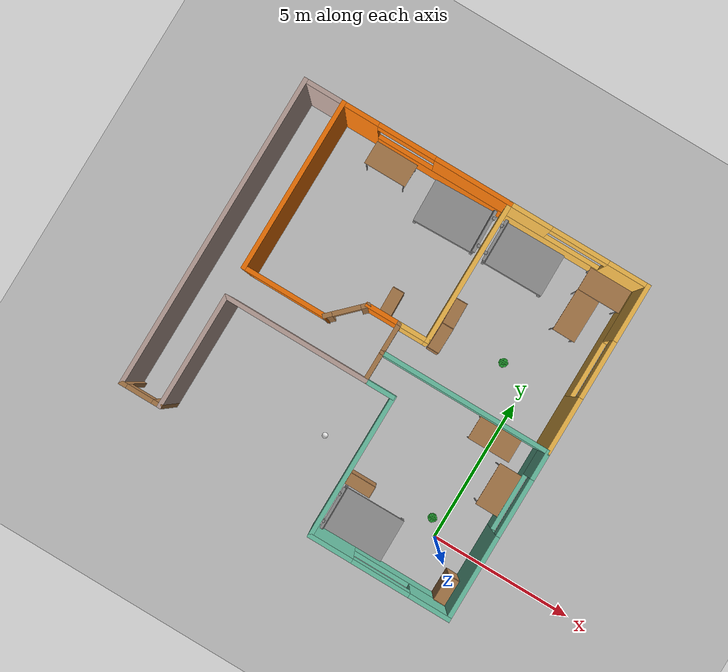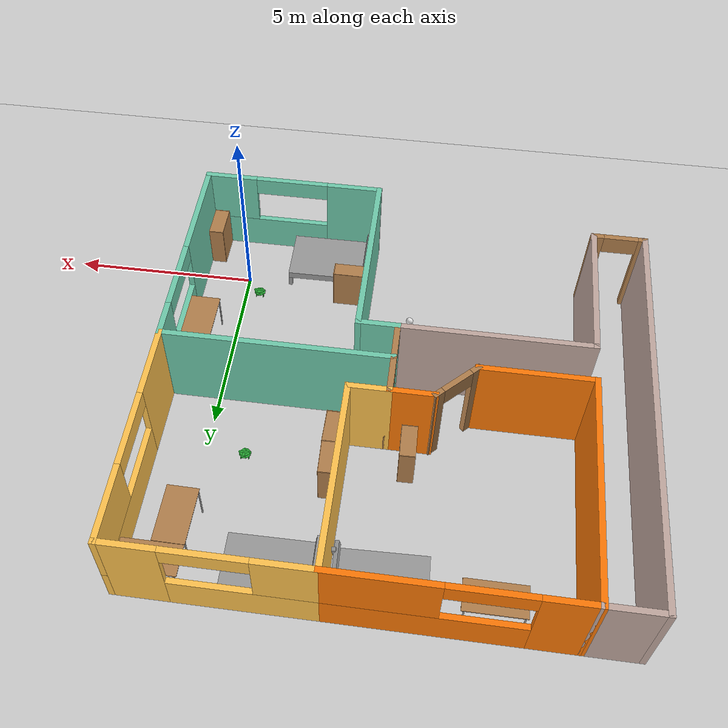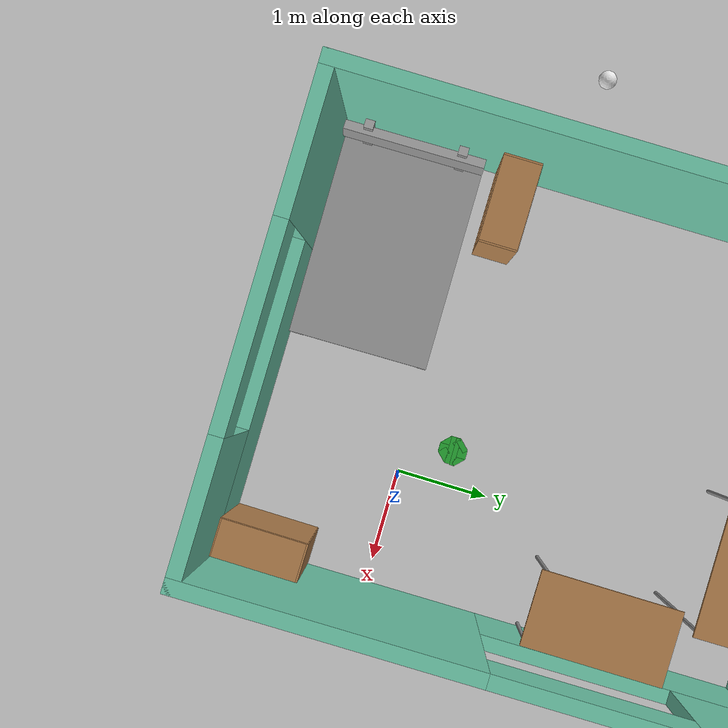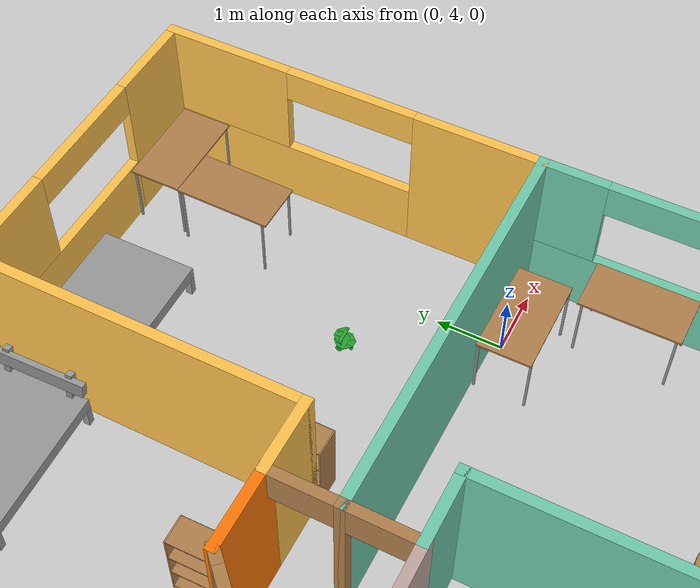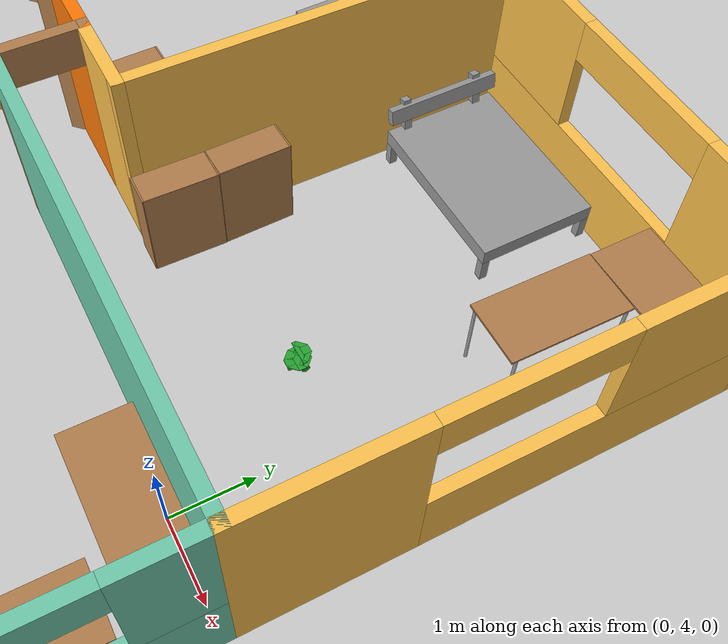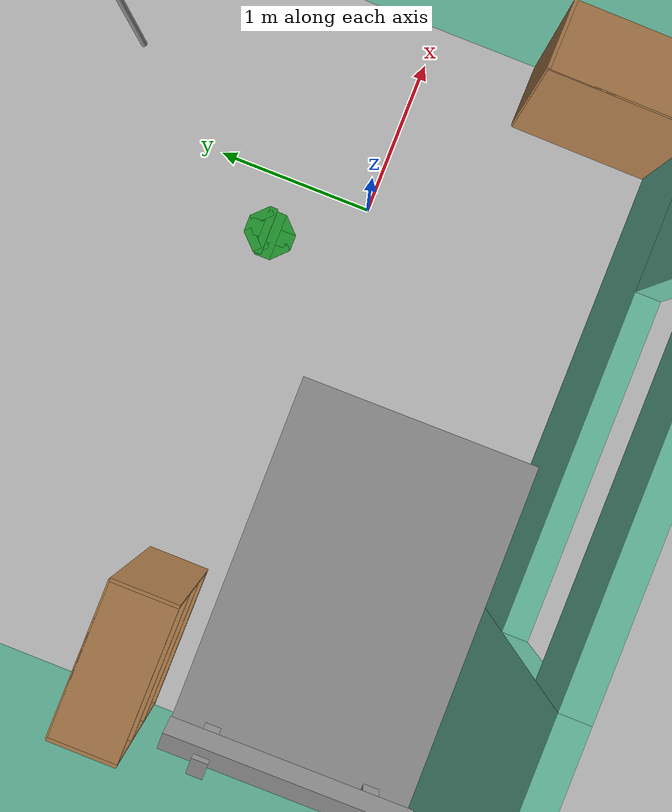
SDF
<sdf version="1.6">
 <world name="default">
  <plugin name="HelloWorld" filename="libhelloWorld.so"/>
  <light name="sun" type="directional">
   <pose>0 0 10 0 -0 0</pose>
   <diffuse>0.8 0.8 0.8 1</diffuse>
   <specular>0.2 0.2 0.2 1</specular>
   <attenuation>
    <range>1000</range>
    <constant>0.9</constant>
    <linear>0.01</linear>
    <quadratic>0.001</quadratic>
   </attenuation>
   <direction>-0.5 0.1 -0.9</direction>
  </light>
  <model name="ground_plane">
   <static>1</static>
   <link name="link">
    <collision name="collision">
     <geometry><plane><normal>0 0 1</normal><size>100 100</size></plane></geometry>
     <surface><friction><ode><mu>100</mu><mu2>50</mu2></ode></friction></surface>
    </collision>
    <visual name="visual">
     <cast_shadows>0</cast_shadows>
     <geometry><plane><normal>0 0 1</normal><size>100 100</size></plane></geometry>
     <material>
      <script><uri>file://media/materials/scripts/gazebo.material</uri><name>Gazebo/Grey</name></script>
     </material>
    </visual>
   </link>
  </model>
  <gravity>0 0 -9.8</gravity>
  <magnetic_field>6e-06 2.3e-05 -4.2e-05</magnetic_field>
  <atmosphere type="adiabatic"/>
  <physics name="default_physics" default="0" type="ode">
   <max_step_size>0.001</max_step_size>
   <real_time_factor>1</real_time_factor>
   <real_time_update_rate>1000</real_time_update_rate>
  </physics>
  <scene><ambient>0.4 0.4 0.4 1</ambient><background>0.7 0.7 0.7 1</background><shadows>1</shadows></scene>
  <spherical_coordinates>
   <surface_model>EARTH_WGS84</surface_model>
   <latitude_deg>0</latitude_deg>
   <longitude_deg>0</longitude_deg>
   <elevation>0</elevation>
   <heading_deg>0</heading_deg>
  </spherical_coordinates>
  <model name="Apartment">
   <pose>-4.7201 4.20671 0 0 -0 0</pose>
   <link name="Wall_0">
    <collision name="Wall_0_Collision">
     <geometry><box><size>5.00001 0.15 2.5</size></box></geometry>
     <pose>0 0 1.25 0 -0 0</pose>
    </collision>
    <visual name="Wall_0_Visual">
     <pose>0 0 1.25 0 -0 0</pose>
     <geometry><box><size>5.00001 0.15 2.5</size></box></geometry>
     <material>
      <script><uri>file://media/materials/scripts/gazebo.material</uri><name>Gazebo/Grey</name></script>
      <ambient>0.435294 0.796078 0.67451 1</ambient>
     </material>
     <meta><layer>0</layer></meta>
    </visual>
    <pose>1.2025 -3.42753 0 0 -0 1.5708</pose>
   </link>
   <link name="Wall_12">
    <pose>3.6275 -5.85253 0 0 -0 0</pose>
    <visual name="Wall_12_Visual_0">
     <pose>-1.72856 0 1.25 0 -0 0</pose>
     <geometry><box><size>1.54289 0.15 2.5</size></box></geometry>
     <material>
      <script><uri>file://media/materials/scripts/gazebo.material</uri><name>Gazebo/Grey</name></script>
      <ambient>0.435294 0.796078 0.67451 1</ambient>
     </material>
     <meta><layer>0</layer></meta>
    </visual>
    <collision name="Wall_12_Collision_0">
     <geometry><box><size>1.54289 0.15 2.5</size></box></geometry>
     <pose>-1.72856 0 1.25 0 -0 0</pose>
    </collision>
    <visual name="Wall_12_Visual_1">
     <pose>0.771445 0 0.5 0 -0 0</pose>
     <geometry><box><size>3.45711 0.15 1</size></box></geometry>
     <material>
      <script><uri>file://media/materials/scripts/gazebo.material</uri><name>Gazebo/Grey</name></script>
      <ambient>0.435294 0.796078 0.67451 1</ambient>
     </material>
     <meta><layer>0</layer></meta>
    </visual>
    <collision name="Wall_12_Collision_1">
     <geometry><box><size>3.45711 0.15 1</size></box></geometry>
     <pose>0.771445 0 0.5 0 -0 0</pose>
    </collision>
    <visual name="Wall_12_Visual_2">
     <pose>1.77144 0 1.75 0 -0 0</pose>
     <geometry><box><size>1.45711 0.15 1.5</size></box></geometry>
     <material>
      <script><uri>file://media/materials/scripts/gazebo.material</uri><name>Gazebo/Grey</name></script>
      <ambient>0.435294 0.796078 0.67451 1</ambient>
     </material>
     <meta><layer>0</layer></meta>
    </visual>
    <collision name="Wall_12_Collision_2">
     <geometry><box><size>1.45711 0.15 1.5</size></box></geometry>
     <pose>1.77144 0 1.75 0 -0 0</pose>
    </collision>
    <visual name="Wall_12_Visual_3">
     <pose>0.04289 0 2.25 0 -0 0</pose>
     <geometry><box><size>2 0.15 0.5</size></box></geometry>
     <material>
      <script><uri>file://media/materials/scripts/gazebo.material</uri><name>Gazebo/Grey</name></script>
      <ambient>0.435294 0.796078 0.67451 1</ambient>
     </material>
     <meta><layer>0</layer></meta>
    </visual>
    <collision name="Wall_12_Collision_3">
     <geometry><box><size>2 0.15 0.5</size></box></geometry>
     <pose>0.04289 0 2.25 0 -0 0</pose>
    </collision>
   </link>
   <link name="Wall_13">
    <pose>6.0525 -2.92753 0 0 -0 1.5708</pose>
    <visual name="Wall_13_Visual_0">
     <pose>-1.5166 0 1.25 0 -0 0</pose>
     <geometry><box><size>2.9668 0.15 2.5</size></box></geometry>
     <material>
      <script><uri>file://media/materials/scripts/gazebo.material</uri><name>Gazebo/Grey</name></script>
      <ambient>0.435294 0.796078 0.67451 1</ambient>
     </material>
     <meta><layer>0</layer></meta>
    </visual>
    <collision name="Wall_13_Collision_0">
     <geometry><box><size>2.9668 0.15 2.5</size></box></geometry>
     <pose>-1.5166 0 1.25 0 -0 0</pose>
    </collision>
    <visual name="Wall_13_Visual_1">
     <pose>1.4834 0 0.5 0 -0 0</pose>
     <geometry><box><size>3.0332 0.15 1</size></box></geometry>
     <material>
      <script><uri>file://media/materials/scripts/gazebo.material</uri><name>Gazebo/Grey</name></script>
      <ambient>0.435294 0.796078 0.67451 1</ambient>
     </material>
     <meta><layer>0</layer></meta>
    </visual>
    <collision name="Wall_13_Collision_1">
     <geometry><box><size>3.0332 0.15 1</size></box></geometry>
     <pose>1.4834 0 0.5 0 -0 0</pose>
    </collision>
    <visual name="Wall_13_Visual_2">
     <pose>2.4834 0 1.75 0 -0 0</pose>
     <geometry><box><size>1.0332 0.15 1.5</size></box></geometry>
     <material>
      <script><uri>file://media/materials/scripts/gazebo.material</uri><name>Gazebo/Grey</name></script>
      <ambient>0.435294 0.796078 0.67451 1</ambient>
     </material>
     <meta><layer>0</layer></meta>
    </visual>
    <collision name="Wall_13_Collision_2">
     <geometry><box><size>1.0332 0.15 1.5</size></box></geometry>
     <pose>2.4834 0 1.75 0 -0 0</pose>
    </collision>
    <visual name="Wall_13_Visual_3">
     <pose>0.966804 0 2.25 0 -0 0</pose>
     <geometry><box><size>2 0.15 0.5</size></box></geometry>
     <material>
      <script><uri>file://media/materials/scripts/gazebo.material</uri><name>Gazebo/Grey</name></script>
      <ambient>0.435294 0.796078 0.67451 1</ambient>
     </material>
     <meta><layer>0</layer></meta>
    </visual>
    <collision name="Wall_13_Collision_3">
     <geometry><box><size>2 0.15 0.5</size></box></geometry>
     <pose>0.966804 0 2.25 0 -0 0</pose>
    </collision>
   </link>
   <link name="Wall_14">
    <collision name="Wall_14_Collision">
     <geometry><box><size>6 0.15 2.5</size></box></geometry>
     <pose>0 0 1.25 0 -0 0</pose>
    </collision>
    <visual name="Wall_14_Visual">
     <pose>0 0 1.25 0 -0 0</pose>
     <geometry><box><size>6 0.15 2.5</size></box></geometry>
     <material>
      <script><uri>file://media/materials/scripts/gazebo.material</uri><name>Gazebo/Grey</name></script>
      <ambient>0.435294 0.796078 0.67451 1</ambient>
     </material>
     <meta><layer>0</layer></meta>
    </visual>
    <pose>3.1275 -0.002528 0 0 -0 3.14159</pose>
   </link>
   <link name="Wall_16">
    <collision name="Wall_16_Collision">
     <geometry><box><size>1.15 0.15 2.5</size></box></geometry>
     <pose>0 0 1.25 0 -0 0</pose>
    </collision>
    <visual name="Wall_16_Visual">
     <pose>0 0 1.25 0 -0 0</pose>
     <geometry><box><size>1.15 0.15 2.5</size></box></geometry>
     <material>
      <script><uri>file://media/materials/scripts/gazebo.material</uri><name>Gazebo/Grey</name></script>
      <ambient>0.435294 0.796078 0.67451 1</ambient>
     </material>
     <meta><layer>0</layer></meta>
    </visual>
    <pose>0.702501 -1.00253 0 0 -0 3.14159</pose>
   </link>
   <link name="Wall_18">
    <pose>0.202501 -0.502528 0 0 -0 1.5708</pose>
    <visual name="Wall_18_Visual_0">
     <pose>-0.519208 0 1.25 0 -0 0</pose>
     <geometry><box><size>0.111583 0.15 2.5</size></box></geometry>
     <material>
      <script><uri>file://media/materials/scripts/gazebo.material</uri><name>Gazebo/Wood</name></script>
      <ambient>1 1 1 1</ambient>
     </material>
     <meta><layer>0</layer></meta>
    </visual>
    <collision name="Wall_18_Collision_0">
     <geometry><box><size>0.111583 0.15 2.5</size></box></geometry>
     <pose>-0.519208 0 1.25 0 -0 0</pose>
    </collision>
    <visual name="Wall_18_Visual_1">
     <pose>0.505792 0 1.25 0 -0 0</pose>
     <geometry><box><size>0.138417 0.15 2.5</size></box></geometry>
     <material>
      <script><uri>file://media/materials/scripts/gazebo.material</uri><name>Gazebo/Wood</name></script>
      <ambient>1 1 1 1</ambient>
     </material>
     <meta><layer>0</layer></meta>
    </visual>
    <collision name="Wall_18_Collision_1">
     <geometry><box><size>0.138417 0.15 2.5</size></box></geometry>
     <pose>0.505792 0 1.25 0 -0 0</pose>
    </collision>
    <visual name="Wall_18_Visual_2">
     <pose>-0.013417 0 2.25 0 -0 0</pose>
     <geometry><box><size>0.9 0.15 0.5</size></box></geometry>
     <material>
      <script><uri>file://media/materials/scripts/gazebo.material</uri><name>Gazebo/Wood</name></script>
      <ambient>1 1 1 1</ambient>
     </material>
     <meta><layer>0</layer></meta>
    </visual>
    <collision name="Wall_18_Collision_2">
     <geometry><box><size>0.9 0.15 0.5</size></box></geometry>
     <pose>-0.013417 0 2.25 0 -0 0</pose>
    </collision>
   </link>
   <link name="Wall_21">
    <pose>6.0525 2.92247 0 0 -0 1.5708</pose>
    <visual name="Wall_21_Visual_0">
     <pose>-2.01035 0 1.25 0 -0 0</pose>
     <geometry><box><size>1.9793 0.15 2.5</size></box></geometry>
     <material>
      <script><uri>file://media/materials/scripts/gazebo.material</uri><name>Gazebo/Grey</name></script>
      <ambient>1 0.764706 0.305882 1</ambient>
     </material>
     <meta><layer>0</layer></meta>
    </visual>
    <collision name="Wall_21_Collision_0">
     <geometry><box><size>1.9793 0.15 2.5</size></box></geometry>
     <pose>-2.01035 0 1.25 0 -0 0</pose>
    </collision>
    <visual name="Wall_21_Visual_1">
     <pose>0.989651 0 0.5 0 -0 0</pose>
     <geometry><box><size>4.0207 0.15 1</size></box></geometry>
     <material>
      <script><uri>file://media/materials/scripts/gazebo.material</uri><name>Gazebo/Grey</name></script>
      <ambient>1 0.764706 0.305882 1</ambient>
     </material>
     <meta><layer>0</layer></meta>
    </visual>
    <collision name="Wall_21_Collision_1">
     <geometry><box><size>4.0207 0.15 1</size></box></geometry>
     <pose>0.989651 0 0.5 0 -0 0</pose>
    </collision>
    <visual name="Wall_21_Visual_2">
     <pose>1.98965 0 1.75 0 -0 0</pose>
     <geometry><box><size>2.0207 0.15 1.5</size></box></geometry>
     <material>
      <script><uri>file://media/materials/scripts/gazebo.material</uri><name>Gazebo/Grey</name></script>
      <ambient>1 0.764706 0.305882 1</ambient>
     </material>
     <meta><layer>0</layer></meta>
    </visual>
    <collision name="Wall_21_Collision_2">
     <geometry><box><size>2.0207 0.15 1.5</size></box></geometry>
     <pose>1.98965 0 1.75 0 -0 0</pose>
    </collision>
    <visual name="Wall_21_Visual_3">
     <pose>-0.020698 0 2.25 0 -0 0</pose>
     <geometry><box><size>2 0.15 0.5</size></box></geometry>
     <material>
      <script><uri>file://media/materials/scripts/gazebo.material</uri><name>Gazebo/Grey</name></script>
      <ambient>1 0.764706 0.305882 1</ambient>
     </material>
     <meta><layer>0</layer></meta>
    </visual>
    <collision name="Wall_21_Collision_3">
     <geometry><box><size>2 0.15 0.5</size></box></geometry>
     <pose>-0.020698 0 2.25 0 -0 0</pose>
    </collision>
   </link>
   <link name="Wall_23">
    <pose>3.6275 5.84747 0 0 -0 3.14159</pose>
    <visual name="Wall_23_Visual_0">
     <pose>-1.7709 0 1.25 0 -0 0</pose>
     <geometry><box><size>1.45819 0.15 2.5</size></box></geometry>
     <material>
      <script><uri>file://media/materials/scripts/gazebo.material</uri><name>Gazebo/Grey</name></script>
      <ambient>1 0.764706 0.305882 1</ambient>
     </material>
     <meta><layer>0</layer></meta>
    </visual>
    <collision name="Wall_23_Collision_0">
     <geometry><box><size>1.45819 0.15 2.5</size></box></geometry>
     <pose>-1.7709 0 1.25 0 -0 0</pose>
    </collision>
    <visual name="Wall_23_Visual_1">
     <pose>0.729095 0 0.5 0 -0 0</pose>
     <geometry><box><size>3.54181 0.15 1</size></box></geometry>
     <material>
      <script><uri>file://media/materials/scripts/gazebo.material</uri><name>Gazebo/Grey</name></script>
      <ambient>1 0.764706 0.305882 1</ambient>
     </material>
     <meta><layer>0</layer></meta>
    </visual>
    <collision name="Wall_23_Collision_1">
     <geometry><box><size>3.54181 0.15 1</size></box></geometry>
     <pose>0.729095 0 0.5 0 -0 0</pose>
    </collision>
    <visual name="Wall_23_Visual_2">
     <pose>1.7291 0 1.75 0 -0 0</pose>
     <geometry><box><size>1.54181 0.15 1.5</size></box></geometry>
     <material>
      <script><uri>file://media/materials/scripts/gazebo.material</uri><name>Gazebo/Grey</name></script>
      <ambient>1 0.764706 0.305882 1</ambient>
     </material>
     <meta><layer>0</layer></meta>
    </visual>
    <collision name="Wall_23_Collision_2">
     <geometry><box><size>1.54181 0.15 1.5</size></box></geometry>
     <pose>1.7291 0 1.75 0 -0 0</pose>
    </collision>
    <visual name="Wall_23_Visual_3">
     <pose>-0.041811 0 2.25 0 -0 0</pose>
     <geometry><box><size>2 0.15 0.5</size></box></geometry>
     <material>
      <script><uri>file://media/materials/scripts/gazebo.material</uri><name>Gazebo/Grey</name></script>
      <ambient>1 0.764706 0.305882 1</ambient>
     </material>
     <meta><layer>0</layer></meta>
    </visual>
    <collision name="Wall_23_Collision_3">
     <geometry><box><size>2 0.15 0.5</size></box></geometry>
     <pose>-0.041811 0 2.25 0 -0 0</pose>
    </collision>
   </link>
   <link name="Wall_24">
    <collision name="Wall_24_Collision">
     <geometry><box><size>5 0.15 2.5</size></box></geometry>
     <pose>0 0 1.25 0 -0 0</pose>
    </collision>
    <visual name="Wall_24_Visual">
     <pose>0 0 1.25 0 -0 0</pose>
     <geometry><box><size>5 0.15 2.5</size></box></geometry>
     <material>
      <script><uri>file://media/materials/scripts/gazebo.material</uri><name>Gazebo/Grey</name></script>
      <ambient>1 0.764706 0.305882 1</ambient>
     </material>
     <meta><layer>0</layer></meta>
    </visual>
    <pose>1.2025 3.42247 0 0 0 -1.5708</pose>
   </link>
   <link name="Wall_25">
    <collision name="Wall_25_Collision">
     <geometry><box><size>1.15 0.15 2.5</size></box></geometry>
     <pose>0 0 1.25 0 -0 0</pose>
    </collision>
    <visual name="Wall_25_Visual">
     <pose>0 0 1.25 0 -0 0</pose>
     <geometry><box><size>1.15 0.15 2.5</size></box></geometry>
     <material>
      <script><uri>file://media/materials/scripts/gazebo.material</uri><name>Gazebo/Grey</name></script>
      <ambient>1 0.764706 0.305882 1</ambient>
     </material>
     <meta><layer>0</layer></meta>
    </visual>
    <pose>0.702501 0.997472 0 0 -0 3.14159</pose>
   </link>
   <link name="Wall_27">
    <pose>0.202501 0.497472 0 0 0 -1.5708</pose>
    <visual name="Wall_27_Visual_0">
     <pose>-0.512016 0 1.25 0 -0 0</pose>
     <geometry><box><size>0.125968 0.15 2.5</size></box></geometry>
     <material>
      <script><uri>file://media/materials/scripts/gazebo.material</uri><name>Gazebo/Wood</name></script>
      <ambient>1 1 1 1</ambient>
     </material>
     <meta><layer>0</layer></meta>
    </visual>
    <collision name="Wall_27_Collision_0">
     <geometry><box><size>0.125968 0.15 2.5</size></box></geometry>
     <pose>-0.512016 0 1.25 0 -0 0</pose>
    </collision>
    <visual name="Wall_27_Visual_1">
     <pose>0.512984 0 1.25 0 -0 0</pose>
     <geometry><box><size>0.124032 0.15 2.5</size></box></geometry>
     <material>
      <script><uri>file://media/materials/scripts/gazebo.material</uri><name>Gazebo/Wood</name></script>
      <ambient>1 1 1 1</ambient>
     </material>
     <meta><layer>0</layer></meta>
    </visual>
    <collision name="Wall_27_Collision_1">
     <geometry><box><size>0.124032 0.15 2.5</size></box></geometry>
     <pose>0.512984 0 1.25 0 -0 0</pose>
    </collision>
    <visual name="Wall_27_Visual_2">
     <pose>0.000968 0 2.25 0 -0 0</pose>
     <geometry><box><size>0.9 0.15 0.5</size></box></geometry>
     <material>
      <script><uri>file://media/materials/scripts/gazebo.material</uri><name>Gazebo/Wood</name></script>
      <ambient>1 1 1 1</ambient>
     </material>
     <meta><layer>0</layer></meta>
    </visual>
    <collision name="Wall_27_Collision_2">
     <geometry><box><size>0.9 0.15 0.5</size></box></geometry>
     <pose>0.000968 0 2.25 0 -0 0</pose>
    </collision>
   </link>
   <link name="Wall_40">
    <collision name="Wall_40_Collision">
     <geometry><box><size>1.25 0.15 2.5</size></box></geometry>
     <pose>0 0 1.25 0 -0 0</pose>
    </collision>
    <visual name="Wall_40_Visual">
     <pose>0 0 1.25 0 -0 0</pose>
     <geometry><box><size>1.25 0.15 2.5</size></box></geometry>
     <material>
      <script><uri>file://media/materials/scripts/gazebo.material</uri><name>Gazebo/Grey</name></script>
      <ambient>0.996078 0.47451 0.0196078 1</ambient>
     </material>
     <meta><layer>0</layer></meta>
    </visual>
    <pose>-0.3475 0.997472 0 0 -0 3.14159</pose>
   </link>
   <link name="Wall_41">
    <pose>-1.3748 0.520175 0 0 0 -2.35619</pose>
    <visual name="Wall_41_Visual_0">
     <pose>-0.599458 0 1.25 0 -0 0</pose>
     <geometry><box><size>0.301084 0.15 2.5</size></box></geometry>
     <material>
      <script><uri>file://media/materials/scripts/gazebo.material</uri><name>Gazebo/Wood</name></script>
      <ambient>1 1 1 1</ambient>
     </material>
     <meta><layer>0</layer></meta>
    </visual>
    <collision name="Wall_41_Collision_0">
     <geometry><box><size>0.301084 0.15 2.5</size></box></geometry>
     <pose>-0.599458 0 1.25 0 -0 0</pose>
    </collision>
    <visual name="Wall_41_Visual_1">
     <pose>0.600542 0 1.25 0 -0 0</pose>
     <geometry><box><size>0.298916 0.15 2.5</size></box></geometry>
     <material>
      <script><uri>file://media/materials/scripts/gazebo.material</uri><name>Gazebo/Wood</name></script>
      <ambient>1 1 1 1</ambient>
     </material>
     <meta><layer>0</layer></meta>
    </visual>
    <collision name="Wall_41_Collision_1">
     <geometry><box><size>0.298916 0.15 2.5</size></box></geometry>
     <pose>0.600542 0 1.25 0 -0 0</pose>
    </collision>
    <visual name="Wall_41_Visual_2">
     <pose>0.001084 0 2.25 0 -0 0</pose>
     <geometry><box><size>0.9 0.15 0.5</size></box></geometry>
     <material>
      <script><uri>file://media/materials/scripts/gazebo.material</uri><name>Gazebo/Wood</name></script>
      <ambient>1 1 1 1</ambient>
     </material>
     <meta><layer>0</layer></meta>
    </visual>
    <collision name="Wall_41_Collision_2">
     <geometry><box><size>0.9 0.15 0.5</size></box></geometry>
     <pose>0.001084 0 2.25 0 -0 0</pose>
    </collision>
   </link>
   <link name="Wall_42">
    <collision name="Wall_42_Collision">
     <geometry><box><size>3 0.15 2.5</size></box></geometry>
     <pose>0 0 1.25 0 -0 0</pose>
    </collision>
    <visual name="Wall_42_Visual">
     <pose>0 0 1.25 0 -0 0</pose>
     <geometry><box><size>3 0.15 2.5</size></box></geometry>
     <material>
      <script><uri>file://media/materials/scripts/gazebo.material</uri><name>Gazebo/Grey</name></script>
      <ambient>0.996078 0.47451 0.0196078 1</ambient>
     </material>
     <meta><layer>0</layer></meta>
    </visual>
    <pose>-3.2773 0.042675 0 0 0 -3.14145</pose>
   </link>
   <link name="Wall_44">
    <collision name="Wall_44_Collision">
     <geometry><box><size>5.96 0.15 2.5</size></box></geometry>
     <pose>0 0 1.25 0 -0 0</pose>
    </collision>
    <visual name="Wall_44_Visual">
     <pose>0 0 1.25 0 -0 0</pose>
     <geometry><box><size>5.96 0.15 2.5</size></box></geometry>
     <material>
      <script><uri>file://media/materials/scripts/gazebo.material</uri><name>Gazebo/Grey</name></script>
      <ambient>0.996078 0.47451 0.0196078 1</ambient>
     </material>
     <meta><layer>0</layer></meta>
    </visual>
    <pose>-4.7025 2.94747 0 0 -0 1.5708</pose>
   </link>
   <link name="Wall_46">
    <pose>-1.75 5.84997 0 0 0 -0.000847</pose>
    <visual name="Wall_46_Visual_0">
     <pose>-2.36135 0 1.25 0 -0 0</pose>
     <geometry><box><size>1.33231 0.15 2.5</size></box></geometry>
     <material>
      <script><uri>file://media/materials/scripts/gazebo.material</uri><name>Gazebo/Grey</name></script>
      <ambient>0.996078 0.47451 0.0196078 1</ambient>
     </material>
     <meta><layer>0</layer></meta>
    </visual>
    <collision name="Wall_46_Collision_0">
     <geometry><box><size>1.33231 0.15 2.5</size></box></geometry>
     <pose>-2.36135 0 1.25 0 -0 0</pose>
    </collision>
    <visual name="Wall_46_Visual_1">
     <pose>0.666153 0 0.5 0 -0 0</pose>
     <geometry><box><size>4.7227 0.15 1</size></box></geometry>
     <material>
      <script><uri>file://media/materials/scripts/gazebo.material</uri><name>Gazebo/Grey</name></script>
      <ambient>0.996078 0.47451 0.0196078 1</ambient>
     </material>
     <meta><layer>0</layer></meta>
    </visual>
    <collision name="Wall_46_Collision_1">
     <geometry><box><size>4.7227 0.15 1</size></box></geometry>
     <pose>0.666153 0 0.5 0 -0 0</pose>
    </collision>
    <visual name="Wall_46_Visual_2">
     <pose>1.66615 0 1.75 0 -0 0</pose>
     <geometry><box><size>2.7227 0.15 1.5</size></box></geometry>
     <material>
      <script><uri>file://media/materials/scripts/gazebo.material</uri><name>Gazebo/Grey</name></script>
      <ambient>0.996078 0.47451 0.0196078 1</ambient>
     </material>
     <meta><layer>0</layer></meta>
    </visual>
    <collision name="Wall_46_Collision_2">
     <geometry><box><size>2.7227 0.15 1.5</size></box></geometry>
     <pose>1.66615 0 1.75 0 -0 0</pose>
    </collision>
    <visual name="Wall_46_Visual_3">
     <pose>-0.695195 0 2.25 0 -0 0</pose>
     <geometry><box><size>2 0.15 0.5</size></box></geometry>
     <material>
      <script><uri>file://media/materials/scripts/gazebo.material</uri><name>Gazebo/Grey</name></script>
      <ambient>0.996078 0.47451 0.0196078 1</ambient>
     </material>
     <meta><layer>0</layer></meta>
    </visual>
    <collision name="Wall_46_Collision_3">
     <geometry><box><size>2 0.15 0.5</size></box></geometry>
     <pose>-0.695195 0 2.25 0 -0 0</pose>
    </collision>
   </link>
   <link name="Wall_48">
    <collision name="Wall_48_Collision">
     <geometry><box><size>5.055 0.15 2.5</size></box></geometry>
     <pose>0 0 1.25 0 -0 0</pose>
    </collision>
    <visual name="Wall_48_Visual">
     <pose>0 0 1.25 0 -0 0</pose>
     <geometry><box><size>5.055 0.15 2.5</size></box></geometry>
     <material>
      <script><uri>file://media/materials/scripts/gazebo.material</uri><name>Gazebo/Grey</name></script>
      <ambient>0.760784 0.662745 0.627451 1</ambient>
     </material>
     <meta><layer>0</layer></meta>
    </visual>
    <pose>-2.25 -1.00253 0 0 -0 3.14159</pose>
   </link>
   <link name="Wall_50">
    <collision name="Wall_50_Collision">
     <geometry><box><size>4 0.15 2.5</size></box></geometry>
     <pose>0 0 1.25 0 -0 0</pose>
    </collision>
    <visual name="Wall_50_Visual">
     <pose>0 0 1.25 0 -0 0</pose>
     <geometry><box><size>4 0.15 2.5</size></box></geometry>
     <material>
      <script><uri>file://media/materials/scripts/gazebo.material</uri><name>Gazebo/Grey</name></script>
      <ambient>0.760784 0.662745 0.627451 1</ambient>
     </material>
     <meta><layer>0</layer></meta>
    </visual>
    <pose>-4.7025 -2.92753 0 0 0 -1.5708</pose>
   </link>
   <link name="Wall_52">
    <pose>-5.3775 -4.85253 0 0 -0 3.14159</pose>
    <visual name="Wall_52_Visual_0">
     <pose>-0.579208 0 1.25 0 -0 0</pose>
     <geometry><box><size>0.341584 0.15 2.5</size></box></geometry>
     <material>
      <script><uri>file://media/materials/scripts/gazebo.material</uri><name>Gazebo/Wood</name></script>
      <ambient>1 1 1 1</ambient>
     </material>
     <meta><layer>0</layer></meta>
    </visual>
    <collision name="Wall_52_Collision_0">
     <geometry><box><size>0.341584 0.15 2.5</size></box></geometry>
     <pose>-0.579208 0 1.25 0 -0 0</pose>
    </collision>
    <visual name="Wall_52_Visual_1">
     <pose>0.620792 0 1.25 0 -0 0</pose>
     <geometry><box><size>0.258416 0.15 2.5</size></box></geometry>
     <material>
      <script><uri>file://media/materials/scripts/gazebo.material</uri><name>Gazebo/Wood</name></script>
      <ambient>1 1 1 1</ambient>
     </material>
     <meta><layer>0</layer></meta>
    </visual>
    <collision name="Wall_52_Collision_1">
     <geometry><box><size>0.258416 0.15 2.5</size></box></geometry>
     <pose>0.620792 0 1.25 0 -0 0</pose>
    </collision>
    <visual name="Wall_52_Visual_2">
     <pose>0.041584 0 2.25 0 -0 0</pose>
     <geometry><box><size>0.9 0.15 0.5</size></box></geometry>
     <material>
      <script><uri>file://media/materials/scripts/gazebo.material</uri><name>Gazebo/Wood</name></script>
      <ambient>1 1 1 1</ambient>
     </material>
     <meta><layer>0</layer></meta>
    </visual>
    <collision name="Wall_52_Collision_2">
     <geometry><box><size>0.9 0.15 0.5</size></box></geometry>
     <pose>0.041584 0 2.25 0 -0 0</pose>
    </collision>
   </link>
   <link name="Wall_54">
    <collision name="Wall_54_Collision">
     <geometry><box><size>10.855 0.15 2.5</size></box></geometry>
     <pose>0 0 1.25 0 -0 0</pose>
    </collision>
    <visual name="Wall_54_Visual">
     <pose>0 0 1.25 0 -0 0</pose>
     <geometry><box><size>10.855 0.15 2.5</size></box></geometry>
     <material>
      <script><uri>file://media/materials/scripts/gazebo.material</uri><name>Gazebo/Grey</name></script>
      <ambient>0.760784 0.662745 0.627451 1</ambient>
     </material>
     <meta><layer>0</layer></meta>
    </visual>
    <pose>-6.0525 0.499972 0 0 -0 1.5708</pose>
   </link>
   <link name="Wall_56">
    <collision name="Wall_56_Collision">
     <geometry><box><size>1.5 0.15 2.5</size></box></geometry>
     <pose>0 0 1.25 0 -0 0</pose>
    </collision>
    <visual name="Wall_56_Visual">
     <pose>0 0 1.25 0 -0 0</pose>
     <geometry><box><size>1.5 0.15 2.5</size></box></geometry>
     <material>
      <script><uri>file://media/materials/scripts/gazebo.material</uri><name>Gazebo/Grey</name></script>
      <ambient>0.760784 0.662745 0.627451 1</ambient>
     </material>
     <meta><layer>0</layer></meta>
    </visual>
    <pose>-5.3775 5.85247 0 0 -0 0</pose>
   </link>
   <static>1</static>
  </model>
  <model name="table">
   <static>1</static>
   <link name="link">
    <collision name="surface">
     <pose>0 0 1 0 -0 0</pose>
     <geometry><box><size>1.5 0.8 0.03</size></box></geometry>
     <surface><friction><ode><mu>0.6</mu><mu2>0.6</mu2></ode></friction></surface>
    </collision>
    <visual name="visual1">
     <pose>0 0 1 0 -0 0</pose>
     <geometry><box><size>1.5 0.8 0.03</size></box></geometry>
     <material>
      <script><uri>file://media/materials/scripts/gazebo.material</uri><name>Gazebo/Wood</name></script>
     </material>
    </visual>
    <collision name="front_left_leg">
     <pose>0.68 0.38 0.5 0 -0 0</pose>
     <geometry><cylinder><radius>0.02</radius><length>1</length></cylinder></geometry>
    </collision>
    <visual name="front_left_leg">
     <pose>0.68 0.38 0.5 0 -0 0</pose>
     <geometry><cylinder><radius>0.02</radius><length>1</length></cylinder></geometry>
     <material>
      <script><uri>file://media/materials/scripts/gazebo.material</uri><name>Gazebo/Grey</name></script>
     </material>
    </visual>
    <collision name="front_right_leg">
     <pose>0.68 -0.38 0.5 0 -0 0</pose>
     <geometry><cylinder><radius>0.02</radius><length>1</length></cylinder></geometry>
    </collision>
    <visual name="front_right_leg">
     <pose>0.68 -0.38 0.5 0 -0 0</pose>
     <geometry><cylinder><radius>0.02</radius><length>1</length></cylinder></geometry>
     <material>
      <script><uri>file://media/materials/scripts/gazebo.material</uri><name>Gazebo/Grey</name></script>
     </material>
    </visual>
    <collision name="back_right_leg">
     <pose>-0.68 -0.38 0.5 0 -0 0</pose>
     <geometry><cylinder><radius>0.02</radius><length>1</length></cylinder></geometry>
    </collision>
    <visual name="back_right_leg">
     <pose>-0.68 -0.38 0.5 0 -0 0</pose>
     <geometry><cylinder><radius>0.02</radius><length>1</length></cylinder></geometry>
     <material>
      <script><uri>file://media/materials/scripts/gazebo.material</uri><name>Gazebo/Grey</name></script>
     </material>
    </visual>
    <collision name="back_left_leg">
     <pose>-0.68 0.38 0.5 0 -0 0</pose>
     <geometry><cylinder><radius>0.02</radius><length>1</length></cylinder></geometry>
    </collision>
    <visual name="back_left_leg">
     <pose>-0.68 0.38 0.5 0 -0 0</pose>
     <geometry><cylinder><radius>0.02</radius><length>1</length></cylinder></geometry>
     <material>
      <script><uri>file://media/materials/scripts/gazebo.material</uri><name>Gazebo/Grey</name></script>
     </material>
    </visual>
   </link>
   <pose>-0.073293 3.71313 0 0 -0 0</pose>
  </model>
  <model name="table_clone">
   <static>1</static>
   <link name="link">
    <collision name="surface">
     <pose>0 0 1 0 -0 0</pose>
     <geometry><box><size>1.5 0.8 0.03</size></box></geometry>
     <surface><friction><ode><mu>0.6</mu><mu2>0.6</mu2></ode></friction></surface>
    </collision>
    <visual name="visual1">
     <pose>0 0 1 0 -0 0</pose>
     <geometry><box><size>1.5 0.8 0.03</size></box></geometry>
     <material>
      <script><uri>file://media/materials/scripts/gazebo.material</uri><name>Gazebo/Wood</name></script>
     </material>
    </visual>
    <collision name="front_left_leg">
     <pose>0.68 0.38 0.5 0 -0 0</pose>
     <geometry><cylinder><radius>0.02</radius><length>1</length></cylinder></geometry>
    </collision>
    <visual name="front_left_leg">
     <pose>0.68 0.38 0.5 0 -0 0</pose>
     <geometry><cylinder><radius>0.02</radius><length>1</length></cylinder></geometry>
     <material>
      <script><uri>file://media/materials/scripts/gazebo.material</uri><name>Gazebo/Grey</name></script>
     </material>
    </visual>
    <collision name="front_right_leg">
     <pose>0.68 -0.38 0.5 0 -0 0</pose>
     <geometry><cylinder><radius>0.02</radius><length>1</length></cylinder></geometry>
    </collision>
    <visual name="front_right_leg">
     <pose>0.68 -0.38 0.5 0 -0 0</pose>
     <geometry><cylinder><radius>0.02</radius><length>1</length></cylinder></geometry>
     <material>
      <script><uri>file://media/materials/scripts/gazebo.material</uri><name>Gazebo/Grey</name></script>
     </material>
    </visual>
    <collision name="back_right_leg">
     <pose>-0.68 -0.38 0.5 0 -0 0</pose>
     <geometry><cylinder><radius>0.02</radius><length>1</length></cylinder></geometry>
    </collision>
    <visual name="back_right_leg">
     <pose>-0.68 -0.38 0.5 0 -0 0</pose>
     <geometry><cylinder><radius>0.02</radius><length>1</length></cylinder></geometry>
     <material>
      <script><uri>file://media/materials/scripts/gazebo.material</uri><name>Gazebo/Grey</name></script>
     </material>
    </visual>
    <collision name="back_left_leg">
     <pose>-0.68 0.38 0.5 0 -0 0</pose>
     <geometry><cylinder><radius>0.02</radius><length>1</length></cylinder></geometry>
    </collision>
    <visual name="back_left_leg">
     <pose>-0.68 0.38 0.5 0 -0 0</pose>
     <geometry><cylinder><radius>0.02</radius><length>1</length></cylinder></geometry>
     <material>
      <script><uri>file://media/materials/scripts/gazebo.material</uri><name>Gazebo/Grey</name></script>
     </material>
    </visual>
   </link>
   <pose>0.109174 8.39051 0 0 -0 1.55851</pose>
  </model>
  <model name="table_clone_0">
   <static>1</static>
   <link name="link">
    <collision name="surface">
     <pose>0 0 1 0 -0 0</pose>
     <geometry><box><size>1.5 0.8 0.03</size></box></geometry>
     <surface><friction><ode><mu>0.6</mu><mu2>0.6</mu2></ode></friction></surface>
    </collision>
    <visual name="visual1">
     <pose>0 0 1 0 -0 0</pose>
     <geometry><box><size>1.5 0.8 0.03</size></box></geometry>
     <material>
      <script><uri>file://media/materials/scripts/gazebo.material</uri><name>Gazebo/Wood</name></script>
     </material>
    </visual>
    <collision name="front_left_leg">
     <pose>0.68 0.38 0.5 0 -0 0</pose>
     <geometry><cylinder><radius>0.02</radius><length>1</length></cylinder></geometry>
    </collision>
    <visual name="front_left_leg">
     <pose>0.68 0.38 0.5 0 -0 0</pose>
     <geometry><cylinder><radius>0.02</radius><length>1</length></cylinder></geometry>
     <material>
      <script><uri>file://media/materials/scripts/gazebo.material</uri><name>Gazebo/Grey</name></script>
     </material>
    </visual>
    <collision name="front_right_leg">
     <pose>0.68 -0.38 0.5 0 -0 0</pose>
     <geometry><cylinder><radius>0.02</radius><length>1</length></cylinder></geometry>
    </collision>
    <visual name="front_right_leg">
     <pose>0.68 -0.38 0.5 0 -0 0</pose>
     <geometry><cylinder><radius>0.02</radius><length>1</length></cylinder></geometry>
     <material>
      <script><uri>file://media/materials/scripts/gazebo.material</uri><name>Gazebo/Grey</name></script>
     </material>
    </visual>
    <collision name="back_right_leg">
     <pose>-0.68 -0.38 0.5 0 -0 0</pose>
     <geometry><cylinder><radius>0.02</radius><length>1</length></cylinder></geometry>
    </collision>
    <visual name="back_right_leg">
     <pose>-0.68 -0.38 0.5 0 -0 0</pose>
     <geometry><cylinder><radius>0.02</radius><length>1</length></cylinder></geometry>
     <material>
      <script><uri>file://media/materials/scripts/gazebo.material</uri><name>Gazebo/Grey</name></script>
     </material>
    </visual>
    <collision name="back_left_leg">
     <pose>-0.68 0.38 0.5 0 -0 0</pose>
     <geometry><cylinder><radius>0.02</radius><length>1</length></cylinder></geometry>
    </collision>
    <visual name="back_left_leg">
     <pose>-0.68 0.38 0.5 0 -0 0</pose>
     <geometry><cylinder><radius>0.02</radius><length>1</length></cylinder></geometry>
     <material>
      <script><uri>file://media/materials/scripts/gazebo.material</uri><name>Gazebo/Grey</name></script>
     </material>
    </visual>
   </link>
   <pose>0.477957 9.54981 0 0 -0 0</pose>
  </model>
  <model name="table_clone_1">
   <static>1</static>
   <link name="link">
    <collision name="surface">
     <pose>0 0 1 0 -0 0</pose>
     <geometry><box><size>1.5 0.8 0.03</size></box></geometry>
     <surface><friction><ode><mu>0.6</mu><mu2>0.6</mu2></ode></friction></surface>
    </collision>
    <visual name="visual1">
     <pose>0 0 1 0 -0 0</pose>
     <geometry><box><size>1.5 0.8 0.03</size></box></geometry>
     <material>
      <script><uri>file://media/materials/scripts/gazebo.material</uri><name>Gazebo/Wood</name></script>
     </material>
    </visual>
    <collision name="front_left_leg">
     <pose>0.68 0.38 0.5 0 -0 0</pose>
     <geometry><cylinder><radius>0.02</radius><length>1</length></cylinder></geometry>
    </collision>
    <visual name="front_left_leg">
     <pose>0.68 0.38 0.5 0 -0 0</pose>
     <geometry><cylinder><radius>0.02</radius><length>1</length></cylinder></geometry>
     <material>
      <script><uri>file://media/materials/scripts/gazebo.material</uri><name>Gazebo/Grey</name></script>
     </material>
    </visual>
    <collision name="front_right_leg">
     <pose>0.68 -0.38 0.5 0 -0 0</pose>
     <geometry><cylinder><radius>0.02</radius><length>1</length></cylinder></geometry>
    </collision>
    <visual name="front_right_leg">
     <pose>0.68 -0.38 0.5 0 -0 0</pose>
     <geometry><cylinder><radius>0.02</radius><length>1</length></cylinder></geometry>
     <material>
      <script><uri>file://media/materials/scripts/gazebo.material</uri><name>Gazebo/Grey</name></script>
     </material>
    </visual>
    <collision name="back_right_leg">
     <pose>-0.68 -0.38 0.5 0 -0 0</pose>
     <geometry><cylinder><radius>0.02</radius><length>1</length></cylinder></geometry>
    </collision>
    <visual name="back_right_leg">
     <pose>-0.68 -0.38 0.5 0 -0 0</pose>
     <geometry><cylinder><radius>0.02</radius><length>1</length></cylinder></geometry>
     <material>
      <script><uri>file://media/materials/scripts/gazebo.material</uri><name>Gazebo/Grey</name></script>
     </material>
    </visual>
    <collision name="back_left_leg">
     <pose>-0.68 0.38 0.5 0 -0 0</pose>
     <geometry><cylinder><radius>0.02</radius><length>1</length></cylinder></geometry>
    </collision>
    <visual name="back_left_leg">
     <pose>-0.68 0.38 0.5 0 -0 0</pose>
     <geometry><cylinder><radius>0.02</radius><length>1</length></cylinder></geometry>
     <material>
      <script><uri>file://media/materials/scripts/gazebo.material</uri><name>Gazebo/Grey</name></script>
     </material>
    </visual>
   </link>
   <pose>-7.38271 9.48873 0 0 -0 0</pose>
  </model>
  <model name="bookshelf">
   <static>1</static>
   <link name="link">
    <inertial><mass>1</mass></inertial>
    <collision name="back">
     <pose>0 0.005 0.6 0 -0 0</pose>
     <geometry><box><size>0.9 0.01 1.2</size></box></geometry>
    </collision>
    <visual name="visual1">
     <pose>0 0.005 0.6 0 -0 0</pose>
     <geometry><box><size>0.9 0.01 1.2</size></box></geometry>
     <material>
      <script><uri>file://media/materials/scripts/gazebo.material</uri><name>Gazebo/Wood</name></script>
     </material>
    </visual>
    <collision name="left_side">
     <pose>0.45 -0.195 0.6 0 -0 0</pose>
     <geometry><box><size>0.02 0.4 1.2</size></box></geometry>
    </collision>
    <visual name="visual2">
     <pose>0.45 -0.195 0.6 0 -0 0</pose>
     <geometry><box><size>0.02 0.4 1.2</size></box></geometry>
     <material>
      <script><uri>file://media/materials/scripts/gazebo.material</uri><name>Gazebo/Wood</name></script>
     </material>
    </visual>
    <collision name="right_side">
     <pose>-0.45 -0.195 0.6 0 -0 0</pose>
     <geometry><box><size>0.02 0.4 1.2</size></box></geometry>
    </collision>
    <visual name="visual3">
     <pose>-0.45 -0.195 0.6 0 -0 0</pose>
     <geometry><box><size>0.02 0.4 1.2</size></box></geometry>
     <material>
      <script><uri>file://media/materials/scripts/gazebo.material</uri><name>Gazebo/Wood</name></script>
     </material>
    </visual>
    <collision name="bottom">
     <pose>0 -0.195 0.03 0 -0 0</pose>
     <geometry><box><size>0.88 0.4 0.06</size></box></geometry>
    </collision>
    <visual name="visual4">
     <pose>0 -0.195 0.03 0 -0 0</pose>
     <geometry><box><size>0.88 0.4 0.06</size></box></geometry>
     <material>
      <script><uri>file://media/materials/scripts/gazebo.material</uri><name>Gazebo/Wood</name></script>
     </material>
    </visual>
    <collision name="top">
     <pose>0 -0.195 1.19 0 -0 0</pose>
     <geometry><box><size>0.88 0.4 0.02</size></box></geometry>
    </collision>
    <visual name="visual5">
     <pose>0 -0.195 1.19 0 -0 0</pose>
     <geometry><box><size>0.88 0.4 0.02</size></box></geometry>
     <material>
      <script><uri>file://media/materials/scripts/gazebo.material</uri><name>Gazebo/Wood</name></script>
     </material>
    </visual>
    <collision name="low_shelf">
     <pose>0 -0.195 0.43 0 -0 0</pose>
     <geometry><box><size>0.88 0.4 0.02</size></box></geometry>
    </collision>
    <visual name="visual6">
     <pose>0 -0.195 0.43 0 -0 0</pose>
     <geometry><box><size>0.88 0.4 0.02</size></box></geometry>
     <material>
      <script><uri>file://media/materials/scripts/gazebo.material</uri><name>Gazebo/Wood</name></script>
     </material>
    </visual>
    <collision name="high_shelf">
     <pose>0 -0.195 0.8 0 -0 0</pose>
     <geometry><box><size>0.88 0.4 0.02</size></box></geometry>
    </collision>
    <visual name="visual7">
     <pose>0 -0.195 0.8 0 -0 0</pose>
     <geometry><box><size>0.88 0.4 0.02</size></box></geometry>
     <material>
      <script><uri>file://media/materials/scripts/gazebo.material</uri><name>Gazebo/Wood</name></script>
     </material>
    </visual>
   </link>
   <pose>-2.97492 0.495259 0 0 -0 0</pose>
  </model>
  <model name="bookshelf_clone">
   <static>1</static>
   <link name="link">
    <inertial><mass>1</mass></inertial>
    <collision name="back">
     <pose>0 0.005 0.6 0 -0 0</pose>
     <geometry><box><size>0.9 0.01 1.2</size></box></geometry>
    </collision>
    <visual name="visual1">
     <pose>0 0.005 0.6 0 -0 0</pose>
     <geometry><box><size>0.9 0.01 1.2</size></box></geometry>
     <material>
      <script><uri>file://media/materials/scripts/gazebo.material</uri><name>Gazebo/Wood</name></script>
     </material>
    </visual>
    <collision name="left_side">
     <pose>0.45 -0.195 0.6 0 -0 0</pose>
     <geometry><box><size>0.02 0.4 1.2</size></box></geometry>
    </collision>
    <visual name="visual2">
     <pose>0.45 -0.195 0.6 0 -0 0</pose>
     <geometry><box><size>0.02 0.4 1.2</size></box></geometry>
     <material>
      <script><uri>file://media/materials/scripts/gazebo.material</uri><name>Gazebo/Wood</name></script>
     </material>
    </visual>
    <collision name="right_side">
     <pose>-0.45 -0.195 0.6 0 -0 0</pose>
     <geometry><box><size>0.02 0.4 1.2</size></box></geometry>
    </collision>
    <visual name="visual3">
     <pose>-0.45 -0.195 0.6 0 -0 0</pose>
     <geometry><box><size>0.02 0.4 1.2</size></box></geometry>
     <material>
      <script><uri>file://media/materials/scripts/gazebo.material</uri><name>Gazebo/Wood</name></script>
     </material>
    </visual>
    <collision name="bottom">
     <pose>0 -0.195 0.03 0 -0 0</pose>
     <geometry><box><size>0.88 0.4 0.06</size></box></geometry>
    </collision>
    <visual name="visual4">
     <pose>0 -0.195 0.03 0 -0 0</pose>
     <geometry><box><size>0.88 0.4 0.06</size></box></geometry>
     <material>
      <script><uri>file://media/materials/scripts/gazebo.material</uri><name>Gazebo/Wood</name></script>
     </material>
    </visual>
    <collision name="top">
     <pose>0 -0.195 1.19 0 -0 0</pose>
     <geometry><box><size>0.88 0.4 0.02</size></box></geometry>
    </collision>
    <visual name="visual5">
     <pose>0 -0.195 1.19 0 -0 0</pose>
     <geometry><box><size>0.88 0.4 0.02</size></box></geometry>
     <material>
      <script><uri>file://media/materials/scripts/gazebo.material</uri><name>Gazebo/Wood</name></script>
     </material>
    </visual>
    <collision name="low_shelf">
     <pose>0 -0.195 0.43 0 -0 0</pose>
     <geometry><box><size>0.88 0.4 0.02</size></box></geometry>
    </collision>
    <visual name="visual6">
     <pose>0 -0.195 0.43 0 -0 0</pose>
     <geometry><box><size>0.88 0.4 0.02</size></box></geometry>
     <material>
      <script><uri>file://media/materials/scripts/gazebo.material</uri><name>Gazebo/Wood</name></script>
     </material>
    </visual>
    <collision name="high_shelf">
     <pose>0 -0.195 0.8 0 -0 0</pose>
     <geometry><box><size>0.88 0.4 0.02</size></box></geometry>
    </collision>
    <visual name="visual7">
     <pose>0 -0.195 0.8 0 -0 0</pose>
     <geometry><box><size>0.88 0.4 0.02</size></box></geometry>
     <material>
      <script><uri>file://media/materials/scripts/gazebo.material</uri><name>Gazebo/Wood</name></script>
     </material>
    </visual>
   </link>
   <pose>-3.00069 5.55513 0 0 0 -1.58308</pose>
  </model>
  <model name="bookshelf_clone_0">
   <static>1</static>
   <link name="link">
    <inertial><mass>1</mass></inertial>
    <collision name="back">
     <pose>0 0.005 0.6 0 -0 0</pose>
     <geometry><box><size>0.9 0.01 1.2</size></box></geometry>
    </collision>
    <visual name="visual1">
     <pose>0 0.005 0.6 0 -0 0</pose>
     <geometry><box><size>0.9 0.01 1.2</size></box></geometry>
     <material>
      <script><uri>file://media/materials/scripts/gazebo.material</uri><name>Gazebo/Wood</name></script>
     </material>
    </visual>
    <collision name="left_side">
     <pose>0.45 -0.195 0.6 0 -0 0</pose>
     <geometry><box><size>0.02 0.4 1.2</size></box></geometry>
    </collision>
    <visual name="visual2">
     <pose>0.45 -0.195 0.6 0 -0 0</pose>
     <geometry><box><size>0.02 0.4 1.2</size></box></geometry>
     <material>
      <script><uri>file://media/materials/scripts/gazebo.material</uri><name>Gazebo/Wood</name></script>
     </material>
    </visual>
    <collision name="right_side">
     <pose>-0.45 -0.195 0.6 0 -0 0</pose>
     <geometry><box><size>0.02 0.4 1.2</size></box></geometry>
    </collision>
    <visual name="visual3">
     <pose>-0.45 -0.195 0.6 0 -0 0</pose>
     <geometry><box><size>0.02 0.4 1.2</size></box></geometry>
     <material>
      <script><uri>file://media/materials/scripts/gazebo.material</uri><name>Gazebo/Wood</name></script>
     </material>
    </visual>
    <collision name="bottom">
     <pose>0 -0.195 0.03 0 -0 0</pose>
     <geometry><box><size>0.88 0.4 0.06</size></box></geometry>
    </collision>
    <visual name="visual4">
     <pose>0 -0.195 0.03 0 -0 0</pose>
     <geometry><box><size>0.88 0.4 0.06</size></box></geometry>
     <material>
      <script><uri>file://media/materials/scripts/gazebo.material</uri><name>Gazebo/Wood</name></script>
     </material>
    </visual>
    <collision name="top">
     <pose>0 -0.195 1.19 0 -0 0</pose>
     <geometry><box><size>0.88 0.4 0.02</size></box></geometry>
    </collision>
    <visual name="visual5">
     <pose>0 -0.195 1.19 0 -0 0</pose>
     <geometry><box><size>0.88 0.4 0.02</size></box></geometry>
     <material>
      <script><uri>file://media/materials/scripts/gazebo.material</uri><name>Gazebo/Wood</name></script>
     </material>
    </visual>
    <collision name="low_shelf">
     <pose>0 -0.195 0.43 0 -0 0</pose>
     <geometry><box><size>0.88 0.4 0.02</size></box></geometry>
    </collision>
    <visual name="visual6">
     <pose>0 -0.195 0.43 0 -0 0</pose>
     <geometry><box><size>0.88 0.4 0.02</size></box></geometry>
     <material>
      <script><uri>file://media/materials/scripts/gazebo.material</uri><name>Gazebo/Wood</name></script>
     </material>
    </visual>
    <collision name="high_shelf">
     <pose>0 -0.195 0.8 0 -0 0</pose>
     <geometry><box><size>0.88 0.4 0.02</size></box></geometry>
    </collision>
    <visual name="visual7">
     <pose>0 -0.195 0.8 0 -0 0</pose>
     <geometry><box><size>0.88 0.4 0.02</size></box></geometry>
     <material>
      <script><uri>file://media/materials/scripts/gazebo.material</uri><name>Gazebo/Wood</name></script>
     </material>
    </visual>
   </link>
   <pose>-4.90514 5.73789 0 0 0 -1.5489</pose>
  </model>
  <model name="bookshelf_clone_1">
   <static>1</static>
   <link name="link">
    <inertial><mass>1</mass></inertial>
    <collision name="back">
     <pose>0 0.005 0.6 0 -0 0</pose>
     <geometry><box><size>0.9 0.01 1.2</size></box></geometry>
    </collision>
    <visual name="visual1">
     <pose>0 0.005 0.6 0 -0 0</pose>
     <geometry><box><size>0.9 0.01 1.2</size></box></geometry>
     <material>
      <script><uri>file://media/materials/scripts/gazebo.material</uri><name>Gazebo/Wood</name></script>
     </material>
    </visual>
    <collision name="left_side">
     <pose>0.45 -0.195 0.6 0 -0 0</pose>
     <geometry><box><size>0.02 0.4 1.2</size></box></geometry>
    </collision>
    <visual name="visual2">
     <pose>0.45 -0.195 0.6 0 -0 0</pose>
     <geometry><box><size>0.02 0.4 1.2</size></box></geometry>
     <material>
      <script><uri>file://media/materials/scripts/gazebo.material</uri><name>Gazebo/Wood</name></script>
     </material>
    </visual>
    <collision name="right_side">
     <pose>-0.45 -0.195 0.6 0 -0 0</pose>
     <geometry><box><size>0.02 0.4 1.2</size></box></geometry>
    </collision>
    <visual name="visual3">
     <pose>-0.45 -0.195 0.6 0 -0 0</pose>
     <geometry><box><size>0.02 0.4 1.2</size></box></geometry>
     <material>
      <script><uri>file://media/materials/scripts/gazebo.material</uri><name>Gazebo/Wood</name></script>
     </material>
    </visual>
    <collision name="bottom">
     <pose>0 -0.195 0.03 0 -0 0</pose>
     <geometry><box><size>0.88 0.4 0.06</size></box></geometry>
    </collision>
    <visual name="visual4">
     <pose>0 -0.195 0.03 0 -0 0</pose>
     <geometry><box><size>0.88 0.4 0.06</size></box></geometry>
     <material>
      <script><uri>file://media/materials/scripts/gazebo.material</uri><name>Gazebo/Wood</name></script>
     </material>
    </visual>
    <collision name="top">
     <pose>0 -0.195 1.19 0 -0 0</pose>
     <geometry><box><size>0.88 0.4 0.02</size></box></geometry>
    </collision>
    <visual name="visual5">
     <pose>0 -0.195 1.19 0 -0 0</pose>
     <geometry><box><size>0.88 0.4 0.02</size></box></geometry>
     <material>
      <script><uri>file://media/materials/scripts/gazebo.material</uri><name>Gazebo/Wood</name></script>
     </material>
    </visual>
    <collision name="low_shelf">
     <pose>0 -0.195 0.43 0 -0 0</pose>
     <geometry><box><size>0.88 0.4 0.02</size></box></geometry>
    </collision>
    <visual name="visual6">
     <pose>0 -0.195 0.43 0 -0 0</pose>
     <geometry><box><size>0.88 0.4 0.02</size></box></geometry>
     <material>
      <script><uri>file://media/materials/scripts/gazebo.material</uri><name>Gazebo/Wood</name></script>
     </material>
    </visual>
    <collision name="high_shelf">
     <pose>0 -0.195 0.8 0 -0 0</pose>
     <geometry><box><size>0.88 0.4 0.02</size></box></geometry>
    </collision>
    <visual name="visual7">
     <pose>0 -0.195 0.8 0 -0 0</pose>
     <geometry><box><size>0.88 0.4 0.02</size></box></geometry>
     <material>
      <script><uri>file://media/materials/scripts/gazebo.material</uri><name>Gazebo/Wood</name></script>
     </material>
    </visual>
   </link>
   <pose>0.848957 -1.11621 0 0 -0 1.56105</pose>
  </model>
  <model name="table_clone_2">
   <static>1</static>
   <link name="link">
    <collision name="surface">
     <pose>0 0 1 0 -0 0</pose>
     <geometry><box><size>1.5 0.8 0.03</size></box></geometry>
     <surface><friction><ode><mu>0.6</mu><mu2>0.6</mu2></ode></friction></surface>
    </collision>
    <visual name="visual1">
     <pose>0 0 1 0 -0 0</pose>
     <geometry><box><size>1.5 0.8 0.03</size></box></geometry>
     <material>
      <script><uri>file://media/materials/scripts/gazebo.material</uri><name>Gazebo/Wood</name></script>
     </material>
    </visual>
    <collision name="front_left_leg">
     <pose>0.68 0.38 0.5 0 -0 0</pose>
     <geometry><cylinder><radius>0.02</radius><length>1</length></cylinder></geometry>
    </collision>
    <visual name="front_left_leg">
     <pose>0.68 0.38 0.5 0 -0 0</pose>
     <geometry><cylinder><radius>0.02</radius><length>1</length></cylinder></geometry>
     <material>
      <script><uri>file://media/materials/scripts/gazebo.material</uri><name>Gazebo/Grey</name></script>
     </material>
    </visual>
    <collision name="front_right_leg">
     <pose>0.68 -0.38 0.5 0 -0 0</pose>
     <geometry><cylinder><radius>0.02</radius><length>1</length></cylinder></geometry>
    </collision>
    <visual name="front_right_leg">
     <pose>0.68 -0.38 0.5 0 -0 0</pose>
     <geometry><cylinder><radius>0.02</radius><length>1</length></cylinder></geometry>
     <material>
      <script><uri>file://media/materials/scripts/gazebo.material</uri><name>Gazebo/Grey</name></script>
     </material>
    </visual>
    <collision name="back_right_leg">
     <pose>-0.68 -0.38 0.5 0 -0 0</pose>
     <geometry><cylinder><radius>0.02</radius><length>1</length></cylinder></geometry>
    </collision>
    <visual name="back_right_leg">
     <pose>-0.68 -0.38 0.5 0 -0 0</pose>
     <geometry><cylinder><radius>0.02</radius><length>1</length></cylinder></geometry>
     <material>
      <script><uri>file://media/materials/scripts/gazebo.material</uri><name>Gazebo/Grey</name></script>
     </material>
    </visual>
    <collision name="back_left_leg">
     <pose>-0.68 0.38 0.5 0 -0 0</pose>
     <geometry><cylinder><radius>0.02</radius><length>1</length></cylinder></geometry>
    </collision>
    <visual name="back_left_leg">
     <pose>-0.68 0.38 0.5 0 -0 0</pose>
     <geometry><cylinder><radius>0.02</radius><length>1</length></cylinder></geometry>
     <material>
      <script><uri>file://media/materials/scripts/gazebo.material</uri><name>Gazebo/Grey</name></script>
     </material>
    </visual>
   </link>
   <pose>0.855612 2.41246 0 0 0 -1.57567</pose>
  </model>
  <model name="bookshelf_clone_1_clone">
   <static>1</static>
   <link name="link">
    <inertial><mass>1</mass></inertial>
    <collision name="back">
     <pose>0 0.005 0.6 0 -0 0</pose>
     <geometry><box><size>0.9 0.01 1.2</size></box></geometry>
    </collision>
    <visual name="visual1">
     <pose>0 0.005 0.6 0 -0 0</pose>
     <geometry><box><size>0.9 0.01 1.2</size></box></geometry>
     <material>
      <script><uri>file://media/materials/scripts/gazebo.material</uri><name>Gazebo/Wood</name></script>
     </material>
    </visual>
    <collision name="left_side">
     <pose>0.45 -0.195 0.6 0 -0 0</pose>
     <geometry><box><size>0.02 0.4 1.2</size></box></geometry>
    </collision>
    <visual name="visual2">
     <pose>0.45 -0.195 0.6 0 -0 0</pose>
     <geometry><box><size>0.02 0.4 1.2</size></box></geometry>
     <material>
      <script><uri>file://media/materials/scripts/gazebo.material</uri><name>Gazebo/Wood</name></script>
     </material>
    </visual>
    <collision name="right_side">
     <pose>-0.45 -0.195 0.6 0 -0 0</pose>
     <geometry><box><size>0.02 0.4 1.2</size></box></geometry>
    </collision>
    <visual name="visual3">
     <pose>-0.45 -0.195 0.6 0 -0 0</pose>
     <geometry><box><size>0.02 0.4 1.2</size></box></geometry>
     <material>
      <script><uri>file://media/materials/scripts/gazebo.material</uri><name>Gazebo/Wood</name></script>
     </material>
    </visual>
    <collision name="bottom">
     <pose>0 -0.195 0.03 0 -0 0</pose>
     <geometry><box><size>0.88 0.4 0.06</size></box></geometry>
    </collision>
    <visual name="visual4">
     <pose>0 -0.195 0.03 0 -0 0</pose>
     <geometry><box><size>0.88 0.4 0.06</size></box></geometry>
     <material>
      <script><uri>file://media/materials/scripts/gazebo.material</uri><name>Gazebo/Wood</name></script>
     </material>
    </visual>
    <collision name="top">
     <pose>0 -0.195 1.19 0 -0 0</pose>
     <geometry><box><size>0.88 0.4 0.02</size></box></geometry>
    </collision>
    <visual name="visual5">
     <pose>0 -0.195 1.19 0 -0 0</pose>
     <geometry><box><size>0.88 0.4 0.02</size></box></geometry>
     <material>
      <script><uri>file://media/materials/scripts/gazebo.material</uri><name>Gazebo/Wood</name></script>
     </material>
    </visual>
    <collision name="low_shelf">
     <pose>0 -0.195 0.43 0 -0 0</pose>
     <geometry><box><size>0.88 0.4 0.02</size></box></geometry>
    </collision>
    <visual name="visual6">
     <pose>0 -0.195 0.43 0 -0 0</pose>
     <geometry><box><size>0.88 0.4 0.02</size></box></geometry>
     <material>
      <script><uri>file://media/materials/scripts/gazebo.material</uri><name>Gazebo/Wood</name></script>
     </material>
    </visual>
    <collision name="high_shelf">
     <pose>0 -0.195 0.8 0 -0 0</pose>
     <geometry><box><size>0.88 0.4 0.02</size></box></geometry>
    </collision>
    <visual name="visual7">
     <pose>0 -0.195 0.8 0 -0 0</pose>
     <geometry><box><size>0.88 0.4 0.02</size></box></geometry>
     <material>
      <script><uri>file://media/materials/scripts/gazebo.material</uri><name>Gazebo/Wood</name></script>
     </material>
    </visual>
   </link>
   <pose>-3.01236 6.46267 0 0 0 -1.54488</pose>
  </model>
  <model name="bed">
   <link name="link_0">
    <pose>0.088421 0 0.349817 0 -0 0</pose>
    <inertial>
     <mass>1</mass>
     <inertia>
      <ixx>0.166667</ixx>
      <ixy>0</ixy>
      <ixz>0</ixz>
      <iyy>0.166667</iyy>
      <iyz>0</iyz>
      <izz>0.166667</izz>
     </inertia>
    </inertial>
    <visual name="visual">
     <geometry><box><size>2.2 1.5 0.2</size></box></geometry>
     <material>
      <lighting>1</lighting>
      <script><uri>file://media/materials/scripts/gazebo.material</uri><name>Gazebo/Grey</name></script>
      <shader type="pixel"><normal_map>__default__</normal_map></shader>
      <ambient>0.3 0.3 0.3 1</ambient>
      <diffuse>0.7 0.7 0.7 1</diffuse>
      <specular>0.01 0.01 0.01 1</specular>
      <emissive>0 0 0 1</emissive>
     </material>
    </visual>
    <collision name="collision">
     <geometry><box><size>2.2 1.5 0.2</size></box></geometry>
     <surface>
      <friction>
       <ode><mu>1</mu><mu2>1</mu2><fdir1>0 0 0</fdir1><slip1>0</slip1><slip2>0</slip2></ode>
       <torsional>
        <coefficient>1</coefficient>
        <patch_radius>0</patch_radius>
        <surface_radius>0</surface_radius>
        <use_patch_radius>1</use_patch_radius>
        <ode><slip>0</slip></ode>
       </torsional>
      </friction>
      <bounce><restitution_coefficient>0</restitution_coefficient><threshold>1e+06</threshold></bounce>
      <contact>
       <collide_without_contact>0</collide_without_contact>
       <collide_without_contact_bitmask>1</collide_without_contact_bitmask>
       <collide_bitmask>1</collide_bitmask>
       <ode>
        <soft_cfm>0</soft_cfm>
        <soft_erp>0.2</soft_erp>
        <kp>1e+13</kp>
        <kd>1</kd>
        <max_vel>0.01</max_vel>
        <min_depth>0</min_depth>
       </ode>
       <bullet>
        <split_impulse>1</split_impulse>
        <split_impulse_penetration_threshold>-0.01</split_impulse_penetration_threshold>
        <soft_cfm>0</soft_cfm>
        <soft_erp>0.2</soft_erp>
        <kp>1e+13</kp>
        <kd>1</kd>
       </bullet>
      </contact>
     </surface>
    </collision>
   </link>
   <link name="link_2">
    <pose>0.088421 0 0.099817 0 -0 0</pose>
    <inertial>
     <mass>1</mass>
     <inertia>
      <ixx>0.166667</ixx>
      <ixy>0</ixy>
      <ixz>0</ixz>
      <iyy>0.166667</iyy>
      <iyz>0</iyz>
      <izz>0.166667</izz>
     </inertia>
    </inertial>
    <visual name="visual">
     <geometry><box><size>0.1 0.1 0.3</size></box></geometry>
     <material>
      <lighting>1</lighting>
      <script><uri>file://media/materials/scripts/gazebo.material</uri><name>Gazebo/Grey</name></script>
      <shader type="pixel"><normal_map>__default__</normal_map></shader>
      <ambient>0.3 0.3 0.3 1</ambient>
      <diffuse>0.7 0.7 0.7 1</diffuse>
      <specular>0.01 0.01 0.01 1</specular>
      <emissive>0 0 0 1</emissive>
     </material>
    </visual>
    <collision name="collision">
     <geometry><box><size>0.1 0.1 0.3</size></box></geometry>
     <surface>
      <friction>
       <ode><mu>1</mu><mu2>1</mu2><fdir1>0 0 0</fdir1><slip1>0</slip1><slip2>0</slip2></ode>
       <torsional>
        <coefficient>1</coefficient>
        <patch_radius>0</patch_radius>
        <surface_radius>0</surface_radius>
        <use_patch_radius>1</use_patch_radius>
        <ode><slip>0</slip></ode>
       </torsional>
      </friction>
      <bounce><restitution_coefficient>0</restitution_coefficient><threshold>1e+06</threshold></bounce>
      <contact>
       <collide_without_contact>0</collide_without_contact>
       <collide_without_contact_bitmask>1</collide_without_contact_bitmask>
       <collide_bitmask>1</collide_bitmask>
       <ode>
        <soft_cfm>0</soft_cfm>
        <soft_erp>0.2</soft_erp>
        <kp>1e+13</kp>
        <kd>1</kd>
        <max_vel>0.01</max_vel>
        <min_depth>0</min_depth>
       </ode>
       <bullet>
        <split_impulse>1</split_impulse>
        <split_impulse_penetration_threshold>-0.01</split_impulse_penetration_threshold>
        <soft_cfm>0</soft_cfm>
        <soft_erp>0.2</soft_erp>
        <kp>1e+13</kp>
        <kd>1</kd>
       </bullet>
      </contact>
     </surface>
    </collision>
   </link>
   <link name="link_2_clone">
    <pose>-0.961579 -0.7 0.099817 0 -0 0</pose>
    <inertial>
     <mass>1</mass>
     <inertia>
      <ixx>0.166667</ixx>
      <ixy>0</ixy>
      <ixz>0</ixz>
      <iyy>0.166667</iyy>
      <iyz>0</iyz>
      <izz>0.166667</izz>
     </inertia>
    </inertial>
    <visual name="visual">
     <geometry><box><size>0.1 0.1 0.3</size></box></geometry>
     <material>
      <lighting>1</lighting>
      <script><uri>file://media/materials/scripts/gazebo.material</uri><name>Gazebo/Grey</name></script>
      <shader type="pixel"><normal_map>__default__</normal_map></shader>
      <ambient>0.3 0.3 0.3 1</ambient>
      <diffuse>0.7 0.7 0.7 1</diffuse>
      <specular>0.01 0.01 0.01 1</specular>
      <emissive>0 0 0 1</emissive>
     </material>
    </visual>
    <collision name="collision">
     <geometry><box><size>0.1 0.1 0.3</size></box></geometry>
     <surface>
      <friction>
       <ode><mu>1</mu><mu2>1</mu2><fdir1>0 0 0</fdir1><slip1>0</slip1><slip2>0</slip2></ode>
       <torsional>
        <coefficient>1</coefficient>
        <patch_radius>0</patch_radius>
        <surface_radius>0</surface_radius>
        <use_patch_radius>1</use_patch_radius>
        <ode><slip>0</slip></ode>
       </torsional>
      </friction>
      <bounce><restitution_coefficient>0</restitution_coefficient><threshold>1e+06</threshold></bounce>
      <contact>
       <collide_without_contact>0</collide_without_contact>
       <collide_without_contact_bitmask>1</collide_without_contact_bitmask>
       <collide_bitmask>1</collide_bitmask>
       <ode>
        <soft_cfm>0</soft_cfm>
        <soft_erp>0.2</soft_erp>
        <kp>1e+13</kp>
        <kd>1</kd>
        <max_vel>0.01</max_vel>
        <min_depth>0</min_depth>
       </ode>
       <bullet>
        <split_impulse>1</split_impulse>
        <split_impulse_penetration_threshold>-0.01</split_impulse_penetration_threshold>
        <soft_cfm>0</soft_cfm>
        <soft_erp>0.2</soft_erp>
        <kp>1e+13</kp>
        <kd>1</kd>
       </bullet>
      </contact>
     </surface>
    </collision>
   </link>
   <link name="link_2_clone_0">
    <pose>1.13842 -0.7 0.099817 0 -0 0</pose>
    <inertial>
     <mass>1</mass>
     <inertia>
      <ixx>0.166667</ixx>
      <ixy>0</ixy>
      <ixz>0</ixz>
      <iyy>0.166667</iyy>
      <iyz>0</iyz>
      <izz>0.166667</izz>
     </inertia>
    </inertial>
    <visual name="visual">
     <geometry><box><size>0.1 0.1 0.3</size></box></geometry>
     <material>
      <lighting>1</lighting>
      <script><uri>file://media/materials/scripts/gazebo.material</uri><name>Gazebo/Grey</name></script>
      <shader type="pixel"><normal_map>__default__</normal_map></shader>
      <ambient>0.3 0.3 0.3 1</ambient>
      <diffuse>0.7 0.7 0.7 1</diffuse>
      <specular>0.01 0.01 0.01 1</specular>
      <emissive>0 0 0 1</emissive>
     </material>
    </visual>
    <collision name="collision">
     <geometry><box><size>0.1 0.1 0.3</size></box></geometry>
     <surface>
      <friction>
       <ode><mu>1</mu><mu2>1</mu2><fdir1>0 0 0</fdir1><slip1>0</slip1><slip2>0</slip2></ode>
       <torsional>
        <coefficient>1</coefficient>
        <patch_radius>0</patch_radius>
        <surface_radius>0</surface_radius>
        <use_patch_radius>1</use_patch_radius>
        <ode><slip>0</slip></ode>
       </torsional>
      </friction>
      <bounce><restitution_coefficient>0</restitution_coefficient><threshold>1e+06</threshold></bounce>
      <contact>
       <collide_without_contact>0</collide_without_contact>
       <collide_without_contact_bitmask>1</collide_without_contact_bitmask>
       <collide_bitmask>1</collide_bitmask>
       <ode>
        <soft_cfm>0</soft_cfm>
        <soft_erp>0.2</soft_erp>
        <kp>1e+13</kp>
        <kd>1</kd>
        <max_vel>0.01</max_vel>
        <min_depth>0</min_depth>
       </ode>
       <bullet>
        <split_impulse>1</split_impulse>
        <split_impulse_penetration_threshold>-0.01</split_impulse_penetration_threshold>
        <soft_cfm>0</soft_cfm>
        <soft_erp>0.2</soft_erp>
        <kp>1e+13</kp>
        <kd>1</kd>
       </bullet>
      </contact>
     </surface>
    </collision>
   </link>
   <link name="link_2_clone_1">
    <pose>1.13842 0.7 0.099817 0 -0 0</pose>
    <inertial>
     <mass>1</mass>
     <inertia>
      <ixx>0.166667</ixx>
      <ixy>0</ixy>
      <ixz>0</ixz>
      <iyy>0.166667</iyy>
      <iyz>0</iyz>
      <izz>0.166667</izz>
     </inertia>
    </inertial>
    <visual name="visual">
     <geometry><box><size>0.1 0.1 0.3</size></box></geometry>
     <material>
      <lighting>1</lighting>
      <script><uri>file://media/materials/scripts/gazebo.material</uri><name>Gazebo/Grey</name></script>
      <shader type="pixel"><normal_map>__default__</normal_map></shader>
      <ambient>0.3 0.3 0.3 1</ambient>
      <diffuse>0.7 0.7 0.7 1</diffuse>
      <specular>0.01 0.01 0.01 1</specular>
      <emissive>0 0 0 1</emissive>
     </material>
    </visual>
    <collision name="collision">
     <geometry><box><size>0.1 0.1 0.3</size></box></geometry>
     <surface>
      <friction>
       <ode><mu>1</mu><mu2>1</mu2><fdir1>0 0 0</fdir1><slip1>0</slip1><slip2>0</slip2></ode>
       <torsional>
        <coefficient>1</coefficient>
        <patch_radius>0</patch_radius>
        <surface_radius>0</surface_radius>
        <use_patch_radius>1</use_patch_radius>
        <ode><slip>0</slip></ode>
       </torsional>
      </friction>
      <bounce><restitution_coefficient>0</restitution_coefficient><threshold>1e+06</threshold></bounce>
      <contact>
       <collide_without_contact>0</collide_without_contact>
       <collide_without_contact_bitmask>1</collide_without_contact_bitmask>
       <collide_bitmask>1</collide_bitmask>
       <ode>
        <soft_cfm>0</soft_cfm>
        <soft_erp>0.2</soft_erp>
        <kp>1e+13</kp>
        <kd>1</kd>
        <max_vel>0.01</max_vel>
        <min_depth>0</min_depth>
       </ode>
       <bullet>
        <split_impulse>1</split_impulse>
        <split_impulse_penetration_threshold>-0.01</split_impulse_penetration_threshold>
        <soft_cfm>0</soft_cfm>
        <soft_erp>0.2</soft_erp>
        <kp>1e+13</kp>
        <kd>1</kd>
       </bullet>
      </contact>
     </surface>
    </collision>
   </link>
   <link name="link_2_clone_2">
    <pose>-0.961579 0.7 0.099817 0 -0 0</pose>
    <inertial>
     <mass>1</mass>
     <inertia>
      <ixx>0.166667</ixx>
      <ixy>0</ixy>
      <ixz>0</ixz>
      <iyy>0.166667</iyy>
      <iyz>0</iyz>
      <izz>0.166667</izz>
     </inertia>
    </inertial>
    <visual name="visual">
     <geometry><box><size>0.1 0.1 0.3</size></box></geometry>
     <material>
      <lighting>1</lighting>
      <script><uri>file://media/materials/scripts/gazebo.material</uri><name>Gazebo/Grey</name></script>
      <shader type="pixel"><normal_map>__default__</normal_map></shader>
      <ambient>0.3 0.3 0.3 1</ambient>
      <diffuse>0.7 0.7 0.7 1</diffuse>
      <specular>0.01 0.01 0.01 1</specular>
      <emissive>0 0 0 1</emissive>
     </material>
    </visual>
    <collision name="collision">
     <geometry><box><size>0.1 0.1 0.3</size></box></geometry>
     <surface>
      <friction>
       <ode><mu>1</mu><mu2>1</mu2><fdir1>0 0 0</fdir1><slip1>0</slip1><slip2>0</slip2></ode>
       <torsional>
        <coefficient>1</coefficient>
        <patch_radius>0</patch_radius>
        <surface_radius>0</surface_radius>
        <use_patch_radius>1</use_patch_radius>
        <ode><slip>0</slip></ode>
       </torsional>
      </friction>
      <bounce><restitution_coefficient>0</restitution_coefficient><threshold>1e+06</threshold></bounce>
      <contact>
       <collide_without_contact>0</collide_without_contact>
       <collide_without_contact_bitmask>1</collide_without_contact_bitmask>
       <collide_bitmask>1</collide_bitmask>
       <ode>
        <soft_cfm>0</soft_cfm>
        <soft_erp>0.2</soft_erp>
        <kp>1e+13</kp>
        <kd>1</kd>
        <max_vel>0.01</max_vel>
        <min_depth>0</min_depth>
       </ode>
       <bullet>
        <split_impulse>1</split_impulse>
        <split_impulse_penetration_threshold>-0.01</split_impulse_penetration_threshold>
        <soft_cfm>0</soft_cfm>
        <soft_erp>0.2</soft_erp>
        <kp>1e+13</kp>
        <kd>1</kd>
       </bullet>
      </contact>
     </surface>
    </collision>
   </link>
   <link name="link_3">
    <pose>-1.01158 -0.5 0.599817 0 -0.196 0</pose>
    <inertial>
     <mass>1</mass>
     <inertia>
      <ixx>0.166667</ixx>
      <ixy>0</ixy>
      <ixz>0</ixz>
      <iyy>0.166667</iyy>
      <iyz>0</iyz>
      <izz>0.166667</izz>
     </inertia>
    </inertial>
    <visual name="visual">
     <geometry><box><size>0.1 0.1 0.5</size></box></geometry>
     <material>
      <lighting>1</lighting>
      <script><uri>file://media/materials/scripts/gazebo.material</uri><name>Gazebo/Grey</name></script>
      <shader type="pixel"><normal_map>__default__</normal_map></shader>
      <ambient>0.3 0.3 0.3 1</ambient>
      <diffuse>0.7 0.7 0.7 1</diffuse>
      <specular>0.01 0.01 0.01 1</specular>
      <emissive>0 0 0 1</emissive>
     </material>
    </visual>
    <collision name="collision">
     <geometry><box><size>0.1 0.1 0.5</size></box></geometry>
     <surface>
      <friction>
       <ode><mu>1</mu><mu2>1</mu2><fdir1>0 0 0</fdir1><slip1>0</slip1><slip2>0</slip2></ode>
       <torsional>
        <coefficient>1</coefficient>
        <patch_radius>0</patch_radius>
        <surface_radius>0</surface_radius>
        <use_patch_radius>1</use_patch_radius>
        <ode><slip>0</slip></ode>
       </torsional>
      </friction>
      <bounce><restitution_coefficient>0</restitution_coefficient><threshold>1e+06</threshold></bounce>
      <contact>
       <collide_without_contact>0</collide_without_contact>
       <collide_without_contact_bitmask>1</collide_without_contact_bitmask>
       <collide_bitmask>1</collide_bitmask>
       <ode>
        <soft_cfm>0</soft_cfm>
        <soft_erp>0.2</soft_erp>
        <kp>1e+13</kp>
        <kd>1</kd>
        <max_vel>0.01</max_vel>
        <min_depth>0</min_depth>
       </ode>
       <bullet>
        <split_impulse>1</split_impulse>
        <split_impulse_penetration_threshold>-0.01</split_impulse_penetration_threshold>
        <soft_cfm>0</soft_cfm>
        <soft_erp>0.2</soft_erp>
        <kp>1e+13</kp>
        <kd>1</kd>
       </bullet>
      </contact>
     </surface>
    </collision>
   </link>
   <link name="link_3_clone">
    <pose>-1.01158 0.5 0.599817 0 -0.196 0</pose>
    <inertial>
     <mass>1</mass>
     <inertia>
      <ixx>0.166667</ixx>
      <ixy>0</ixy>
      <ixz>0</ixz>
      <iyy>0.166667</iyy>
      <iyz>0</iyz>
      <izz>0.166667</izz>
     </inertia>
    </inertial>
    <visual name="visual">
     <geometry><box><size>0.1 0.1 0.5</size></box></geometry>
     <material>
      <lighting>1</lighting>
      <script><uri>file://media/materials/scripts/gazebo.material</uri><name>Gazebo/Grey</name></script>
      <shader type="pixel"><normal_map>__default__</normal_map></shader>
      <ambient>0.3 0.3 0.3 1</ambient>
      <diffuse>0.7 0.7 0.7 1</diffuse>
      <specular>0.01 0.01 0.01 1</specular>
      <emissive>0 0 0 1</emissive>
     </material>
    </visual>
    <collision name="collision">
     <geometry><box><size>0.1 0.1 0.5</size></box></geometry>
     <surface>
      <friction>
       <ode><mu>1</mu><mu2>1</mu2><fdir1>0 0 0</fdir1><slip1>0</slip1><slip2>0</slip2></ode>
       <torsional>
        <coefficient>1</coefficient>
        <patch_radius>0</patch_radius>
        <surface_radius>0</surface_radius>
        <use_patch_radius>1</use_patch_radius>
        <ode><slip>0</slip></ode>
       </torsional>
      </friction>
      <bounce><restitution_coefficient>0</restitution_coefficient><threshold>1e+06</threshold></bounce>
      <contact>
       <collide_without_contact>0</collide_without_contact>
       <collide_without_contact_bitmask>1</collide_without_contact_bitmask>
       <collide_bitmask>1</collide_bitmask>
       <ode>
        <soft_cfm>0</soft_cfm>
        <soft_erp>0.2</soft_erp>
        <kp>1e+13</kp>
        <kd>1</kd>
        <max_vel>0.01</max_vel>
        <min_depth>0</min_depth>
       </ode>
       <bullet>
        <split_impulse>1</split_impulse>
        <split_impulse_penetration_threshold>-0.01</split_impulse_penetration_threshold>
        <soft_cfm>0</soft_cfm>
        <soft_erp>0.2</soft_erp>
        <kp>1e+13</kp>
        <kd>1</kd>
       </bullet>
      </contact>
     </surface>
    </collision>
   </link>
   <link name="link_5">
    <pose>-0.982367 0 0.707711 0 -0.196 0</pose>
    <inertial>
     <mass>1</mass>
     <inertia>
      <ixx>0.166667</ixx>
      <ixy>0</ixy>
      <ixz>0</ixz>
      <iyy>0.166667</iyy>
      <iyz>0</iyz>
      <izz>0.166667</izz>
     </inertia>
    </inertial>
    <visual name="visual">
     <geometry><box><size>0.1 1.5 0.2</size></box></geometry>
     <material>
      <lighting>1</lighting>
      <script><uri>file://media/materials/scripts/gazebo.material</uri><name>Gazebo/Grey</name></script>
      <shader type="pixel"><normal_map>__default__</normal_map></shader>
      <ambient>0.3 0.3 0.3 1</ambient>
      <diffuse>0.7 0.7 0.7 1</diffuse>
      <specular>0.01 0.01 0.01 1</specular>
      <emissive>0 0 0 1</emissive>
     </material>
    </visual>
    <collision name="collision">
     <geometry><box><size>0.1 1.5 0.2</size></box></geometry>
     <surface>
      <friction>
       <ode><mu>1</mu><mu2>1</mu2><fdir1>0 0 0</fdir1><slip1>0</slip1><slip2>0</slip2></ode>
       <torsional>
        <coefficient>1</coefficient>
        <patch_radius>0</patch_radius>
        <surface_radius>0</surface_radius>
        <use_patch_radius>1</use_patch_radius>
        <ode><slip>0</slip></ode>
       </torsional>
      </friction>
      <bounce><restitution_coefficient>0</restitution_coefficient><threshold>1e+06</threshold></bounce>
      <contact>
       <collide_without_contact>0</collide_without_contact>
       <collide_without_contact_bitmask>1</collide_without_contact_bitmask>
       <collide_bitmask>1</collide_bitmask>
       <ode>
        <soft_cfm>0</soft_cfm>
        <soft_erp>0.2</soft_erp>
        <kp>1e+13</kp>
        <kd>1</kd>
        <max_vel>0.01</max_vel>
        <min_depth>0</min_depth>
       </ode>
       <bullet>
        <split_impulse>1</split_impulse>
        <split_impulse_penetration_threshold>-0.01</split_impulse_penetration_threshold>
        <soft_cfm>0</soft_cfm>
        <soft_erp>0.2</soft_erp>
        <kp>1e+13</kp>
        <kd>1</kd>
       </bullet>
      </contact>
     </surface>
    </collision>
   </link>
   <joint name="link_0_JOINT_0" type="fixed">
    <parent>link_0</parent>
    <child>link_2_clone</child>
    <physics>
     <ode><limit><cfm>0</cfm><erp>0.2</erp></limit><suspension><cfm>0</cfm><erp>0.2</erp></suspension></ode>
    </physics>
   </joint>
   <joint name="link_0_JOINT_1" type="fixed">
    <parent>link_0</parent>
    <child>link_2_clone_0</child>
    <physics>
     <ode><limit><cfm>0</cfm><erp>0.2</erp></limit><suspension><cfm>0</cfm><erp>0.2</erp></suspension></ode>
    </physics>
   </joint>
   <joint name="link_0_JOINT_2" type="fixed">
    <parent>link_0</parent>
    <child>link_2_clone_2</child>
    <physics>
     <ode><limit><cfm>0</cfm><erp>0.2</erp></limit><suspension><cfm>0</cfm><erp>0.2</erp></suspension></ode>
    </physics>
   </joint>
   <joint name="link_0_JOINT_3" type="fixed">
    <parent>link_0</parent>
    <child>link_2_clone_1</child>
    <physics>
     <ode><limit><cfm>0</cfm><erp>0.2</erp></limit><suspension><cfm>0</cfm><erp>0.2</erp></suspension></ode>
    </physics>
   </joint>
   <joint name="link_0_JOINT_4" type="fixed">
    <parent>link_0</parent>
    <child>link_2</child>
    <physics>
     <ode><limit><cfm>0</cfm><erp>0.2</erp></limit><suspension><cfm>0</cfm><erp>0.2</erp></suspension></ode>
    </physics>
   </joint>
   <joint name="link_0_JOINT_5" type="fixed">
    <parent>link_0</parent>
    <child>link_3</child>
    <physics>
     <ode><limit><cfm>0</cfm><erp>0.2</erp></limit><suspension><cfm>0</cfm><erp>0.2</erp></suspension></ode>
    </physics>
   </joint>
   <joint name="link_0_JOINT_6" type="fixed">
    <parent>link_0</parent>
    <child>link_3_clone</child>
    <physics>
     <ode><limit><cfm>0</cfm><erp>0.2</erp></limit><suspension><cfm>0</cfm><erp>0.2</erp></suspension></ode>
    </physics>
   </joint>
   <joint name="link_3_JOINT_9" type="fixed">
    <parent>link_3</parent>
    <child>link_5</child>
    <physics>
     <ode><limit><cfm>0</cfm><erp>0.2</erp></limit><suspension><cfm>0</cfm><erp>0.2</erp></suspension></ode>
    </physics>
   </joint>
   <static>0</static>
   <pose>-2.32915 -0.788797 0.050183 2e-06 -1e-06 0.007583</pose>
  </model>
  <model name="bed_clone">
   <link name="link_0">
    <pose>0.088421 0 0.349817 0 -0 0</pose>
    <inertial>
     <mass>1</mass>
     <inertia>
      <ixx>0.166667</ixx>
      <ixy>0</ixy>
      <ixz>0</ixz>
      <iyy>0.166667</iyy>
      <iyz>0</iyz>
      <izz>0.166667</izz>
     </inertia>
    </inertial>
    <visual name="visual">
     <geometry><box><size>2.2 1.5 0.2</size></box></geometry>
     <material>
      <lighting>1</lighting>
      <script><uri>file://media/materials/scripts/gazebo.material</uri><name>Gazebo/Grey</name></script>
      <shader type="pixel"><normal_map>__default__</normal_map></shader>
      <ambient>0.3 0.3 0.3 1</ambient>
      <diffuse>0.7 0.7 0.7 1</diffuse>
      <specular>0.01 0.01 0.01 1</specular>
      <emissive>0 0 0 1</emissive>
     </material>
    </visual>
    <collision name="collision">
     <geometry><box><size>2.2 1.5 0.2</size></box></geometry>
     <surface>
      <friction>
       <ode><mu>1</mu><mu2>1</mu2><fdir1>0 0 0</fdir1><slip1>0</slip1><slip2>0</slip2></ode>
       <torsional>
        <coefficient>1</coefficient>
        <patch_radius>0</patch_radius>
        <surface_radius>0</surface_radius>
        <use_patch_radius>1</use_patch_radius>
        <ode><slip>0</slip></ode>
       </torsional>
      </friction>
      <bounce><restitution_coefficient>0</restitution_coefficient><threshold>1e+06</threshold></bounce>
      <contact>
       <collide_without_contact>0</collide_without_contact>
       <collide_without_contact_bitmask>1</collide_without_contact_bitmask>
       <collide_bitmask>1</collide_bitmask>
       <ode>
        <soft_cfm>0</soft_cfm>
        <soft_erp>0.2</soft_erp>
        <kp>1e+13</kp>
        <kd>1</kd>
        <max_vel>0.01</max_vel>
        <min_depth>0</min_depth>
       </ode>
       <bullet>
        <split_impulse>1</split_impulse>
        <split_impulse_penetration_threshold>-0.01</split_impulse_penetration_threshold>
        <soft_cfm>0</soft_cfm>
        <soft_erp>0.2</soft_erp>
        <kp>1e+13</kp>
        <kd>1</kd>
       </bullet>
      </contact>
     </surface>
    </collision>
   </link>
   <link name="link_2">
    <pose>0.088421 0 0.099817 0 -0 0</pose>
    <inertial>
     <mass>1</mass>
     <inertia>
      <ixx>0.166667</ixx>
      <ixy>0</ixy>
      <ixz>0</ixz>
      <iyy>0.166667</iyy>
      <iyz>0</iyz>
      <izz>0.166667</izz>
     </inertia>
    </inertial>
    <visual name="visual">
     <geometry><box><size>0.1 0.1 0.3</size></box></geometry>
     <material>
      <lighting>1</lighting>
      <script><uri>file://media/materials/scripts/gazebo.material</uri><name>Gazebo/Grey</name></script>
      <shader type="pixel"><normal_map>__default__</normal_map></shader>
      <ambient>0.3 0.3 0.3 1</ambient>
      <diffuse>0.7 0.7 0.7 1</diffuse>
      <specular>0.01 0.01 0.01 1</specular>
      <emissive>0 0 0 1</emissive>
     </material>
    </visual>
    <collision name="collision">
     <geometry><box><size>0.1 0.1 0.3</size></box></geometry>
     <surface>
      <friction>
       <ode><mu>1</mu><mu2>1</mu2><fdir1>0 0 0</fdir1><slip1>0</slip1><slip2>0</slip2></ode>
       <torsional>
        <coefficient>1</coefficient>
        <patch_radius>0</patch_radius>
        <surface_radius>0</surface_radius>
        <use_patch_radius>1</use_patch_radius>
        <ode><slip>0</slip></ode>
       </torsional>
      </friction>
      <bounce><restitution_coefficient>0</restitution_coefficient><threshold>1e+06</threshold></bounce>
      <contact>
       <collide_without_contact>0</collide_without_contact>
       <collide_without_contact_bitmask>1</collide_without_contact_bitmask>
       <collide_bitmask>1</collide_bitmask>
       <ode>
        <soft_cfm>0</soft_cfm>
        <soft_erp>0.2</soft_erp>
        <kp>1e+13</kp>
        <kd>1</kd>
        <max_vel>0.01</max_vel>
        <min_depth>0</min_depth>
       </ode>
       <bullet>
        <split_impulse>1</split_impulse>
        <split_impulse_penetration_threshold>-0.01</split_impulse_penetration_threshold>
        <soft_cfm>0</soft_cfm>
        <soft_erp>0.2</soft_erp>
        <kp>1e+13</kp>
        <kd>1</kd>
       </bullet>
      </contact>
     </surface>
    </collision>
   </link>
   <link name="link_2_clone">
    <pose>-0.961579 -0.7 0.099817 0 -0 0</pose>
    <inertial>
     <mass>1</mass>
     <inertia>
      <ixx>0.166667</ixx>
      <ixy>0</ixy>
      <ixz>0</ixz>
      <iyy>0.166667</iyy>
      <iyz>0</iyz>
      <izz>0.166667</izz>
     </inertia>
    </inertial>
    <visual name="visual">
     <geometry><box><size>0.1 0.1 0.3</size></box></geometry>
     <material>
      <lighting>1</lighting>
      <script><uri>file://media/materials/scripts/gazebo.material</uri><name>Gazebo/Grey</name></script>
      <shader type="pixel"><normal_map>__default__</normal_map></shader>
      <ambient>0.3 0.3 0.3 1</ambient>
      <diffuse>0.7 0.7 0.7 1</diffuse>
      <specular>0.01 0.01 0.01 1</specular>
      <emissive>0 0 0 1</emissive>
     </material>
    </visual>
    <collision name="collision">
     <geometry><box><size>0.1 0.1 0.3</size></box></geometry>
     <surface>
      <friction>
       <ode><mu>1</mu><mu2>1</mu2><fdir1>0 0 0</fdir1><slip1>0</slip1><slip2>0</slip2></ode>
       <torsional>
        <coefficient>1</coefficient>
        <patch_radius>0</patch_radius>
        <surface_radius>0</surface_radius>
        <use_patch_radius>1</use_patch_radius>
        <ode><slip>0</slip></ode>
       </torsional>
      </friction>
      <bounce><restitution_coefficient>0</restitution_coefficient><threshold>1e+06</threshold></bounce>
      <contact>
       <collide_without_contact>0</collide_without_contact>
       <collide_without_contact_bitmask>1</collide_without_contact_bitmask>
       <collide_bitmask>1</collide_bitmask>
       <ode>
        <soft_cfm>0</soft_cfm>
        <soft_erp>0.2</soft_erp>
        <kp>1e+13</kp>
        <kd>1</kd>
        <max_vel>0.01</max_vel>
        <min_depth>0</min_depth>
       </ode>
       <bullet>
        <split_impulse>1</split_impulse>
        <split_impulse_penetration_threshold>-0.01</split_impulse_penetration_threshold>
        <soft_cfm>0</soft_cfm>
        <soft_erp>0.2</soft_erp>
        <kp>1e+13</kp>
        <kd>1</kd>
       </bullet>
      </contact>
     </surface>
    </collision>
   </link>
   <link name="link_2_clone_0">
    <pose>1.13842 -0.7 0.099817 0 -0 0</pose>
    <inertial>
     <mass>1</mass>
     <inertia>
      <ixx>0.166667</ixx>
      <ixy>0</ixy>
      <ixz>0</ixz>
      <iyy>0.166667</iyy>
      <iyz>0</iyz>
      <izz>0.166667</izz>
     </inertia>
    </inertial>
    <visual name="visual">
     <geometry><box><size>0.1 0.1 0.3</size></box></geometry>
     <material>
      <lighting>1</lighting>
      <script><uri>file://media/materials/scripts/gazebo.material</uri><name>Gazebo/Grey</name></script>
      <shader type="pixel"><normal_map>__default__</normal_map></shader>
      <ambient>0.3 0.3 0.3 1</ambient>
      <diffuse>0.7 0.7 0.7 1</diffuse>
      <specular>0.01 0.01 0.01 1</specular>
      <emissive>0 0 0 1</emissive>
     </material>
    </visual>
    <collision name="collision">
     <geometry><box><size>0.1 0.1 0.3</size></box></geometry>
     <surface>
      <friction>
       <ode><mu>1</mu><mu2>1</mu2><fdir1>0 0 0</fdir1><slip1>0</slip1><slip2>0</slip2></ode>
       <torsional>
        <coefficient>1</coefficient>
        <patch_radius>0</patch_radius>
        <surface_radius>0</surface_radius>
        <use_patch_radius>1</use_patch_radius>
        <ode><slip>0</slip></ode>
       </torsional>
      </friction>
      <bounce><restitution_coefficient>0</restitution_coefficient><threshold>1e+06</threshold></bounce>
      <contact>
       <collide_without_contact>0</collide_without_contact>
       <collide_without_contact_bitmask>1</collide_without_contact_bitmask>
       <collide_bitmask>1</collide_bitmask>
       <ode>
        <soft_cfm>0</soft_cfm>
        <soft_erp>0.2</soft_erp>
        <kp>1e+13</kp>
        <kd>1</kd>
        <max_vel>0.01</max_vel>
        <min_depth>0</min_depth>
       </ode>
       <bullet>
        <split_impulse>1</split_impulse>
        <split_impulse_penetration_threshold>-0.01</split_impulse_penetration_threshold>
        <soft_cfm>0</soft_cfm>
        <soft_erp>0.2</soft_erp>
        <kp>1e+13</kp>
        <kd>1</kd>
       </bullet>
      </contact>
     </surface>
    </collision>
   </link>
   <link name="link_2_clone_1">
    <pose>1.13842 0.7 0.099817 0 -0 0</pose>
    <inertial>
     <mass>1</mass>
     <inertia>
      <ixx>0.166667</ixx>
      <ixy>0</ixy>
      <ixz>0</ixz>
      <iyy>0.166667</iyy>
      <iyz>0</iyz>
      <izz>0.166667</izz>
     </inertia>
    </inertial>
    <visual name="visual">
     <geometry><box><size>0.1 0.1 0.3</size></box></geometry>
     <material>
      <lighting>1</lighting>
      <script><uri>file://media/materials/scripts/gazebo.material</uri><name>Gazebo/Grey</name></script>
      <shader type="pixel"><normal_map>__default__</normal_map></shader>
      <ambient>0.3 0.3 0.3 1</ambient>
      <diffuse>0.7 0.7 0.7 1</diffuse>
      <specular>0.01 0.01 0.01 1</specular>
      <emissive>0 0 0 1</emissive>
     </material>
    </visual>
    <collision name="collision">
     <geometry><box><size>0.1 0.1 0.3</size></box></geometry>
     <surface>
      <friction>
       <ode><mu>1</mu><mu2>1</mu2><fdir1>0 0 0</fdir1><slip1>0</slip1><slip2>0</slip2></ode>
       <torsional>
        <coefficient>1</coefficient>
        <patch_radius>0</patch_radius>
        <surface_radius>0</surface_radius>
        <use_patch_radius>1</use_patch_radius>
        <ode><slip>0</slip></ode>
       </torsional>
      </friction>
      <bounce><restitution_coefficient>0</restitution_coefficient><threshold>1e+06</threshold></bounce>
      <contact>
       <collide_without_contact>0</collide_without_contact>
       <collide_without_contact_bitmask>1</collide_without_contact_bitmask>
       <collide_bitmask>1</collide_bitmask>
       <ode>
        <soft_cfm>0</soft_cfm>
        <soft_erp>0.2</soft_erp>
        <kp>1e+13</kp>
        <kd>1</kd>
        <max_vel>0.01</max_vel>
        <min_depth>0</min_depth>
       </ode>
       <bullet>
        <split_impulse>1</split_impulse>
        <split_impulse_penetration_threshold>-0.01</split_impulse_penetration_threshold>
        <soft_cfm>0</soft_cfm>
        <soft_erp>0.2</soft_erp>
        <kp>1e+13</kp>
        <kd>1</kd>
       </bullet>
      </contact>
     </surface>
    </collision>
   </link>
   <link name="link_2_clone_2">
    <pose>-0.961579 0.7 0.099817 0 -0 0</pose>
    <inertial>
     <mass>1</mass>
     <inertia>
      <ixx>0.166667</ixx>
      <ixy>0</ixy>
      <ixz>0</ixz>
      <iyy>0.166667</iyy>
      <iyz>0</iyz>
      <izz>0.166667</izz>
     </inertia>
    </inertial>
    <visual name="visual">
     <geometry><box><size>0.1 0.1 0.3</size></box></geometry>
     <material>
      <lighting>1</lighting>
      <script><uri>file://media/materials/scripts/gazebo.material</uri><name>Gazebo/Grey</name></script>
      <shader type="pixel"><normal_map>__default__</normal_map></shader>
      <ambient>0.3 0.3 0.3 1</ambient>
      <diffuse>0.7 0.7 0.7 1</diffuse>
      <specular>0.01 0.01 0.01 1</specular>
      <emissive>0 0 0 1</emissive>
     </material>
    </visual>
    <collision name="collision">
     <geometry><box><size>0.1 0.1 0.3</size></box></geometry>
     <surface>
      <friction>
       <ode><mu>1</mu><mu2>1</mu2><fdir1>0 0 0</fdir1><slip1>0</slip1><slip2>0</slip2></ode>
       <torsional>
        <coefficient>1</coefficient>
        <patch_radius>0</patch_radius>
        <surface_radius>0</surface_radius>
        <use_patch_radius>1</use_patch_radius>
        <ode><slip>0</slip></ode>
       </torsional>
      </friction>
      <bounce><restitution_coefficient>0</restitution_coefficient><threshold>1e+06</threshold></bounce>
      <contact>
       <collide_without_contact>0</collide_without_contact>
       <collide_without_contact_bitmask>1</collide_without_contact_bitmask>
       <collide_bitmask>1</collide_bitmask>
       <ode>
        <soft_cfm>0</soft_cfm>
        <soft_erp>0.2</soft_erp>
        <kp>1e+13</kp>
        <kd>1</kd>
        <max_vel>0.01</max_vel>
        <min_depth>0</min_depth>
       </ode>
       <bullet>
        <split_impulse>1</split_impulse>
        <split_impulse_penetration_threshold>-0.01</split_impulse_penetration_threshold>
        <soft_cfm>0</soft_cfm>
        <soft_erp>0.2</soft_erp>
        <kp>1e+13</kp>
        <kd>1</kd>
       </bullet>
      </contact>
     </surface>
    </collision>
   </link>
   <link name="link_3">
    <pose>-1.01158 -0.5 0.599817 0 -0.196 0</pose>
    <inertial>
     <mass>1</mass>
     <inertia>
      <ixx>0.166667</ixx>
      <ixy>0</ixy>
      <ixz>0</ixz>
      <iyy>0.166667</iyy>
      <iyz>0</iyz>
      <izz>0.166667</izz>
     </inertia>
    </inertial>
    <visual name="visual">
     <geometry><box><size>0.1 0.1 0.5</size></box></geometry>
     <material>
      <lighting>1</lighting>
      <script><uri>file://media/materials/scripts/gazebo.material</uri><name>Gazebo/Grey</name></script>
      <shader type="pixel"><normal_map>__default__</normal_map></shader>
      <ambient>0.3 0.3 0.3 1</ambient>
      <diffuse>0.7 0.7 0.7 1</diffuse>
      <specular>0.01 0.01 0.01 1</specular>
      <emissive>0 0 0 1</emissive>
     </material>
    </visual>
    <collision name="collision">
     <geometry><box><size>0.1 0.1 0.5</size></box></geometry>
     <surface>
      <friction>
       <ode><mu>1</mu><mu2>1</mu2><fdir1>0 0 0</fdir1><slip1>0</slip1><slip2>0</slip2></ode>
       <torsional>
        <coefficient>1</coefficient>
        <patch_radius>0</patch_radius>
        <surface_radius>0</surface_radius>
        <use_patch_radius>1</use_patch_radius>
        <ode><slip>0</slip></ode>
       </torsional>
      </friction>
      <bounce><restitution_coefficient>0</restitution_coefficient><threshold>1e+06</threshold></bounce>
      <contact>
       <collide_without_contact>0</collide_without_contact>
       <collide_without_contact_bitmask>1</collide_without_contact_bitmask>
       <collide_bitmask>1</collide_bitmask>
       <ode>
        <soft_cfm>0</soft_cfm>
        <soft_erp>0.2</soft_erp>
        <kp>1e+13</kp>
        <kd>1</kd>
        <max_vel>0.01</max_vel>
        <min_depth>0</min_depth>
       </ode>
       <bullet>
        <split_impulse>1</split_impulse>
        <split_impulse_penetration_threshold>-0.01</split_impulse_penetration_threshold>
        <soft_cfm>0</soft_cfm>
        <soft_erp>0.2</soft_erp>
        <kp>1e+13</kp>
        <kd>1</kd>
       </bullet>
      </contact>
     </surface>
    </collision>
   </link>
   <link name="link_3_clone">
    <pose>-1.01158 0.5 0.599817 0 -0.196 0</pose>
    <inertial>
     <mass>1</mass>
     <inertia>
      <ixx>0.166667</ixx>
      <ixy>0</ixy>
      <ixz>0</ixz>
      <iyy>0.166667</iyy>
      <iyz>0</iyz>
      <izz>0.166667</izz>
     </inertia>
    </inertial>
    <visual name="visual">
     <geometry><box><size>0.1 0.1 0.5</size></box></geometry>
     <material>
      <lighting>1</lighting>
      <script><uri>file://media/materials/scripts/gazebo.material</uri><name>Gazebo/Grey</name></script>
      <shader type="pixel"><normal_map>__default__</normal_map></shader>
      <ambient>0.3 0.3 0.3 1</ambient>
      <diffuse>0.7 0.7 0.7 1</diffuse>
      <specular>0.01 0.01 0.01 1</specular>
      <emissive>0 0 0 1</emissive>
     </material>
    </visual>
    <collision name="collision">
     <geometry><box><size>0.1 0.1 0.5</size></box></geometry>
     <surface>
      <friction>
       <ode><mu>1</mu><mu2>1</mu2><fdir1>0 0 0</fdir1><slip1>0</slip1><slip2>0</slip2></ode>
       <torsional>
        <coefficient>1</coefficient>
        <patch_radius>0</patch_radius>
        <surface_radius>0</surface_radius>
        <use_patch_radius>1</use_patch_radius>
        <ode><slip>0</slip></ode>
       </torsional>
      </friction>
      <bounce><restitution_coefficient>0</restitution_coefficient><threshold>1e+06</threshold></bounce>
      <contact>
       <collide_without_contact>0</collide_without_contact>
       <collide_without_contact_bitmask>1</collide_without_contact_bitmask>
       <collide_bitmask>1</collide_bitmask>
       <ode>
        <soft_cfm>0</soft_cfm>
        <soft_erp>0.2</soft_erp>
        <kp>1e+13</kp>
        <kd>1</kd>
        <max_vel>0.01</max_vel>
        <min_depth>0</min_depth>
       </ode>
       <bullet>
        <split_impulse>1</split_impulse>
        <split_impulse_penetration_threshold>-0.01</split_impulse_penetration_threshold>
        <soft_cfm>0</soft_cfm>
        <soft_erp>0.2</soft_erp>
        <kp>1e+13</kp>
        <kd>1</kd>
       </bullet>
      </contact>
     </surface>
    </collision>
   </link>
   <link name="link_5">
    <pose>-0.982367 0 0.707711 0 -0.196 0</pose>
    <inertial>
     <mass>1</mass>
     <inertia>
      <ixx>0.166667</ixx>
      <ixy>0</ixy>
      <ixz>0</ixz>
      <iyy>0.166667</iyy>
      <iyz>0</iyz>
      <izz>0.166667</izz>
     </inertia>
    </inertial>
    <visual name="visual">
     <geometry><box><size>0.1 1.5 0.2</size></box></geometry>
     <material>
      <lighting>1</lighting>
      <script><uri>file://media/materials/scripts/gazebo.material</uri><name>Gazebo/Grey</name></script>
      <shader type="pixel"><normal_map>__default__</normal_map></shader>
      <ambient>0.3 0.3 0.3 1</ambient>
      <diffuse>0.7 0.7 0.7 1</diffuse>
      <specular>0.01 0.01 0.01 1</specular>
      <emissive>0 0 0 1</emissive>
     </material>
    </visual>
    <collision name="collision">
     <geometry><box><size>0.1 1.5 0.2</size></box></geometry>
     <surface>
      <friction>
       <ode><mu>1</mu><mu2>1</mu2><fdir1>0 0 0</fdir1><slip1>0</slip1><slip2>0</slip2></ode>
       <torsional>
        <coefficient>1</coefficient>
        <patch_radius>0</patch_radius>
        <surface_radius>0</surface_radius>
        <use_patch_radius>1</use_patch_radius>
        <ode><slip>0</slip></ode>
       </torsional>
      </friction>
      <bounce><restitution_coefficient>0</restitution_coefficient><threshold>1e+06</threshold></bounce>
      <contact>
       <collide_without_contact>0</collide_without_contact>
       <collide_without_contact_bitmask>1</collide_without_contact_bitmask>
       <collide_bitmask>1</collide_bitmask>
       <ode>
        <soft_cfm>0</soft_cfm>
        <soft_erp>0.2</soft_erp>
        <kp>1e+13</kp>
        <kd>1</kd>
        <max_vel>0.01</max_vel>
        <min_depth>0</min_depth>
       </ode>
       <bullet>
        <split_impulse>1</split_impulse>
        <split_impulse_penetration_threshold>-0.01</split_impulse_penetration_threshold>
        <soft_cfm>0</soft_cfm>
        <soft_erp>0.2</soft_erp>
        <kp>1e+13</kp>
        <kd>1</kd>
       </bullet>
      </contact>
     </surface>
    </collision>
   </link>
   <joint name="link_0_JOINT_0" type="fixed">
    <parent>link_0</parent>
    <child>link_2_clone</child>
    <physics>
     <ode><limit><cfm>0</cfm><erp>0.2</erp></limit><suspension><cfm>0</cfm><erp>0.2</erp></suspension></ode>
    </physics>
   </joint>
   <joint name="link_0_JOINT_1" type="fixed">
    <parent>link_0</parent>
    <child>link_2_clone_0</child>
    <physics>
     <ode><limit><cfm>0</cfm><erp>0.2</erp></limit><suspension><cfm>0</cfm><erp>0.2</erp></suspension></ode>
    </physics>
   </joint>
   <joint name="link_0_JOINT_2" type="fixed">
    <parent>link_0</parent>
    <child>link_2_clone_2</child>
    <physics>
     <ode><limit><cfm>0</cfm><erp>0.2</erp></limit><suspension><cfm>0</cfm><erp>0.2</erp></suspension></ode>
    </physics>
   </joint>
   <joint name="link_0_JOINT_3" type="fixed">
    <parent>link_0</parent>
    <child>link_2_clone_1</child>
    <physics>
     <ode><limit><cfm>0</cfm><erp>0.2</erp></limit><suspension><cfm>0</cfm><erp>0.2</erp></suspension></ode>
    </physics>
   </joint>
   <joint name="link_0_JOINT_4" type="fixed">
    <parent>link_0</parent>
    <child>link_2</child>
    <physics>
     <ode><limit><cfm>0</cfm><erp>0.2</erp></limit><suspension><cfm>0</cfm><erp>0.2</erp></suspension></ode>
    </physics>
   </joint>
   <joint name="link_0_JOINT_5" type="fixed">
    <parent>link_0</parent>
    <child>link_3</child>
    <physics>
     <ode><limit><cfm>0</cfm><erp>0.2</erp></limit><suspension><cfm>0</cfm><erp>0.2</erp></suspension></ode>
    </physics>
   </joint>
   <joint name="link_0_JOINT_6" type="fixed">
    <parent>link_0</parent>
    <child>link_3_clone</child>
    <physics>
     <ode><limit><cfm>0</cfm><erp>0.2</erp></limit><suspension><cfm>0</cfm><erp>0.2</erp></suspension></ode>
    </physics>
   </joint>
   <joint name="link_3_JOINT_9" type="fixed">
    <parent>link_3</parent>
    <child>link_5</child>
    <physics>
     <ode><limit><cfm>0</cfm><erp>0.2</erp></limit><suspension><cfm>0</cfm><erp>0.2</erp></suspension></ode>
    </physics>
   </joint>
   <static>0</static>
   <pose>-2.30456 9.16398 0.050183 3e-06 -1e-06 0.009813</pose>
  </model>
  <model name="bed_clone_0">
   <link name="link_0">
    <pose>0.088421 0 0.349817 0 -0 0</pose>
    <inertial>
     <mass>1</mass>
     <inertia>
      <ixx>0.166667</ixx>
      <ixy>0</ixy>
      <ixz>0</ixz>
      <iyy>0.166667</iyy>
      <iyz>0</iyz>
      <izz>0.166667</izz>
     </inertia>
    </inertial>
    <visual name="visual">
     <geometry><box><size>2.2 1.5 0.2</size></box></geometry>
     <material>
      <lighting>1</lighting>
      <script><uri>file://media/materials/scripts/gazebo.material</uri><name>Gazebo/Grey</name></script>
      <shader type="pixel"><normal_map>__default__</normal_map></shader>
      <ambient>0.3 0.3 0.3 1</ambient>
      <diffuse>0.7 0.7 0.7 1</diffuse>
      <specular>0.01 0.01 0.01 1</specular>
      <emissive>0 0 0 1</emissive>
     </material>
    </visual>
    <collision name="collision">
     <geometry><box><size>2.2 1.5 0.2</size></box></geometry>
     <surface>
      <friction>
       <ode><mu>1</mu><mu2>1</mu2><fdir1>0 0 0</fdir1><slip1>0</slip1><slip2>0</slip2></ode>
       <torsional>
        <coefficient>1</coefficient>
        <patch_radius>0</patch_radius>
        <surface_radius>0</surface_radius>
        <use_patch_radius>1</use_patch_radius>
        <ode><slip>0</slip></ode>
       </torsional>
      </friction>
      <bounce><restitution_coefficient>0</restitution_coefficient><threshold>1e+06</threshold></bounce>
      <contact>
       <collide_without_contact>0</collide_without_contact>
       <collide_without_contact_bitmask>1</collide_without_contact_bitmask>
       <collide_bitmask>1</collide_bitmask>
       <ode>
        <soft_cfm>0</soft_cfm>
        <soft_erp>0.2</soft_erp>
        <kp>1e+13</kp>
        <kd>1</kd>
        <max_vel>0.01</max_vel>
        <min_depth>0</min_depth>
       </ode>
       <bullet>
        <split_impulse>1</split_impulse>
        <split_impulse_penetration_threshold>-0.01</split_impulse_penetration_threshold>
        <soft_cfm>0</soft_cfm>
        <soft_erp>0.2</soft_erp>
        <kp>1e+13</kp>
        <kd>1</kd>
       </bullet>
      </contact>
     </surface>
    </collision>
   </link>
   <link name="link_2">
    <pose>0.088421 0 0.099817 0 -0 0</pose>
    <inertial>
     <mass>1</mass>
     <inertia>
      <ixx>0.166667</ixx>
      <ixy>0</ixy>
      <ixz>0</ixz>
      <iyy>0.166667</iyy>
      <iyz>0</iyz>
      <izz>0.166667</izz>
     </inertia>
    </inertial>
    <visual name="visual">
     <geometry><box><size>0.1 0.1 0.3</size></box></geometry>
     <material>
      <lighting>1</lighting>
      <script><uri>file://media/materials/scripts/gazebo.material</uri><name>Gazebo/Grey</name></script>
      <shader type="pixel"><normal_map>__default__</normal_map></shader>
      <ambient>0.3 0.3 0.3 1</ambient>
      <diffuse>0.7 0.7 0.7 1</diffuse>
      <specular>0.01 0.01 0.01 1</specular>
      <emissive>0 0 0 1</emissive>
     </material>
    </visual>
    <collision name="collision">
     <geometry><box><size>0.1 0.1 0.3</size></box></geometry>
     <surface>
      <friction>
       <ode><mu>1</mu><mu2>1</mu2><fdir1>0 0 0</fdir1><slip1>0</slip1><slip2>0</slip2></ode>
       <torsional>
        <coefficient>1</coefficient>
        <patch_radius>0</patch_radius>
        <surface_radius>0</surface_radius>
        <use_patch_radius>1</use_patch_radius>
        <ode><slip>0</slip></ode>
       </torsional>
      </friction>
      <bounce><restitution_coefficient>0</restitution_coefficient><threshold>1e+06</threshold></bounce>
      <contact>
       <collide_without_contact>0</collide_without_contact>
       <collide_without_contact_bitmask>1</collide_without_contact_bitmask>
       <collide_bitmask>1</collide_bitmask>
       <ode>
        <soft_cfm>0</soft_cfm>
        <soft_erp>0.2</soft_erp>
        <kp>1e+13</kp>
        <kd>1</kd>
        <max_vel>0.01</max_vel>
        <min_depth>0</min_depth>
       </ode>
       <bullet>
        <split_impulse>1</split_impulse>
        <split_impulse_penetration_threshold>-0.01</split_impulse_penetration_threshold>
        <soft_cfm>0</soft_cfm>
        <soft_erp>0.2</soft_erp>
        <kp>1e+13</kp>
        <kd>1</kd>
       </bullet>
      </contact>
     </surface>
    </collision>
   </link>
   <link name="link_2_clone">
    <pose>-0.961579 -0.7 0.099817 0 -0 0</pose>
    <inertial>
     <mass>1</mass>
     <inertia>
      <ixx>0.166667</ixx>
      <ixy>0</ixy>
      <ixz>0</ixz>
      <iyy>0.166667</iyy>
      <iyz>0</iyz>
      <izz>0.166667</izz>
     </inertia>
    </inertial>
    <visual name="visual">
     <geometry><box><size>0.1 0.1 0.3</size></box></geometry>
     <material>
      <lighting>1</lighting>
      <script><uri>file://media/materials/scripts/gazebo.material</uri><name>Gazebo/Grey</name></script>
      <shader type="pixel"><normal_map>__default__</normal_map></shader>
      <ambient>0.3 0.3 0.3 1</ambient>
      <diffuse>0.7 0.7 0.7 1</diffuse>
      <specular>0.01 0.01 0.01 1</specular>
      <emissive>0 0 0 1</emissive>
     </material>
    </visual>
    <collision name="collision">
     <geometry><box><size>0.1 0.1 0.3</size></box></geometry>
     <surface>
      <friction>
       <ode><mu>1</mu><mu2>1</mu2><fdir1>0 0 0</fdir1><slip1>0</slip1><slip2>0</slip2></ode>
       <torsional>
        <coefficient>1</coefficient>
        <patch_radius>0</patch_radius>
        <surface_radius>0</surface_radius>
        <use_patch_radius>1</use_patch_radius>
        <ode><slip>0</slip></ode>
       </torsional>
      </friction>
      <bounce><restitution_coefficient>0</restitution_coefficient><threshold>1e+06</threshold></bounce>
      <contact>
       <collide_without_contact>0</collide_without_contact>
       <collide_without_contact_bitmask>1</collide_without_contact_bitmask>
       <collide_bitmask>1</collide_bitmask>
       <ode>
        <soft_cfm>0</soft_cfm>
        <soft_erp>0.2</soft_erp>
        <kp>1e+13</kp>
        <kd>1</kd>
        <max_vel>0.01</max_vel>
        <min_depth>0</min_depth>
       </ode>
       <bullet>
        <split_impulse>1</split_impulse>
        <split_impulse_penetration_threshold>-0.01</split_impulse_penetration_threshold>
        <soft_cfm>0</soft_cfm>
        <soft_erp>0.2</soft_erp>
        <kp>1e+13</kp>
        <kd>1</kd>
       </bullet>
      </contact>
     </surface>
    </collision>
   </link>
   <link name="link_2_clone_0">
    <pose>1.13842 -0.7 0.099817 0 -0 0</pose>
    <inertial>
     <mass>1</mass>
     <inertia>
      <ixx>0.166667</ixx>
      <ixy>0</ixy>
      <ixz>0</ixz>
      <iyy>0.166667</iyy>
      <iyz>0</iyz>
      <izz>0.166667</izz>
     </inertia>
    </inertial>
    <visual name="visual">
     <geometry><box><size>0.1 0.1 0.3</size></box></geometry>
     <material>
      <lighting>1</lighting>
      <script><uri>file://media/materials/scripts/gazebo.material</uri><name>Gazebo/Grey</name></script>
      <shader type="pixel"><normal_map>__default__</normal_map></shader>
      <ambient>0.3 0.3 0.3 1</ambient>
      <diffuse>0.7 0.7 0.7 1</diffuse>
      <specular>0.01 0.01 0.01 1</specular>
      <emissive>0 0 0 1</emissive>
     </material>
    </visual>
    <collision name="collision">
     <geometry><box><size>0.1 0.1 0.3</size></box></geometry>
     <surface>
      <friction>
       <ode><mu>1</mu><mu2>1</mu2><fdir1>0 0 0</fdir1><slip1>0</slip1><slip2>0</slip2></ode>
       <torsional>
        <coefficient>1</coefficient>
        <patch_radius>0</patch_radius>
        <surface_radius>0</surface_radius>
        <use_patch_radius>1</use_patch_radius>
        <ode><slip>0</slip></ode>
       </torsional>
      </friction>
      <bounce><restitution_coefficient>0</restitution_coefficient><threshold>1e+06</threshold></bounce>
      <contact>
       <collide_without_contact>0</collide_without_contact>
       <collide_without_contact_bitmask>1</collide_without_contact_bitmask>
       <collide_bitmask>1</collide_bitmask>
       <ode>
        <soft_cfm>0</soft_cfm>
        <soft_erp>0.2</soft_erp>
        <kp>1e+13</kp>
        <kd>1</kd>
        <max_vel>0.01</max_vel>
        <min_depth>0</min_depth>
       </ode>
       <bullet>
        <split_impulse>1</split_impulse>
        <split_impulse_penetration_threshold>-0.01</split_impulse_penetration_threshold>
        <soft_cfm>0</soft_cfm>
        <soft_erp>0.2</soft_erp>
        <kp>1e+13</kp>
        <kd>1</kd>
       </bullet>
      </contact>
     </surface>
    </collision>
   </link>
   <link name="link_2_clone_1">
    <pose>1.13842 0.7 0.099817 0 -0 0</pose>
    <inertial>
     <mass>1</mass>
     <inertia>
      <ixx>0.166667</ixx>
      <ixy>0</ixy>
      <ixz>0</ixz>
      <iyy>0.166667</iyy>
      <iyz>0</iyz>
      <izz>0.166667</izz>
     </inertia>
    </inertial>
    <visual name="visual">
     <geometry><box><size>0.1 0.1 0.3</size></box></geometry>
     <material>
      <lighting>1</lighting>
      <script><uri>file://media/materials/scripts/gazebo.material</uri><name>Gazebo/Grey</name></script>
      <shader type="pixel"><normal_map>__default__</normal_map></shader>
      <ambient>0.3 0.3 0.3 1</ambient>
      <diffuse>0.7 0.7 0.7 1</diffuse>
      <specular>0.01 0.01 0.01 1</specular>
      <emissive>0 0 0 1</emissive>
     </material>
    </visual>
    <collision name="collision">
     <geometry><box><size>0.1 0.1 0.3</size></box></geometry>
     <surface>
      <friction>
       <ode><mu>1</mu><mu2>1</mu2><fdir1>0 0 0</fdir1><slip1>0</slip1><slip2>0</slip2></ode>
       <torsional>
        <coefficient>1</coefficient>
        <patch_radius>0</patch_radius>
        <surface_radius>0</surface_radius>
        <use_patch_radius>1</use_patch_radius>
        <ode><slip>0</slip></ode>
       </torsional>
      </friction>
      <bounce><restitution_coefficient>0</restitution_coefficient><threshold>1e+06</threshold></bounce>
      <contact>
       <collide_without_contact>0</collide_without_contact>
       <collide_without_contact_bitmask>1</collide_without_contact_bitmask>
       <collide_bitmask>1</collide_bitmask>
       <ode>
        <soft_cfm>0</soft_cfm>
        <soft_erp>0.2</soft_erp>
        <kp>1e+13</kp>
        <kd>1</kd>
        <max_vel>0.01</max_vel>
        <min_depth>0</min_depth>
       </ode>
       <bullet>
        <split_impulse>1</split_impulse>
        <split_impulse_penetration_threshold>-0.01</split_impulse_penetration_threshold>
        <soft_cfm>0</soft_cfm>
        <soft_erp>0.2</soft_erp>
        <kp>1e+13</kp>
        <kd>1</kd>
       </bullet>
      </contact>
     </surface>
    </collision>
   </link>
   <link name="link_2_clone_2">
    <pose>-0.961579 0.7 0.099817 0 -0 0</pose>
    <inertial>
     <mass>1</mass>
     <inertia>
      <ixx>0.166667</ixx>
      <ixy>0</ixy>
      <ixz>0</ixz>
      <iyy>0.166667</iyy>
      <iyz>0</iyz>
      <izz>0.166667</izz>
     </inertia>
    </inertial>
    <visual name="visual">
     <geometry><box><size>0.1 0.1 0.3</size></box></geometry>
     <material>
      <lighting>1</lighting>
      <script><uri>file://media/materials/scripts/gazebo.material</uri><name>Gazebo/Grey</name></script>
      <shader type="pixel"><normal_map>__default__</normal_map></shader>
      <ambient>0.3 0.3 0.3 1</ambient>
      <diffuse>0.7 0.7 0.7 1</diffuse>
      <specular>0.01 0.01 0.01 1</specular>
      <emissive>0 0 0 1</emissive>
     </material>
    </visual>
    <collision name="collision">
     <geometry><box><size>0.1 0.1 0.3</size></box></geometry>
     <surface>
      <friction>
       <ode><mu>1</mu><mu2>1</mu2><fdir1>0 0 0</fdir1><slip1>0</slip1><slip2>0</slip2></ode>
       <torsional>
        <coefficient>1</coefficient>
        <patch_radius>0</patch_radius>
        <surface_radius>0</surface_radius>
        <use_patch_radius>1</use_patch_radius>
        <ode><slip>0</slip></ode>
       </torsional>
      </friction>
      <bounce><restitution_coefficient>0</restitution_coefficient><threshold>1e+06</threshold></bounce>
      <contact>
       <collide_without_contact>0</collide_without_contact>
       <collide_without_contact_bitmask>1</collide_without_contact_bitmask>
       <collide_bitmask>1</collide_bitmask>
       <ode>
        <soft_cfm>0</soft_cfm>
        <soft_erp>0.2</soft_erp>
        <kp>1e+13</kp>
        <kd>1</kd>
        <max_vel>0.01</max_vel>
        <min_depth>0</min_depth>
       </ode>
       <bullet>
        <split_impulse>1</split_impulse>
        <split_impulse_penetration_threshold>-0.01</split_impulse_penetration_threshold>
        <soft_cfm>0</soft_cfm>
        <soft_erp>0.2</soft_erp>
        <kp>1e+13</kp>
        <kd>1</kd>
       </bullet>
      </contact>
     </surface>
    </collision>
   </link>
   <link name="link_3">
    <pose>-1.01158 -0.5 0.599817 0 -0.196 0</pose>
    <inertial>
     <mass>1</mass>
     <inertia>
      <ixx>0.166667</ixx>
      <ixy>0</ixy>
      <ixz>0</ixz>
      <iyy>0.166667</iyy>
      <iyz>0</iyz>
      <izz>0.166667</izz>
     </inertia>
    </inertial>
    <visual name="visual">
     <geometry><box><size>0.1 0.1 0.5</size></box></geometry>
     <material>
      <lighting>1</lighting>
      <script><uri>file://media/materials/scripts/gazebo.material</uri><name>Gazebo/Grey</name></script>
      <shader type="pixel"><normal_map>__default__</normal_map></shader>
      <ambient>0.3 0.3 0.3 1</ambient>
      <diffuse>0.7 0.7 0.7 1</diffuse>
      <specular>0.01 0.01 0.01 1</specular>
      <emissive>0 0 0 1</emissive>
     </material>
    </visual>
    <collision name="collision">
     <geometry><box><size>0.1 0.1 0.5</size></box></geometry>
     <surface>
      <friction>
       <ode><mu>1</mu><mu2>1</mu2><fdir1>0 0 0</fdir1><slip1>0</slip1><slip2>0</slip2></ode>
       <torsional>
        <coefficient>1</coefficient>
        <patch_radius>0</patch_radius>
        <surface_radius>0</surface_radius>
        <use_patch_radius>1</use_patch_radius>
        <ode><slip>0</slip></ode>
       </torsional>
      </friction>
      <bounce><restitution_coefficient>0</restitution_coefficient><threshold>1e+06</threshold></bounce>
      <contact>
       <collide_without_contact>0</collide_without_contact>
       <collide_without_contact_bitmask>1</collide_without_contact_bitmask>
       <collide_bitmask>1</collide_bitmask>
       <ode>
        <soft_cfm>0</soft_cfm>
        <soft_erp>0.2</soft_erp>
        <kp>1e+13</kp>
        <kd>1</kd>
        <max_vel>0.01</max_vel>
        <min_depth>0</min_depth>
       </ode>
       <bullet>
        <split_impulse>1</split_impulse>
        <split_impulse_penetration_threshold>-0.01</split_impulse_penetration_threshold>
        <soft_cfm>0</soft_cfm>
        <soft_erp>0.2</soft_erp>
        <kp>1e+13</kp>
        <kd>1</kd>
       </bullet>
      </contact>
     </surface>
    </collision>
   </link>
   <link name="link_3_clone">
    <pose>-1.01158 0.5 0.599817 0 -0.196 0</pose>
    <inertial>
     <mass>1</mass>
     <inertia>
      <ixx>0.166667</ixx>
      <ixy>0</ixy>
      <ixz>0</ixz>
      <iyy>0.166667</iyy>
      <iyz>0</iyz>
      <izz>0.166667</izz>
     </inertia>
    </inertial>
    <visual name="visual">
     <geometry><box><size>0.1 0.1 0.5</size></box></geometry>
     <material>
      <lighting>1</lighting>
      <script><uri>file://media/materials/scripts/gazebo.material</uri><name>Gazebo/Grey</name></script>
      <shader type="pixel"><normal_map>__default__</normal_map></shader>
      <ambient>0.3 0.3 0.3 1</ambient>
      <diffuse>0.7 0.7 0.7 1</diffuse>
      <specular>0.01 0.01 0.01 1</specular>
      <emissive>0 0 0 1</emissive>
     </material>
    </visual>
    <collision name="collision">
     <geometry><box><size>0.1 0.1 0.5</size></box></geometry>
     <surface>
      <friction>
       <ode><mu>1</mu><mu2>1</mu2><fdir1>0 0 0</fdir1><slip1>0</slip1><slip2>0</slip2></ode>
       <torsional>
        <coefficient>1</coefficient>
        <patch_radius>0</patch_radius>
        <surface_radius>0</surface_radius>
        <use_patch_radius>1</use_patch_radius>
        <ode><slip>0</slip></ode>
       </torsional>
      </friction>
      <bounce><restitution_coefficient>0</restitution_coefficient><threshold>1e+06</threshold></bounce>
      <contact>
       <collide_without_contact>0</collide_without_contact>
       <collide_without_contact_bitmask>1</collide_without_contact_bitmask>
       <collide_bitmask>1</collide_bitmask>
       <ode>
        <soft_cfm>0</soft_cfm>
        <soft_erp>0.2</soft_erp>
        <kp>1e+13</kp>
        <kd>1</kd>
        <max_vel>0.01</max_vel>
        <min_depth>0</min_depth>
       </ode>
       <bullet>
        <split_impulse>1</split_impulse>
        <split_impulse_penetration_threshold>-0.01</split_impulse_penetration_threshold>
        <soft_cfm>0</soft_cfm>
        <soft_erp>0.2</soft_erp>
        <kp>1e+13</kp>
        <kd>1</kd>
       </bullet>
      </contact>
     </surface>
    </collision>
   </link>
   <link name="link_5">
    <pose>-0.982367 0 0.707711 0 -0.196 0</pose>
    <inertial>
     <mass>1</mass>
     <inertia>
      <ixx>0.166667</ixx>
      <ixy>0</ixy>
      <ixz>0</ixz>
      <iyy>0.166667</iyy>
      <iyz>0</iyz>
      <izz>0.166667</izz>
     </inertia>
    </inertial>
    <visual name="visual">
     <geometry><box><size>0.1 1.5 0.2</size></box></geometry>
     <material>
      <lighting>1</lighting>
      <script><uri>file://media/materials/scripts/gazebo.material</uri><name>Gazebo/Grey</name></script>
      <shader type="pixel"><normal_map>__default__</normal_map></shader>
      <ambient>0.3 0.3 0.3 1</ambient>
      <diffuse>0.7 0.7 0.7 1</diffuse>
      <specular>0.01 0.01 0.01 1</specular>
      <emissive>0 0 0 1</emissive>
     </material>
    </visual>
    <collision name="collision">
     <geometry><box><size>0.1 1.5 0.2</size></box></geometry>
     <surface>
      <friction>
       <ode><mu>1</mu><mu2>1</mu2><fdir1>0 0 0</fdir1><slip1>0</slip1><slip2>0</slip2></ode>
       <torsional>
        <coefficient>1</coefficient>
        <patch_radius>0</patch_radius>
        <surface_radius>0</surface_radius>
        <use_patch_radius>1</use_patch_radius>
        <ode><slip>0</slip></ode>
       </torsional>
      </friction>
      <bounce><restitution_coefficient>0</restitution_coefficient><threshold>1e+06</threshold></bounce>
      <contact>
       <collide_without_contact>0</collide_without_contact>
       <collide_without_contact_bitmask>1</collide_without_contact_bitmask>
       <collide_bitmask>1</collide_bitmask>
       <ode>
        <soft_cfm>0</soft_cfm>
        <soft_erp>0.2</soft_erp>
        <kp>1e+13</kp>
        <kd>1</kd>
        <max_vel>0.01</max_vel>
        <min_depth>0</min_depth>
       </ode>
       <bullet>
        <split_impulse>1</split_impulse>
        <split_impulse_penetration_threshold>-0.01</split_impulse_penetration_threshold>
        <soft_cfm>0</soft_cfm>
        <soft_erp>0.2</soft_erp>
        <kp>1e+13</kp>
        <kd>1</kd>
       </bullet>
      </contact>
     </surface>
    </collision>
   </link>
   <joint name="link_0_JOINT_0" type="fixed">
    <parent>link_0</parent>
    <child>link_2_clone</child>
    <physics>
     <ode><limit><cfm>0</cfm><erp>0.2</erp></limit><suspension><cfm>0</cfm><erp>0.2</erp></suspension></ode>
    </physics>
   </joint>
   <joint name="link_0_JOINT_1" type="fixed">
    <parent>link_0</parent>
    <child>link_2_clone_0</child>
    <physics>
     <ode><limit><cfm>0</cfm><erp>0.2</erp></limit><suspension><cfm>0</cfm><erp>0.2</erp></suspension></ode>
    </physics>
   </joint>
   <joint name="link_0_JOINT_2" type="fixed">
    <parent>link_0</parent>
    <child>link_2_clone_2</child>
    <physics>
     <ode><limit><cfm>0</cfm><erp>0.2</erp></limit><suspension><cfm>0</cfm><erp>0.2</erp></suspension></ode>
    </physics>
   </joint>
   <joint name="link_0_JOINT_3" type="fixed">
    <parent>link_0</parent>
    <child>link_2_clone_1</child>
    <physics>
     <ode><limit><cfm>0</cfm><erp>0.2</erp></limit><suspension><cfm>0</cfm><erp>0.2</erp></suspension></ode>
    </physics>
   </joint>
   <joint name="link_0_JOINT_4" type="fixed">
    <parent>link_0</parent>
    <child>link_2</child>
    <physics>
     <ode><limit><cfm>0</cfm><erp>0.2</erp></limit><suspension><cfm>0</cfm><erp>0.2</erp></suspension></ode>
    </physics>
   </joint>
   <joint name="link_0_JOINT_5" type="fixed">
    <parent>link_0</parent>
    <child>link_3</child>
    <physics>
     <ode><limit><cfm>0</cfm><erp>0.2</erp></limit><suspension><cfm>0</cfm><erp>0.2</erp></suspension></ode>
    </physics>
   </joint>
   <joint name="link_0_JOINT_6" type="fixed">
    <parent>link_0</parent>
    <child>link_3_clone</child>
    <physics>
     <ode><limit><cfm>0</cfm><erp>0.2</erp></limit><suspension><cfm>0</cfm><erp>0.2</erp></suspension></ode>
    </physics>
   </joint>
   <joint name="link_3_JOINT_9" type="fixed">
    <parent>link_3</parent>
    <child>link_5</child>
    <physics>
     <ode><limit><cfm>0</cfm><erp>0.2</erp></limit><suspension><cfm>0</cfm><erp>0.2</erp></suspension></ode>
    </physics>
   </joint>
   <static>0</static>
   <pose>-4.73569 9.19287 0.050183 1e-06 -0 -3.11104</pose>
  </model>
  <model name="devRobot">
   <link name="base">
    <pose>0 0 0.155 0 -0 0</pose>
    <inertial>
     <mass>1.5</mass>
     <inertia>
      <ixx>0.166667</ixx>
      <ixy>0</ixy>
      <ixz>0</ixz>
      <iyy>0.166667</iyy>
      <iyz>0</iyz>
      <izz>0.166667</izz>
     </inertia>
    </inertial>
    <visual name="visual">
     <geometry><box><size>0.3 0.1 0.01</size></box></geometry>
     <material>
      <lighting>1</lighting>
      <script><uri>file://media/materials/scripts/gazebo.material</uri><name>Gazebo/Green</name></script>
      <shader type="pixel"><normal_map>__default__</normal_map></shader>
      <ambient>0 0.3 0 1</ambient>
      <diffuse>0 0.7 0 1</diffuse>
      <specular>0 0.01 0 1</specular>
      <emissive>0 0 0 1</emissive>
     </material>
    </visual>
    <collision name="collision">
     <geometry><box><size>0.3 0.1 0.01</size></box></geometry>
     <surface>
      <friction>
       <ode><mu>1</mu><mu2>1</mu2><fdir1>0 0 0</fdir1><slip1>0</slip1><slip2>0</slip2></ode>
       <torsional>
        <coefficient>1</coefficient>
        <patch_radius>0</patch_radius>
        <surface_radius>0</surface_radius>
        <use_patch_radius>1</use_patch_radius>
        <ode><slip>0</slip></ode>
       </torsional>
      </friction>
      <bounce><restitution_coefficient>0</restitution_coefficient><threshold>1e+06</threshold></bounce>
      <contact>
       <collide_without_contact>0</collide_without_contact>
       <collide_without_contact_bitmask>1</collide_without_contact_bitmask>
       <collide_bitmask>1</collide_bitmask>
       <ode>
        <soft_cfm>0</soft_cfm>
        <soft_erp>0.2</soft_erp>
        <kp>1e+13</kp>
        <kd>1</kd>
        <max_vel>0.01</max_vel>
        <min_depth>0</min_depth>
       </ode>
       <bullet>
        <split_impulse>1</split_impulse>
        <split_impulse_penetration_threshold>-0.01</split_impulse_penetration_threshold>
        <soft_cfm>0</soft_cfm>
        <soft_erp>0.2</soft_erp>
        <kp>1e+13</kp>
        <kd>1</kd>
       </bullet>
      </contact>
     </surface>
    </collision>
   </link>
   <link name="back">
    <pose>-0 -0.1 0.155 0 -0 0</pose>
    <inertial>
     <mass>2</mass>
     <inertia>
      <ixx>0.166667</ixx>
      <ixy>0</ixy>
      <ixz>0</ixz>
      <iyy>0.166667</iyy>
      <iyz>0</iyz>
      <izz>0.166667</izz>
     </inertia>
    </inertial>
    <visual name="visual">
     <geometry><box><size>0.1 0.1 0.01</size></box></geometry>
     <material>
      <lighting>1</lighting>
      <script><uri>file://media/materials/scripts/gazebo.material</uri><name>Gazebo/Green</name></script>
      <shader type="pixel"><normal_map>__default__</normal_map></shader>
      <ambient>0 0.3 0 1</ambient>
      <diffuse>0 0.7 0 1</diffuse>
      <specular>0 0.01 0 1</specular>
      <emissive>0 0 0 1</emissive>
     </material>
    </visual>
    <collision name="collision">
     <geometry><box><size>0.1 0.1 0.01</size></box></geometry>
     <surface>
      <friction>
       <ode><mu>1</mu><mu2>1</mu2><fdir1>0 0 0</fdir1><slip1>0</slip1><slip2>0</slip2></ode>
       <torsional>
        <coefficient>1</coefficient>
        <patch_radius>0</patch_radius>
        <surface_radius>0</surface_radius>
        <use_patch_radius>1</use_patch_radius>
        <ode><slip>0</slip></ode>
       </torsional>
      </friction>
      <bounce><restitution_coefficient>0</restitution_coefficient><threshold>1e+06</threshold></bounce>
      <contact>
       <collide_without_contact>0</collide_without_contact>
       <collide_without_contact_bitmask>1</collide_without_contact_bitmask>
       <collide_bitmask>1</collide_bitmask>
       <ode>
        <soft_cfm>0</soft_cfm>
        <soft_erp>0.2</soft_erp>
        <kp>1e+13</kp>
        <kd>1</kd>
        <max_vel>0.01</max_vel>
        <min_depth>0</min_depth>
       </ode>
       <bullet>
        <split_impulse>1</split_impulse>
        <split_impulse_penetration_threshold>-0.01</split_impulse_penetration_threshold>
        <soft_cfm>0</soft_cfm>
        <soft_erp>0.2</soft_erp>
        <kp>1e+13</kp>
        <kd>1</kd>
       </bullet>
      </contact>
     </surface>
    </collision>
   </link>
   <link name="backLeft">
    <pose>-0.065 -0.065 0.155 0 0 -0.78535</pose>
    <inertial>
     <mass>0.1</mass>
     <inertia>
      <ixx>0.166667</ixx>
      <ixy>0</ixy>
      <ixz>0</ixz>
      <iyy>0.166667</iyy>
      <iyz>0</iyz>
      <izz>0.166667</izz>
     </inertia>
    </inertial>
    <visual name="visual">
     <geometry><box><size>0.14 0.1 0.01</size></box></geometry>
     <material>
      <lighting>1</lighting>
      <script><uri>file://media/materials/scripts/gazebo.material</uri><name>Gazebo/Green</name></script>
      <shader type="pixel"><normal_map>__default__</normal_map></shader>
      <ambient>0 0.3 0 1</ambient>
      <diffuse>0 0.7 0 1</diffuse>
      <specular>0 0.01 0 1</specular>
      <emissive>0 0 0 1</emissive>
     </material>
    </visual>
    <collision name="collision">
     <geometry><box><size>0.14 0.1 0.01</size></box></geometry>
     <surface>
      <friction>
       <ode><mu>1</mu><mu2>1</mu2><fdir1>0 0 0</fdir1><slip1>0</slip1><slip2>0</slip2></ode>
       <torsional>
        <coefficient>1</coefficient>
        <patch_radius>0</patch_radius>
        <surface_radius>0</surface_radius>
        <use_patch_radius>1</use_patch_radius>
        <ode><slip>0</slip></ode>
       </torsional>
      </friction>
      <bounce><restitution_coefficient>0</restitution_coefficient><threshold>1e+06</threshold></bounce>
      <contact>
       <collide_without_contact>0</collide_without_contact>
       <collide_without_contact_bitmask>1</collide_without_contact_bitmask>
       <collide_bitmask>1</collide_bitmask>
       <ode>
        <soft_cfm>0</soft_cfm>
        <soft_erp>0.2</soft_erp>
        <kp>1e+13</kp>
        <kd>1</kd>
        <max_vel>0.01</max_vel>
        <min_depth>0</min_depth>
       </ode>
       <bullet>
        <split_impulse>1</split_impulse>
        <split_impulse_penetration_threshold>-0.01</split_impulse_penetration_threshold>
        <soft_cfm>0</soft_cfm>
        <soft_erp>0.2</soft_erp>
        <kp>1e+13</kp>
        <kd>1</kd>
       </bullet>
      </contact>
     </surface>
    </collision>
   </link>
   <link name="backRight">
    <pose>0.065 -0.065 0.155 0 -0 0.78535</pose>
    <inertial>
     <mass>0.1</mass>
     <inertia>
      <ixx>0.166667</ixx>
      <ixy>0</ixy>
      <ixz>0</ixz>
      <iyy>0.166667</iyy>
      <iyz>0</iyz>
      <izz>0.166667</izz>
     </inertia>
    </inertial>
    <visual name="visual">
     <geometry><box><size>0.14 0.1 0.01</size></box></geometry>
     <material>
      <lighting>1</lighting>
      <script><uri>file://media/materials/scripts/gazebo.material</uri><name>Gazebo/Green</name></script>
      <shader type="pixel"><normal_map>__default__</normal_map></shader>
      <ambient>0 0.3 0 1</ambient>
      <diffuse>0 0.7 0 1</diffuse>
      <specular>0 0.01 0 1</specular>
      <emissive>0 0 0 1</emissive>
     </material>
    </visual>
    <collision name="collision">
     <geometry><box><size>0.14 0.1 0.01</size></box></geometry>
     <surface>
      <friction>
       <ode><mu>1</mu><mu2>1</mu2><fdir1>0 0 0</fdir1><slip1>0</slip1><slip2>0</slip2></ode>
       <torsional>
        <coefficient>1</coefficient>
        <patch_radius>0</patch_radius>
        <surface_radius>0</surface_radius>
        <use_patch_radius>1</use_patch_radius>
        <ode><slip>0</slip></ode>
       </torsional>
      </friction>
      <bounce><restitution_coefficient>0</restitution_coefficient><threshold>1e+06</threshold></bounce>
      <contact>
       <collide_without_contact>0</collide_without_contact>
       <collide_without_contact_bitmask>1</collide_without_contact_bitmask>
       <collide_bitmask>1</collide_bitmask>
       <ode>
        <soft_cfm>0</soft_cfm>
        <soft_erp>0.2</soft_erp>
        <kp>1e+13</kp>
        <kd>1</kd>
        <max_vel>0.01</max_vel>
        <min_depth>0</min_depth>
       </ode>
       <bullet>
        <split_impulse>1</split_impulse>
        <split_impulse_penetration_threshold>-0.01</split_impulse_penetration_threshold>
        <soft_cfm>0</soft_cfm>
        <soft_erp>0.2</soft_erp>
        <kp>1e+13</kp>
        <kd>1</kd>
       </bullet>
      </contact>
     </surface>
    </collision>
   </link>
   <link name="front">
    <pose>-0 0.1 0.155 0 -0 0</pose>
    <inertial>
     <mass>0.1</mass>
     <inertia>
      <ixx>0.166667</ixx>
      <ixy>0</ixy>
      <ixz>0</ixz>
      <iyy>0.166667</iyy>
      <iyz>0</iyz>
      <izz>0.166667</izz>
     </inertia>
    </inertial>
    <visual name="visual">
     <geometry><box><size>0.1 0.1 0.01</size></box></geometry>
     <material>
      <lighting>1</lighting>
      <script><uri>file://media/materials/scripts/gazebo.material</uri><name>Gazebo/Green</name></script>
      <shader type="pixel"><normal_map>__default__</normal_map></shader>
      <ambient>0 0.3 0 1</ambient>
      <diffuse>0 0.7 0 1</diffuse>
      <specular>0 0.01 0 1</specular>
      <emissive>0 0 0 1</emissive>
     </material>
    </visual>
    <collision name="collision">
     <geometry><box><size>0.1 0.1 0.01</size></box></geometry>
     <surface>
      <friction>
       <ode><mu>1</mu><mu2>1</mu2><fdir1>0 0 0</fdir1><slip1>0</slip1><slip2>0</slip2></ode>
       <torsional>
        <coefficient>1</coefficient>
        <patch_radius>0</patch_radius>
        <surface_radius>0</surface_radius>
        <use_patch_radius>1</use_patch_radius>
        <ode><slip>0</slip></ode>
       </torsional>
      </friction>
      <bounce><restitution_coefficient>0</restitution_coefficient><threshold>1e+06</threshold></bounce>
      <contact>
       <collide_without_contact>0</collide_without_contact>
       <collide_without_contact_bitmask>1</collide_without_contact_bitmask>
       <collide_bitmask>1</collide_bitmask>
       <ode>
        <soft_cfm>0</soft_cfm>
        <soft_erp>0.2</soft_erp>
        <kp>1e+13</kp>
        <kd>1</kd>
        <max_vel>0.01</max_vel>
        <min_depth>0</min_depth>
       </ode>
       <bullet>
        <split_impulse>1</split_impulse>
        <split_impulse_penetration_threshold>-0.01</split_impulse_penetration_threshold>
        <soft_cfm>0</soft_cfm>
        <soft_erp>0.2</soft_erp>
        <kp>1e+13</kp>
        <kd>1</kd>
       </bullet>
      </contact>
     </surface>
    </collision>
   </link>
   <link name="frontLeft">
    <pose>-0.065 0.065 0.155 0 -0 0.78535</pose>
    <inertial>
     <mass>0.1</mass>
     <inertia>
      <ixx>0.166667</ixx>
      <ixy>0</ixy>
      <ixz>0</ixz>
      <iyy>0.166667</iyy>
      <iyz>0</iyz>
      <izz>0.166667</izz>
     </inertia>
    </inertial>
    <visual name="visual">
     <geometry><box><size>0.14 0.1 0.01</size></box></geometry>
     <material>
      <lighting>1</lighting>
      <script><uri>file://media/materials/scripts/gazebo.material</uri><name>Gazebo/Green</name></script>
      <shader type="pixel"><normal_map>__default__</normal_map></shader>
      <ambient>0 0.3 0 1</ambient>
      <diffuse>0 0.7 0 1</diffuse>
      <specular>0 0.01 0 1</specular>
      <emissive>0 0 0 1</emissive>
     </material>
    </visual>
    <collision name="collision">
     <geometry><box><size>0.14 0.1 0.01</size></box></geometry>
     <surface>
      <friction>
       <ode><mu>1</mu><mu2>1</mu2><fdir1>0 0 0</fdir1><slip1>0</slip1><slip2>0</slip2></ode>
       <torsional>
        <coefficient>1</coefficient>
        <patch_radius>0</patch_radius>
        <surface_radius>0</surface_radius>
        <use_patch_radius>1</use_patch_radius>
        <ode><slip>0</slip></ode>
       </torsional>
      </friction>
      <bounce><restitution_coefficient>0</restitution_coefficient><threshold>1e+06</threshold></bounce>
      <contact>
       <collide_without_contact>0</collide_without_contact>
       <collide_without_contact_bitmask>1</collide_without_contact_bitmask>
       <collide_bitmask>1</collide_bitmask>
       <ode>
        <soft_cfm>0</soft_cfm>
        <soft_erp>0.2</soft_erp>
        <kp>1e+13</kp>
        <kd>1</kd>
        <max_vel>0.01</max_vel>
        <min_depth>0</min_depth>
       </ode>
       <bullet>
        <split_impulse>1</split_impulse>
        <split_impulse_penetration_threshold>-0.01</split_impulse_penetration_threshold>
        <soft_cfm>0</soft_cfm>
        <soft_erp>0.2</soft_erp>
        <kp>1e+13</kp>
        <kd>1</kd>
       </bullet>
      </contact>
     </surface>
    </collision>
   </link>
   <link name="frontRight">
    <pose>0.065 0.065 0.155 0 0 -0.78535</pose>
    <inertial>
     <mass>0.1</mass>
     <inertia>
      <ixx>0.166667</ixx>
      <ixy>0</ixy>
      <ixz>0</ixz>
      <iyy>0.166667</iyy>
      <iyz>0</iyz>
      <izz>0.166667</izz>
     </inertia>
    </inertial>
    <visual name="visual">
     <geometry><box><size>0.14 0.1 0.01</size></box></geometry>
     <material>
      <lighting>1</lighting>
      <script><uri>file://media/materials/scripts/gazebo.material</uri><name>Gazebo/Green</name></script>
      <shader type="pixel"><normal_map>__default__</normal_map></shader>
      <ambient>0 0.3 0 1</ambient>
      <diffuse>0 0.7 0 1</diffuse>
      <specular>0 0.01 0 1</specular>
      <emissive>0 0 0 1</emissive>
     </material>
    </visual>
    <collision name="collision">
     <geometry><box><size>0.14 0.1 0.01</size></box></geometry>
     <surface>
      <friction>
       <ode><mu>1</mu><mu2>1</mu2><fdir1>0 0 0</fdir1><slip1>0</slip1><slip2>0</slip2></ode>
       <torsional>
        <coefficient>1</coefficient>
        <patch_radius>0</patch_radius>
        <surface_radius>0</surface_radius>
        <use_patch_radius>1</use_patch_radius>
        <ode><slip>0</slip></ode>
       </torsional>
      </friction>
      <bounce><restitution_coefficient>0</restitution_coefficient><threshold>1e+06</threshold></bounce>
      <contact>
       <collide_without_contact>0</collide_without_contact>
       <collide_without_contact_bitmask>1</collide_without_contact_bitmask>
       <collide_bitmask>1</collide_bitmask>
       <ode>
        <soft_cfm>0</soft_cfm>
        <soft_erp>0.2</soft_erp>
        <kp>1e+13</kp>
        <kd>1</kd>
        <max_vel>0.01</max_vel>
        <min_depth>0</min_depth>
       </ode>
       <bullet>
        <split_impulse>1</split_impulse>
        <split_impulse_penetration_threshold>-0.01</split_impulse_penetration_threshold>
        <soft_cfm>0</soft_cfm>
        <soft_erp>0.2</soft_erp>
        <kp>1e+13</kp>
        <kd>1</kd>
       </bullet>
      </contact>
     </surface>
    </collision>
   </link>
   <link name="link_0">
    <pose>0.1 0.05 0.05 -3e-06 1.5707 -3e-06</pose>
    <inertial>
     <mass>1</mass>
     <inertia><ixx>0.145833</ixx><ixy>0</ixy><ixz>0</ixz><iyy>0.145833</iyy><iyz>0</iyz><izz>0.125</izz></inertia>
    </inertial>
    <visual name="visual">
     <geometry><cylinder><radius>0.05</radius><length>0.01</length></cylinder></geometry>
     <material>
      <lighting>1</lighting>
      <script><uri>file://media/materials/scripts/gazebo.material</uri><name>Gazebo/Green</name></script>
      <shader type="pixel"><normal_map>__default__</normal_map></shader>
      <ambient>0 0.3 0 1</ambient>
      <diffuse>0 0.7 0 1</diffuse>
      <specular>0 0.01 0 1</specular>
      <emissive>0 0 0 1</emissive>
     </material>
    </visual>
    <collision name="collision">
     <geometry><cylinder><radius>0.05</radius><length>0.01</length></cylinder></geometry>
     <surface>
      <friction>
       <ode><mu>1</mu><mu2>1</mu2><fdir1>0 0 0</fdir1><slip1>0</slip1><slip2>0</slip2></ode>
       <torsional>
        <coefficient>1</coefficient>
        <patch_radius>0</patch_radius>
        <surface_radius>0</surface_radius>
        <use_patch_radius>1</use_patch_radius>
        <ode><slip>0</slip></ode>
       </torsional>
      </friction>
      <bounce><restitution_coefficient>0</restitution_coefficient><threshold>1e+06</threshold></bounce>
      <contact>
       <collide_without_contact>0</collide_without_contact>
       <collide_without_contact_bitmask>1</collide_without_contact_bitmask>
       <collide_bitmask>1</collide_bitmask>
       <ode>
        <soft_cfm>0</soft_cfm>
        <soft_erp>0.2</soft_erp>
        <kp>1e+13</kp>
        <kd>1</kd>
        <max_vel>0.01</max_vel>
        <min_depth>0</min_depth>
       </ode>
       <bullet>
        <split_impulse>1</split_impulse>
        <split_impulse_penetration_threshold>-0.01</split_impulse_penetration_threshold>
        <soft_cfm>0</soft_cfm>
        <soft_erp>0.2</soft_erp>
        <kp>1e+13</kp>
        <kd>1</kd>
       </bullet>
      </contact>
     </surface>
    </collision>
   </link>
   <link name="link_0_clone">
    <pose>-0.1 0.05 0.05 -3e-06 1.5707 -3e-06</pose>
    <inertial>
     <mass>1</mass>
     <inertia><ixx>0.145833</ixx><ixy>0</ixy><ixz>0</ixz><iyy>0.145833</iyy><iyz>0</iyz><izz>0.125</izz></inertia>
    </inertial>
    <visual name="visual">
     <geometry><cylinder><radius>0.05</radius><length>0.01</length></cylinder></geometry>
     <material>
      <lighting>1</lighting>
      <script><uri>file://media/materials/scripts/gazebo.material</uri><name>Gazebo/Green</name></script>
      <shader type="pixel"><normal_map>__default__</normal_map></shader>
      <ambient>0 0.3 0 1</ambient>
      <diffuse>0 0.7 0 1</diffuse>
      <specular>0 0.01 0 1</specular>
      <emissive>0 0 0 1</emissive>
     </material>
    </visual>
    <collision name="collision">
     <geometry><cylinder><radius>0.05</radius><length>0.01</length></cylinder></geometry>
     <surface>
      <friction>
       <ode><mu>1</mu><mu2>1</mu2><fdir1>0 0 0</fdir1><slip1>0</slip1><slip2>0</slip2></ode>
       <torsional>
        <coefficient>1</coefficient>
        <patch_radius>0</patch_radius>
        <surface_radius>0</surface_radius>
        <use_patch_radius>1</use_patch_radius>
        <ode><slip>0</slip></ode>
       </torsional>
      </friction>
      <bounce><restitution_coefficient>0</restitution_coefficient><threshold>1e+06</threshold></bounce>
      <contact>
       <collide_without_contact>0</collide_without_contact>
       <collide_without_contact_bitmask>1</collide_without_contact_bitmask>
       <collide_bitmask>1</collide_bitmask>
       <ode>
        <soft_cfm>0</soft_cfm>
        <soft_erp>0.2</soft_erp>
        <kp>1e+13</kp>
        <kd>1</kd>
        <max_vel>0.01</max_vel>
        <min_depth>0</min_depth>
       </ode>
       <bullet>
        <split_impulse>1</split_impulse>
        <split_impulse_penetration_threshold>-0.01</split_impulse_penetration_threshold>
        <soft_cfm>0</soft_cfm>
        <soft_erp>0.2</soft_erp>
        <kp>1e+13</kp>
        <kd>1</kd>
       </bullet>
      </contact>
     </surface>
    </collision>
   </link>
   <link name="link_1">
    <pose>0.09 0.05 0.1 0 -0 0</pose>
    <inertial>
     <mass>1</mass>
     <inertia>
      <ixx>0.166667</ixx>
      <ixy>0</ixy>
      <ixz>0</ixz>
      <iyy>0.166667</iyy>
      <iyz>0</iyz>
      <izz>0.166667</izz>
     </inertia>
    </inertial>
    <visual name="visual">
     <geometry><box><size>0.01 0.05 0.1</size></box></geometry>
     <material>
      <lighting>1</lighting>
      <script><uri>file://media/materials/scripts/gazebo.material</uri><name>Gazebo/Green</name></script>
      <shader type="pixel"><normal_map>__default__</normal_map></shader>
      <ambient>0 0.3 0 1</ambient>
      <diffuse>0 0.7 0 1</diffuse>
      <specular>0 0.01 0 1</specular>
      <emissive>0 0 0 1</emissive>
     </material>
    </visual>
    <collision name="collision">
     <geometry><box><size>0.01 0.05 0.1</size></box></geometry>
     <surface>
      <friction>
       <ode><mu>1</mu><mu2>1</mu2><fdir1>0 0 0</fdir1><slip1>0</slip1><slip2>0</slip2></ode>
       <torsional>
        <coefficient>1</coefficient>
        <patch_radius>0</patch_radius>
        <surface_radius>0</surface_radius>
        <use_patch_radius>1</use_patch_radius>
        <ode><slip>0</slip></ode>
       </torsional>
      </friction>
      <bounce><restitution_coefficient>0</restitution_coefficient><threshold>1e+06</threshold></bounce>
      <contact>
       <collide_without_contact>0</collide_without_contact>
       <collide_without_contact_bitmask>1</collide_without_contact_bitmask>
       <collide_bitmask>1</collide_bitmask>
       <ode>
        <soft_cfm>0</soft_cfm>
        <soft_erp>0.2</soft_erp>
        <kp>1e+13</kp>
        <kd>1</kd>
        <max_vel>0.01</max_vel>
        <min_depth>0</min_depth>
       </ode>
       <bullet>
        <split_impulse>1</split_impulse>
        <split_impulse_penetration_threshold>-0.01</split_impulse_penetration_threshold>
        <soft_cfm>0</soft_cfm>
        <soft_erp>0.2</soft_erp>
        <kp>1e+13</kp>
        <kd>1</kd>
       </bullet>
      </contact>
     </surface>
    </collision>
   </link>
   <link name="link_1_clone">
    <pose>-0.09 0.05 0.1 0 -0 0</pose>
    <inertial>
     <mass>1</mass>
     <inertia>
      <ixx>0.166667</ixx>
      <ixy>0</ixy>
      <ixz>0</ixz>
      <iyy>0.166667</iyy>
      <iyz>0</iyz>
      <izz>0.166667</izz>
     </inertia>
    </inertial>
    <visual name="visual">
     <geometry><box><size>0.01 0.05 0.1</size></box></geometry>
     <material>
      <lighting>1</lighting>
      <script><uri>file://media/materials/scripts/gazebo.material</uri><name>Gazebo/Green</name></script>
      <shader type="pixel"><normal_map>__default__</normal_map></shader>
      <ambient>0 0.3 0 1</ambient>
      <diffuse>0 0.7 0 1</diffuse>
      <specular>0 0.01 0 1</specular>
      <emissive>0 0 0 1</emissive>
     </material>
    </visual>
    <collision name="collision">
     <geometry><box><size>0.01 0.05 0.1</size></box></geometry>
     <surface>
      <friction>
       <ode><mu>1</mu><mu2>1</mu2><fdir1>0 0 0</fdir1><slip1>0</slip1><slip2>0</slip2></ode>
       <torsional>
        <coefficient>1</coefficient>
        <patch_radius>0</patch_radius>
        <surface_radius>0</surface_radius>
        <use_patch_radius>1</use_patch_radius>
        <ode><slip>0</slip></ode>
       </torsional>
      </friction>
      <bounce><restitution_coefficient>0</restitution_coefficient><threshold>1e+06</threshold></bounce>
      <contact>
       <collide_without_contact>0</collide_without_contact>
       <collide_without_contact_bitmask>1</collide_without_contact_bitmask>
       <collide_bitmask>1</collide_bitmask>
       <ode>
        <soft_cfm>0</soft_cfm>
        <soft_erp>0.2</soft_erp>
        <kp>1e+13</kp>
        <kd>1</kd>
        <max_vel>0.01</max_vel>
        <min_depth>0</min_depth>
       </ode>
       <bullet>
        <split_impulse>1</split_impulse>
        <split_impulse_penetration_threshold>-0.01</split_impulse_penetration_threshold>
        <soft_cfm>0</soft_cfm>
        <soft_erp>0.2</soft_erp>
        <kp>1e+13</kp>
        <kd>1</kd>
       </bullet>
      </contact>
     </surface>
    </collision>
   </link>
   <link name="link_2">
    <pose>-0 -0.1 0.1 0 -0 0</pose>
    <inertial>
     <mass>1</mass>
     <inertia><ixx>0.145833</ixx><ixy>0</ixy><ixz>0</ixz><iyy>0.145833</iyy><iyz>0</iyz><izz>0.125</izz></inertia>
    </inertial>
    <visual name="visual">
     <geometry><cylinder><radius>0.01</radius><length>0.1</length></cylinder></geometry>
     <material>
      <lighting>1</lighting>
      <script><uri>file://media/materials/scripts/gazebo.material</uri><name>Gazebo/Green</name></script>
      <shader type="pixel"><normal_map>__default__</normal_map></shader>
      <ambient>0 0.3 0 1</ambient>
      <diffuse>0 0.7 0 1</diffuse>
      <specular>0 0.01 0 1</specular>
      <emissive>0 0 0 1</emissive>
     </material>
    </visual>
    <collision name="collision">
     <geometry><cylinder><radius>0.01</radius><length>0.1</length></cylinder></geometry>
     <surface>
      <friction>
       <ode><mu>1</mu><mu2>1</mu2><fdir1>0 0 0</fdir1><slip1>0</slip1><slip2>0</slip2></ode>
       <torsional>
        <coefficient>1</coefficient>
        <patch_radius>0</patch_radius>
        <surface_radius>0</surface_radius>
        <use_patch_radius>1</use_patch_radius>
        <ode><slip>0</slip></ode>
       </torsional>
      </friction>
      <bounce><restitution_coefficient>0</restitution_coefficient><threshold>1e+06</threshold></bounce>
      <contact>
       <collide_without_contact>0</collide_without_contact>
       <collide_without_contact_bitmask>1</collide_without_contact_bitmask>
       <collide_bitmask>1</collide_bitmask>
       <ode>
        <soft_cfm>0</soft_cfm>
        <soft_erp>0.2</soft_erp>
        <kp>1e+13</kp>
        <kd>1</kd>
        <max_vel>0.01</max_vel>
        <min_depth>0</min_depth>
       </ode>
       <bullet>
        <split_impulse>1</split_impulse>
        <split_impulse_penetration_threshold>-0.01</split_impulse_penetration_threshold>
        <soft_cfm>0</soft_cfm>
        <soft_erp>0.2</soft_erp>
        <kp>1e+13</kp>
        <kd>1</kd>
       </bullet>
      </contact>
     </surface>
    </collision>
   </link>
   <link name="link_3">
    <pose>-0 -0.1 0.025 0 -0 0</pose>
    <inertial>
     <mass>1</mass>
     <inertia><ixx>0.1</ixx><ixy>0</ixy><ixz>0</ixz><iyy>0.1</iyy><iyz>0</iyz><izz>0.1</izz></inertia>
    </inertial>
    <visual name="visual">
     <geometry><sphere><radius>0.025</radius></sphere></geometry>
     <material>
      <lighting>1</lighting>
      <script><uri>file://media/materials/scripts/gazebo.material</uri><name>Gazebo/Green</name></script>
      <shader type="pixel"><normal_map>__default__</normal_map></shader>
      <ambient>0 0.3 0 1</ambient>
      <diffuse>0 0.7 0 1</diffuse>
      <specular>0 0.01 0 1</specular>
      <emissive>0 0 0 1</emissive>
     </material>
    </visual>
    <collision name="collision">
     <geometry><sphere><radius>0.025</radius></sphere></geometry>
     <surface>
      <friction>
       <ode><mu>1</mu><mu2>1</mu2><fdir1>0 0 0</fdir1><slip1>0</slip1><slip2>0</slip2></ode>
       <torsional>
        <coefficient>1</coefficient>
        <patch_radius>0</patch_radius>
        <surface_radius>0</surface_radius>
        <use_patch_radius>1</use_patch_radius>
        <ode><slip>0</slip></ode>
       </torsional>
      </friction>
      <bounce><restitution_coefficient>0</restitution_coefficient><threshold>1e+06</threshold></bounce>
      <contact>
       <collide_without_contact>0</collide_without_contact>
       <collide_without_contact_bitmask>1</collide_without_contact_bitmask>
       <collide_bitmask>1</collide_bitmask>
       <ode>
        <soft_cfm>0</soft_cfm>
        <soft_erp>0.2</soft_erp>
        <kp>1e+13</kp>
        <kd>1</kd>
        <max_vel>0.01</max_vel>
        <min_depth>0</min_depth>
       </ode>
       <bullet>
        <split_impulse>1</split_impulse>
        <split_impulse_penetration_threshold>-0.01</split_impulse_penetration_threshold>
        <soft_cfm>0</soft_cfm>
        <soft_erp>0.2</soft_erp>
        <kp>1e+13</kp>
        <kd>1</kd>
       </bullet>
      </contact>
     </surface>
    </collision>
   </link>
   <link name="spaceholder">
    <pose>0 0.14 0.21 0 -0 0</pose>
    <inertial>
     <mass>0.1</mass>
     <inertia><ixx>0.145833</ixx><ixy>0</ixy><ixz>0</ixz><iyy>0.145833</iyy><iyz>0</iyz><izz>0.125</izz></inertia>
    </inertial>
    <visual name="visual">
     <geometry><cylinder><radius>0.005</radius><length>0.1</length></cylinder></geometry>
     <material>
      <lighting>1</lighting>
      <script><uri>file://media/materials/scripts/gazebo.material</uri><name>Gazebo/Green</name></script>
      <shader type="pixel"><normal_map>__default__</normal_map></shader>
      <ambient>0 0.3 0 1</ambient>
      <diffuse>0 0.7 0 1</diffuse>
      <specular>0 0.01 0 1</specular>
      <emissive>0 0 0 1</emissive>
     </material>
    </visual>
    <collision name="collision">
     <geometry><cylinder><radius>0.005</radius><length>0.1</length></cylinder></geometry>
     <surface>
      <friction>
       <ode><mu>1</mu><mu2>1</mu2><fdir1>0 0 0</fdir1><slip1>0</slip1><slip2>0</slip2></ode>
       <torsional>
        <coefficient>1</coefficient>
        <patch_radius>0</patch_radius>
        <surface_radius>0</surface_radius>
        <use_patch_radius>1</use_patch_radius>
        <ode><slip>0</slip></ode>
       </torsional>
      </friction>
      <bounce><restitution_coefficient>0</restitution_coefficient><threshold>1e+06</threshold></bounce>
      <contact>
       <collide_without_contact>0</collide_without_contact>
       <collide_without_contact_bitmask>1</collide_without_contact_bitmask>
       <collide_bitmask>1</collide_bitmask>
       <ode>
        <soft_cfm>0</soft_cfm>
        <soft_erp>0.2</soft_erp>
        <kp>1e+13</kp>
        <kd>1</kd>
        <max_vel>0.01</max_vel>
        <min_depth>0</min_depth>
       </ode>
       <bullet>
        <split_impulse>1</split_impulse>
        <split_impulse_penetration_threshold>-0.01</split_impulse_penetration_threshold>
        <soft_cfm>0</soft_cfm>
        <soft_erp>0.2</soft_erp>
        <kp>1e+13</kp>
        <kd>1</kd>
       </bullet>
      </contact>
     </surface>
    </collision>
   </link>
   <link name="spaceholder_1">
    <pose>0.1 0.02 0.21 0 -0 0</pose>
    <inertial>
     <mass>0.1</mass>
     <inertia><ixx>0.145833</ixx><ixy>0</ixy><ixz>0</ixz><iyy>0.145833</iyy><iyz>0</iyz><izz>0.125</izz></inertia>
    </inertial>
    <visual name="visual">
     <geometry><cylinder><radius>0.005</radius><length>0.1</length></cylinder></geometry>
     <material>
      <lighting>1</lighting>
      <script><uri>file://media/materials/scripts/gazebo.material</uri><name>Gazebo/Green</name></script>
      <shader type="pixel"><normal_map>__default__</normal_map></shader>
      <ambient>0 0.3 0 1</ambient>
      <diffuse>0 0.7 0 1</diffuse>
      <specular>0 0.01 0 1</specular>
      <emissive>0 0 0 1</emissive>
     </material>
    </visual>
    <collision name="collision">
     <geometry><cylinder><radius>0.005</radius><length>0.1</length></cylinder></geometry>
     <surface>
      <friction>
       <ode><mu>1</mu><mu2>1</mu2><fdir1>0 0 0</fdir1><slip1>0</slip1><slip2>0</slip2></ode>
       <torsional>
        <coefficient>1</coefficient>
        <patch_radius>0</patch_radius>
        <surface_radius>0</surface_radius>
        <use_patch_radius>1</use_patch_radius>
        <ode><slip>0</slip></ode>
       </torsional>
      </friction>
      <bounce><restitution_coefficient>0</restitution_coefficient><threshold>1e+06</threshold></bounce>
      <contact>
       <collide_without_contact>0</collide_without_contact>
       <collide_without_contact_bitmask>1</collide_without_contact_bitmask>
       <collide_bitmask>1</collide_bitmask>
       <ode>
        <soft_cfm>0</soft_cfm>
        <soft_erp>0.2</soft_erp>
        <kp>1e+13</kp>
        <kd>1</kd>
        <max_vel>0.01</max_vel>
        <min_depth>0</min_depth>
       </ode>
       <bullet>
        <split_impulse>1</split_impulse>
        <split_impulse_penetration_threshold>-0.01</split_impulse_penetration_threshold>
        <soft_cfm>0</soft_cfm>
        <soft_erp>0.2</soft_erp>
        <kp>1e+13</kp>
        <kd>1</kd>
       </bullet>
      </contact>
     </surface>
    </collision>
   </link>
   <link name="spaceholder_2">
    <pose>-0.1 0.02 0.21 0 -0 0</pose>
    <inertial>
     <mass>0.1</mass>
     <inertia><ixx>0.145833</ixx><ixy>0</ixy><ixz>0</ixz><iyy>0.145833</iyy><iyz>0</iyz><izz>0.125</izz></inertia>
    </inertial>
    <visual name="visual">
     <geometry><cylinder><radius>0.005</radius><length>0.1</length></cylinder></geometry>
     <material>
      <lighting>1</lighting>
      <script><uri>file://media/materials/scripts/gazebo.material</uri><name>Gazebo/Green</name></script>
      <shader type="pixel"><normal_map>__default__</normal_map></shader>
      <ambient>0 0.3 0 1</ambient>
      <diffuse>0 0.7 0 1</diffuse>
      <specular>0 0.01 0 1</specular>
      <emissive>0 0 0 1</emissive>
     </material>
    </visual>
    <collision name="collision">
     <geometry><cylinder><radius>0.005</radius><length>0.1</length></cylinder></geometry>
     <surface>
      <friction>
       <ode><mu>1</mu><mu2>1</mu2><fdir1>0 0 0</fdir1><slip1>0</slip1><slip2>0</slip2></ode>
       <torsional>
        <coefficient>1</coefficient>
        <patch_radius>0</patch_radius>
        <surface_radius>0</surface_radius>
        <use_patch_radius>1</use_patch_radius>
        <ode><slip>0</slip></ode>
       </torsional>
      </friction>
      <bounce><restitution_coefficient>0</restitution_coefficient><threshold>1e+06</threshold></bounce>
      <contact>
       <collide_without_contact>0</collide_without_contact>
       <collide_without_contact_bitmask>1</collide_without_contact_bitmask>
       <collide_bitmask>1</collide_bitmask>
       <ode>
        <soft_cfm>0</soft_cfm>
        <soft_erp>0.2</soft_erp>
        <kp>1e+13</kp>
        <kd>1</kd>
        <max_vel>0.01</max_vel>
        <min_depth>0</min_depth>
       </ode>
       <bullet>
        <split_impulse>1</split_impulse>
        <split_impulse_penetration_threshold>-0.01</split_impulse_penetration_threshold>
        <soft_cfm>0</soft_cfm>
        <soft_erp>0.2</soft_erp>
        <kp>1e+13</kp>
        <kd>1</kd>
       </bullet>
      </contact>
     </surface>
    </collision>
   </link>
   <link name="topFront">
    <pose>-0 0.1 0.265 0 -0 0</pose>
    <inertial>
     <mass>0.1</mass>
     <inertia>
      <ixx>0.166667</ixx>
      <ixy>0</ixy>
      <ixz>0</ixz>
      <iyy>0.166667</iyy>
      <iyz>0</iyz>
      <izz>0.166667</izz>
     </inertia>
    </inertial>
    <visual name="visual">
     <geometry><box><size>0.1 0.1 0.01</size></box></geometry>
     <material>
      <lighting>1</lighting>
      <script><uri>file://media/materials/scripts/gazebo.material</uri><name>Gazebo/Green</name></script>
      <shader type="pixel"><normal_map>__default__</normal_map></shader>
      <ambient>0 0.3 0 1</ambient>
      <diffuse>0 0.7 0 1</diffuse>
      <specular>0 0.01 0 1</specular>
      <emissive>0 0 0 1</emissive>
     </material>
    </visual>
    <collision name="collision">
     <geometry><box><size>0.1 0.1 0.01</size></box></geometry>
     <surface>
      <friction>
       <ode><mu>1</mu><mu2>1</mu2><fdir1>0 0 0</fdir1><slip1>0</slip1><slip2>0</slip2></ode>
       <torsional>
        <coefficient>1</coefficient>
        <patch_radius>0</patch_radius>
        <surface_radius>0</surface_radius>
        <use_patch_radius>1</use_patch_radius>
        <ode><slip>0</slip></ode>
       </torsional>
      </friction>
      <bounce><restitution_coefficient>0</restitution_coefficient><threshold>1e+06</threshold></bounce>
      <contact>
       <collide_without_contact>0</collide_without_contact>
       <collide_without_contact_bitmask>1</collide_without_contact_bitmask>
       <collide_bitmask>1</collide_bitmask>
       <ode>
        <soft_cfm>0</soft_cfm>
        <soft_erp>0.2</soft_erp>
        <kp>1e+13</kp>
        <kd>1</kd>
        <max_vel>0.01</max_vel>
        <min_depth>0</min_depth>
       </ode>
       <bullet>
        <split_impulse>1</split_impulse>
        <split_impulse_penetration_threshold>-0.01</split_impulse_penetration_threshold>
        <soft_cfm>0</soft_cfm>
        <soft_erp>0.2</soft_erp>
        <kp>1e+13</kp>
        <kd>1</kd>
       </bullet>
      </contact>
     </surface>
    </collision>
   </link>
   <link name="topFrontLeft">
    <pose>-0.08 0.08 0.265 0 -0 0.78535</pose>
    <inertial>
     <mass>0.1</mass>
     <inertia>
      <ixx>0.166667</ixx>
      <ixy>0</ixy>
      <ixz>0</ixz>
      <iyy>0.166667</iyy>
      <iyz>0</iyz>
      <izz>0.166667</izz>
     </inertia>
    </inertial>
    <visual name="visual">
     <geometry><box><size>0.14 0.06 0.01</size></box></geometry>
     <material>
      <lighting>1</lighting>
      <script><uri>file://media/materials/scripts/gazebo.material</uri><name>Gazebo/Green</name></script>
      <shader type="pixel"><normal_map>__default__</normal_map></shader>
      <ambient>0 0.3 0 1</ambient>
      <diffuse>0 0.7 0 1</diffuse>
      <specular>0 0.01 0 1</specular>
      <emissive>0 0 0 1</emissive>
     </material>
    </visual>
    <collision name="collision">
     <geometry><box><size>0.14 0.06 0.01</size></box></geometry>
     <surface>
      <friction>
       <ode><mu>1</mu><mu2>1</mu2><fdir1>0 0 0</fdir1><slip1>0</slip1><slip2>0</slip2></ode>
       <torsional>
        <coefficient>1</coefficient>
        <patch_radius>0</patch_radius>
        <surface_radius>0</surface_radius>
        <use_patch_radius>1</use_patch_radius>
        <ode><slip>0</slip></ode>
       </torsional>
      </friction>
      <bounce><restitution_coefficient>0</restitution_coefficient><threshold>1e+06</threshold></bounce>
      <contact>
       <collide_without_contact>0</collide_without_contact>
       <collide_without_contact_bitmask>1</collide_without_contact_bitmask>
       <collide_bitmask>1</collide_bitmask>
       <ode>
        <soft_cfm>0</soft_cfm>
        <soft_erp>0.2</soft_erp>
        <kp>1e+13</kp>
        <kd>1</kd>
        <max_vel>0.01</max_vel>
        <min_depth>0</min_depth>
       </ode>
       <bullet>
        <split_impulse>1</split_impulse>
        <split_impulse_penetration_threshold>-0.01</split_impulse_penetration_threshold>
        <soft_cfm>0</soft_cfm>
        <soft_erp>0.2</soft_erp>
        <kp>1e+13</kp>
        <kd>1</kd>
       </bullet>
      </contact>
     </surface>
    </collision>
   </link>
   <link name="topFrontRight">
    <pose>0.08 0.08 0.265 0 0 -0.78535</pose>
    <inertial>
     <mass>0.1</mass>
     <inertia>
      <ixx>0.166667</ixx>
      <ixy>0</ixy>
      <ixz>0</ixz>
      <iyy>0.166667</iyy>
      <iyz>0</iyz>
      <izz>0.166667</izz>
     </inertia>
    </inertial>
    <visual name="visual">
     <geometry><box><size>0.14 0.06 0.01</size></box></geometry>
     <material>
      <lighting>1</lighting>
      <script><uri>file://media/materials/scripts/gazebo.material</uri><name>Gazebo/Green</name></script>
      <shader type="pixel"><normal_map>__default__</normal_map></shader>
      <ambient>0 0.3 0 1</ambient>
      <diffuse>0 0.7 0 1</diffuse>
      <specular>0 0.01 0 1</specular>
      <emissive>0 0 0 1</emissive>
     </material>
    </visual>
    <collision name="collision">
     <geometry><box><size>0.14 0.06 0.01</size></box></geometry>
     <surface>
      <friction>
       <ode><mu>1</mu><mu2>1</mu2><fdir1>0 0 0</fdir1><slip1>0</slip1><slip2>0</slip2></ode>
       <torsional>
        <coefficient>1</coefficient>
        <patch_radius>0</patch_radius>
        <surface_radius>0</surface_radius>
        <use_patch_radius>1</use_patch_radius>
        <ode><slip>0</slip></ode>
       </torsional>
      </friction>
      <bounce><restitution_coefficient>0</restitution_coefficient><threshold>1e+06</threshold></bounce>
      <contact>
       <collide_without_contact>0</collide_without_contact>
       <collide_without_contact_bitmask>1</collide_without_contact_bitmask>
       <collide_bitmask>1</collide_bitmask>
       <ode>
        <soft_cfm>0</soft_cfm>
        <soft_erp>0.2</soft_erp>
        <kp>1e+13</kp>
        <kd>1</kd>
        <max_vel>0.01</max_vel>
        <min_depth>0</min_depth>
       </ode>
       <bullet>
        <split_impulse>1</split_impulse>
        <split_impulse_penetration_threshold>-0.01</split_impulse_penetration_threshold>
        <soft_cfm>0</soft_cfm>
        <soft_erp>0.2</soft_erp>
        <kp>1e+13</kp>
        <kd>1</kd>
       </bullet>
      </contact>
     </surface>
    </collision>
   </link>
   <link name="topplate">
    <pose>0 -0 0.265 0 -0 0</pose>
    <inertial>
     <mass>0.1</mass>
     <inertia>
      <ixx>0.166667</ixx>
      <ixy>0</ixy>
      <ixz>0</ixz>
      <iyy>0.166667</iyy>
      <iyz>0</iyz>
      <izz>0.166667</izz>
     </inertia>
    </inertial>
    <visual name="visual">
     <pose>0 0.025 0 0 -0 0</pose>
     <geometry><box><size>0.3 0.05 0.01</size></box></geometry>
     <material>
      <lighting>1</lighting>
      <script><uri>file://media/materials/scripts/gazebo.material</uri><name>Gazebo/Green</name></script>
      <shader type="pixel"><normal_map>__default__</normal_map></shader>
      <ambient>0 0.3 0 1</ambient>
      <diffuse>0 0.7 0 1</diffuse>
      <specular>0 0.01 0 1</specular>
      <emissive>0 0 0 1</emissive>
     </material>
    </visual>
    <collision name="collision">
     <pose>0 0.025 0 0 -0 0</pose>
     <geometry><box><size>0.3 0.05 0.01</size></box></geometry>
     <surface>
      <friction>
       <ode><mu>1</mu><mu2>1</mu2><fdir1>0 0 0</fdir1><slip1>0</slip1><slip2>0</slip2></ode>
       <torsional>
        <coefficient>1</coefficient>
        <patch_radius>0</patch_radius>
        <surface_radius>0</surface_radius>
        <use_patch_radius>1</use_patch_radius>
        <ode><slip>0</slip></ode>
       </torsional>
      </friction>
      <bounce><restitution_coefficient>0</restitution_coefficient><threshold>1e+06</threshold></bounce>
      <contact>
       <collide_without_contact>0</collide_without_contact>
       <collide_without_contact_bitmask>1</collide_without_contact_bitmask>
       <collide_bitmask>1</collide_bitmask>
       <ode>
        <soft_cfm>0</soft_cfm>
        <soft_erp>0.2</soft_erp>
        <kp>1e+13</kp>
        <kd>1</kd>
        <max_vel>0.01</max_vel>
        <min_depth>0</min_depth>
       </ode>
       <bullet>
        <split_impulse>1</split_impulse>
        <split_impulse_penetration_threshold>-0.01</split_impulse_penetration_threshold>
        <soft_cfm>0</soft_cfm>
        <soft_erp>0.2</soft_erp>
        <kp>1e+13</kp>
        <kd>1</kd>
       </bullet>
      </contact>
     </surface>
    </collision>
   </link>
   <joint name="back_JOINT_4" type="fixed">
    <parent>back</parent>
    <child>link_2</child>
    <physics>
     <ode><limit><cfm>0</cfm><erp>0.2</erp></limit><suspension><cfm>0</cfm><erp>0.2</erp></suspension></ode>
    </physics>
   </joint>
   <joint name="base_JOINT_0" type="fixed">
    <parent>base</parent>
    <child>link_1_clone</child>
    <physics>
     <ode><limit><cfm>0</cfm><erp>0.2</erp></limit><suspension><cfm>0</cfm><erp>0.2</erp></suspension></ode>
    </physics>
   </joint>
   <joint name="base_JOINT_11" type="fixed">
    <parent>base</parent>
    <child>back</child>
    <physics>
     <ode><limit><cfm>0</cfm><erp>0.2</erp></limit><suspension><cfm>0</cfm><erp>0.2</erp></suspension></ode>
    </physics>
   </joint>
   <joint name="base_JOINT_12" type="fixed">
    <parent>base</parent>
    <child>frontRight</child>
    <physics>
     <ode><limit><cfm>0</cfm><erp>0.2</erp></limit><suspension><cfm>0</cfm><erp>0.2</erp></suspension></ode>
    </physics>
   </joint>
   <joint name="base_JOINT_13" type="fixed">
    <parent>base</parent>
    <child>backLeft</child>
    <physics>
     <ode><limit><cfm>0</cfm><erp>0.2</erp></limit><suspension><cfm>0</cfm><erp>0.2</erp></suspension></ode>
    </physics>
   </joint>
   <joint name="base_JOINT_14" type="fixed">
    <parent>base</parent>
    <child>backRight</child>
    <physics>
     <ode><limit><cfm>0</cfm><erp>0.2</erp></limit><suspension><cfm>0</cfm><erp>0.2</erp></suspension></ode>
    </physics>
   </joint>
   <joint name="base_JOINT_15" type="fixed">
    <parent>base</parent>
    <child>frontLeft</child>
    <physics>
     <ode><limit><cfm>0</cfm><erp>0.2</erp></limit><suspension><cfm>0</cfm><erp>0.2</erp></suspension></ode>
    </physics>
   </joint>
   <joint name="base_JOINT_1" type="fixed">
    <parent>base</parent>
    <child>link_1</child>
    <physics>
     <ode><limit><cfm>0</cfm><erp>0.2</erp></limit><suspension><cfm>0</cfm><erp>0.2</erp></suspension></ode>
    </physics>
   </joint>
   <joint name="base_JOINT_23" type="fixed">
    <parent>base</parent>
    <child>topplate</child>
    <physics>
     <ode><limit><cfm>0</cfm><erp>0.2</erp></limit><suspension><cfm>0</cfm><erp>0.2</erp></suspension></ode>
    </physics>
   </joint>
   <joint name="base_front_JOINT" type="fixed">
    <parent>base</parent>
    <child>front</child>
    <physics>
     <ode><limit><cfm>0</cfm><erp>0.2</erp></limit><suspension><cfm>0</cfm><erp>0.2</erp></suspension></ode>
    </physics>
   </joint>
   <joint name="link_1_JOINT_2" type="revolute">
    <parent>link_1</parent>
    <child>link_0</child>
    <axis>
     <xyz>0 0 1</xyz>
     <use_parent_model_frame>0</use_parent_model_frame>
     <limit>
      <lower>-1.79769e+308</lower>
      <upper>1.79769e+308</upper>
      <effort>-1</effort>
      <velocity>-1</velocity>
     </limit>
     <dynamics>
      <spring_reference>0</spring_reference>
      <spring_stiffness>0</spring_stiffness>
      <damping>0</damping>
      <friction>0</friction>
     </dynamics>
    </axis>
    <physics>
     <ode><limit><cfm>0</cfm><erp>0.2</erp></limit><suspension><cfm>0</cfm><erp>0.2</erp></suspension></ode>
    </physics>
   </joint>
   <joint name="link_1_clone_JOINT_3" type="revolute">
    <parent>link_1_clone</parent>
    <child>link_0_clone</child>
    <axis>
     <xyz>0 0 1</xyz>
     <use_parent_model_frame>0</use_parent_model_frame>
     <limit>
      <lower>-1.79769e+308</lower>
      <upper>1.79769e+308</upper>
      <effort>-1</effort>
      <velocity>-1</velocity>
     </limit>
     <dynamics>
      <spring_reference>0</spring_reference>
      <spring_stiffness>0</spring_stiffness>
      <damping>0</damping>
      <friction>0</friction>
     </dynamics>
    </axis>
    <physics>
     <ode><limit><cfm>0</cfm><erp>0.2</erp></limit><suspension><cfm>0</cfm><erp>0.2</erp></suspension></ode>
    </physics>
   </joint>
   <joint name="link_2_JOINT_5" type="ball">
    <parent>link_2</parent>
    <child>link_3</child>
    <physics>
     <ode><limit><cfm>0</cfm><erp>0.2</erp></limit><suspension><cfm>0</cfm><erp>0.2</erp></suspension></ode>
    </physics>
   </joint>
   <joint name="topFront_JOINT_22" type="fixed">
    <parent>topFront</parent>
    <child>spaceholder</child>
    <physics>
     <ode><limit><cfm>0</cfm><erp>0.2</erp></limit><suspension><cfm>0</cfm><erp>0.2</erp></suspension></ode>
    </physics>
   </joint>
   <joint name="topplate_JOINT_16" type="fixed">
    <parent>topplate</parent>
    <child>topFront</child>
    <physics>
     <ode><limit><cfm>0</cfm><erp>0.2</erp></limit><suspension><cfm>0</cfm><erp>0.2</erp></suspension></ode>
    </physics>
   </joint>
   <joint name="topplate_JOINT_17" type="fixed">
    <parent>topplate</parent>
    <child>topFrontRight</child>
    <physics>
     <ode><limit><cfm>0</cfm><erp>0.2</erp></limit><suspension><cfm>0</cfm><erp>0.2</erp></suspension></ode>
    </physics>
   </joint>
   <joint name="topplate_JOINT_18" type="fixed">
    <parent>topplate</parent>
    <child>topFrontLeft</child>
    <physics>
     <ode><limit><cfm>0</cfm><erp>0.2</erp></limit><suspension><cfm>0</cfm><erp>0.2</erp></suspension></ode>
    </physics>
   </joint>
   <joint name="topplate_JOINT_19" type="fixed">
    <parent>topplate</parent>
    <child>spaceholder_1</child>
    <physics>
     <ode><limit><cfm>0</cfm><erp>0.2</erp></limit><suspension><cfm>0</cfm><erp>0.2</erp></suspension></ode>
    </physics>
   </joint>
   <joint name="topplate_JOINT_21" type="fixed">
    <parent>topplate</parent>
    <child>spaceholder_2</child>
    <physics>
     <ode><limit><cfm>0</cfm><erp>0.2</erp></limit><suspension><cfm>0</cfm><erp>0.2</erp></suspension></ode>
    </physics>
   </joint>
   <static>0</static>
   <pose>-0.39311 0.503251 -1e-06 3.3e-05 2.3e-05 0.009056</pose>
  </model>
  <model name="devRobot_0">
   <link name="base">
    <pose>0 0 0.155 0 -0 0</pose>
    <inertial>
     <mass>1.5</mass>
     <inertia>
      <ixx>0.166667</ixx>
      <ixy>0</ixy>
      <ixz>0</ixz>
      <iyy>0.166667</iyy>
      <iyz>0</iyz>
      <izz>0.166667</izz>
     </inertia>
    </inertial>
    <visual name="visual">
     <geometry><box><size>0.3 0.1 0.01</size></box></geometry>
     <material>
      <lighting>1</lighting>
      <script><uri>file://media/materials/scripts/gazebo.material</uri><name>Gazebo/Green</name></script>
      <shader type="pixel"><normal_map>__default__</normal_map></shader>
      <ambient>0 0.3 0 1</ambient>
      <diffuse>0 0.7 0 1</diffuse>
      <specular>0 0.01 0 1</specular>
      <emissive>0 0 0 1</emissive>
     </material>
    </visual>
    <collision name="collision">
     <geometry><box><size>0.3 0.1 0.01</size></box></geometry>
     <surface>
      <friction>
       <ode><mu>1</mu><mu2>1</mu2><fdir1>0 0 0</fdir1><slip1>0</slip1><slip2>0</slip2></ode>
       <torsional>
        <coefficient>1</coefficient>
        <patch_radius>0</patch_radius>
        <surface_radius>0</surface_radius>
        <use_patch_radius>1</use_patch_radius>
        <ode><slip>0</slip></ode>
       </torsional>
      </friction>
      <bounce><restitution_coefficient>0</restitution_coefficient><threshold>1e+06</threshold></bounce>
      <contact>
       <collide_without_contact>0</collide_without_contact>
       <collide_without_contact_bitmask>1</collide_without_contact_bitmask>
       <collide_bitmask>1</collide_bitmask>
       <ode>
        <soft_cfm>0</soft_cfm>
        <soft_erp>0.2</soft_erp>
        <kp>1e+13</kp>
        <kd>1</kd>
        <max_vel>0.01</max_vel>
        <min_depth>0</min_depth>
       </ode>
       <bullet>
        <split_impulse>1</split_impulse>
        <split_impulse_penetration_threshold>-0.01</split_impulse_penetration_threshold>
        <soft_cfm>0</soft_cfm>
        <soft_erp>0.2</soft_erp>
        <kp>1e+13</kp>
        <kd>1</kd>
       </bullet>
      </contact>
     </surface>
    </collision>
   </link>
   <link name="back">
    <pose>-0 -0.1 0.155 0 -0 0</pose>
    <inertial>
     <mass>2</mass>
     <inertia>
      <ixx>0.166667</ixx>
      <ixy>0</ixy>
      <ixz>0</ixz>
      <iyy>0.166667</iyy>
      <iyz>0</iyz>
      <izz>0.166667</izz>
     </inertia>
    </inertial>
    <visual name="visual">
     <geometry><box><size>0.1 0.1 0.01</size></box></geometry>
     <material>
      <lighting>1</lighting>
      <script><uri>file://media/materials/scripts/gazebo.material</uri><name>Gazebo/Green</name></script>
      <shader type="pixel"><normal_map>__default__</normal_map></shader>
      <ambient>0 0.3 0 1</ambient>
      <diffuse>0 0.7 0 1</diffuse>
      <specular>0 0.01 0 1</specular>
      <emissive>0 0 0 1</emissive>
     </material>
    </visual>
    <collision name="collision">
     <geometry><box><size>0.1 0.1 0.01</size></box></geometry>
     <surface>
      <friction>
       <ode><mu>1</mu><mu2>1</mu2><fdir1>0 0 0</fdir1><slip1>0</slip1><slip2>0</slip2></ode>
       <torsional>
        <coefficient>1</coefficient>
        <patch_radius>0</patch_radius>
        <surface_radius>0</surface_radius>
        <use_patch_radius>1</use_patch_radius>
        <ode><slip>0</slip></ode>
       </torsional>
      </friction>
      <bounce><restitution_coefficient>0</restitution_coefficient><threshold>1e+06</threshold></bounce>
      <contact>
       <collide_without_contact>0</collide_without_contact>
       <collide_without_contact_bitmask>1</collide_without_contact_bitmask>
       <collide_bitmask>1</collide_bitmask>
       <ode>
        <soft_cfm>0</soft_cfm>
        <soft_erp>0.2</soft_erp>
        <kp>1e+13</kp>
        <kd>1</kd>
        <max_vel>0.01</max_vel>
        <min_depth>0</min_depth>
       </ode>
       <bullet>
        <split_impulse>1</split_impulse>
        <split_impulse_penetration_threshold>-0.01</split_impulse_penetration_threshold>
        <soft_cfm>0</soft_cfm>
        <soft_erp>0.2</soft_erp>
        <kp>1e+13</kp>
        <kd>1</kd>
       </bullet>
      </contact>
     </surface>
    </collision>
   </link>
   <link name="backLeft">
    <pose>-0.065 -0.065 0.155 0 0 -0.78535</pose>
    <inertial>
     <mass>0.1</mass>
     <inertia>
      <ixx>0.166667</ixx>
      <ixy>0</ixy>
      <ixz>0</ixz>
      <iyy>0.166667</iyy>
      <iyz>0</iyz>
      <izz>0.166667</izz>
     </inertia>
    </inertial>
    <visual name="visual">
     <geometry><box><size>0.14 0.1 0.01</size></box></geometry>
     <material>
      <lighting>1</lighting>
      <script><uri>file://media/materials/scripts/gazebo.material</uri><name>Gazebo/Green</name></script>
      <shader type="pixel"><normal_map>__default__</normal_map></shader>
      <ambient>0 0.3 0 1</ambient>
      <diffuse>0 0.7 0 1</diffuse>
      <specular>0 0.01 0 1</specular>
      <emissive>0 0 0 1</emissive>
     </material>
    </visual>
    <collision name="collision">
     <geometry><box><size>0.14 0.1 0.01</size></box></geometry>
     <surface>
      <friction>
       <ode><mu>1</mu><mu2>1</mu2><fdir1>0 0 0</fdir1><slip1>0</slip1><slip2>0</slip2></ode>
       <torsional>
        <coefficient>1</coefficient>
        <patch_radius>0</patch_radius>
        <surface_radius>0</surface_radius>
        <use_patch_radius>1</use_patch_radius>
        <ode><slip>0</slip></ode>
       </torsional>
      </friction>
      <bounce><restitution_coefficient>0</restitution_coefficient><threshold>1e+06</threshold></bounce>
      <contact>
       <collide_without_contact>0</collide_without_contact>
       <collide_without_contact_bitmask>1</collide_without_contact_bitmask>
       <collide_bitmask>1</collide_bitmask>
       <ode>
        <soft_cfm>0</soft_cfm>
        <soft_erp>0.2</soft_erp>
        <kp>1e+13</kp>
        <kd>1</kd>
        <max_vel>0.01</max_vel>
        <min_depth>0</min_depth>
       </ode>
       <bullet>
        <split_impulse>1</split_impulse>
        <split_impulse_penetration_threshold>-0.01</split_impulse_penetration_threshold>
        <soft_cfm>0</soft_cfm>
        <soft_erp>0.2</soft_erp>
        <kp>1e+13</kp>
        <kd>1</kd>
       </bullet>
      </contact>
     </surface>
    </collision>
   </link>
   <link name="backRight">
    <pose>0.065 -0.065 0.155 0 -0 0.78535</pose>
    <inertial>
     <mass>0.1</mass>
     <inertia>
      <ixx>0.166667</ixx>
      <ixy>0</ixy>
      <ixz>0</ixz>
      <iyy>0.166667</iyy>
      <iyz>0</iyz>
      <izz>0.166667</izz>
     </inertia>
    </inertial>
    <visual name="visual">
     <geometry><box><size>0.14 0.1 0.01</size></box></geometry>
     <material>
      <lighting>1</lighting>
      <script><uri>file://media/materials/scripts/gazebo.material</uri><name>Gazebo/Green</name></script>
      <shader type="pixel"><normal_map>__default__</normal_map></shader>
      <ambient>0 0.3 0 1</ambient>
      <diffuse>0 0.7 0 1</diffuse>
      <specular>0 0.01 0 1</specular>
      <emissive>0 0 0 1</emissive>
     </material>
    </visual>
    <collision name="collision">
     <geometry><box><size>0.14 0.1 0.01</size></box></geometry>
     <surface>
      <friction>
       <ode><mu>1</mu><mu2>1</mu2><fdir1>0 0 0</fdir1><slip1>0</slip1><slip2>0</slip2></ode>
       <torsional>
        <coefficient>1</coefficient>
        <patch_radius>0</patch_radius>
        <surface_radius>0</surface_radius>
        <use_patch_radius>1</use_patch_radius>
        <ode><slip>0</slip></ode>
       </torsional>
      </friction>
      <bounce><restitution_coefficient>0</restitution_coefficient><threshold>1e+06</threshold></bounce>
      <contact>
       <collide_without_contact>0</collide_without_contact>
       <collide_without_contact_bitmask>1</collide_without_contact_bitmask>
       <collide_bitmask>1</collide_bitmask>
       <ode>
        <soft_cfm>0</soft_cfm>
        <soft_erp>0.2</soft_erp>
        <kp>1e+13</kp>
        <kd>1</kd>
        <max_vel>0.01</max_vel>
        <min_depth>0</min_depth>
       </ode>
       <bullet>
        <split_impulse>1</split_impulse>
        <split_impulse_penetration_threshold>-0.01</split_impulse_penetration_threshold>
        <soft_cfm>0</soft_cfm>
        <soft_erp>0.2</soft_erp>
        <kp>1e+13</kp>
        <kd>1</kd>
       </bullet>
      </contact>
     </surface>
    </collision>
   </link>
   <link name="front">
    <pose>-0 0.1 0.155 0 -0 0</pose>
    <inertial>
     <mass>0.1</mass>
     <inertia>
      <ixx>0.166667</ixx>
      <ixy>0</ixy>
      <ixz>0</ixz>
      <iyy>0.166667</iyy>
      <iyz>0</iyz>
      <izz>0.166667</izz>
     </inertia>
    </inertial>
    <visual name="visual">
     <geometry><box><size>0.1 0.1 0.01</size></box></geometry>
     <material>
      <lighting>1</lighting>
      <script><uri>file://media/materials/scripts/gazebo.material</uri><name>Gazebo/Green</name></script>
      <shader type="pixel"><normal_map>__default__</normal_map></shader>
      <ambient>0 0.3 0 1</ambient>
      <diffuse>0 0.7 0 1</diffuse>
      <specular>0 0.01 0 1</specular>
      <emissive>0 0 0 1</emissive>
     </material>
    </visual>
    <collision name="collision">
     <geometry><box><size>0.1 0.1 0.01</size></box></geometry>
     <surface>
      <friction>
       <ode><mu>1</mu><mu2>1</mu2><fdir1>0 0 0</fdir1><slip1>0</slip1><slip2>0</slip2></ode>
       <torsional>
        <coefficient>1</coefficient>
        <patch_radius>0</patch_radius>
        <surface_radius>0</surface_radius>
        <use_patch_radius>1</use_patch_radius>
        <ode><slip>0</slip></ode>
       </torsional>
      </friction>
      <bounce><restitution_coefficient>0</restitution_coefficient><threshold>1e+06</threshold></bounce>
      <contact>
       <collide_without_contact>0</collide_without_contact>
       <collide_without_contact_bitmask>1</collide_without_contact_bitmask>
       <collide_bitmask>1</collide_bitmask>
       <ode>
        <soft_cfm>0</soft_cfm>
        <soft_erp>0.2</soft_erp>
        <kp>1e+13</kp>
        <kd>1</kd>
        <max_vel>0.01</max_vel>
        <min_depth>0</min_depth>
       </ode>
       <bullet>
        <split_impulse>1</split_impulse>
        <split_impulse_penetration_threshold>-0.01</split_impulse_penetration_threshold>
        <soft_cfm>0</soft_cfm>
        <soft_erp>0.2</soft_erp>
        <kp>1e+13</kp>
        <kd>1</kd>
       </bullet>
      </contact>
     </surface>
    </collision>
   </link>
   <link name="frontLeft">
    <pose>-0.065 0.065 0.155 0 -0 0.78535</pose>
    <inertial>
     <mass>0.1</mass>
     <inertia>
      <ixx>0.166667</ixx>
      <ixy>0</ixy>
      <ixz>0</ixz>
      <iyy>0.166667</iyy>
      <iyz>0</iyz>
      <izz>0.166667</izz>
     </inertia>
    </inertial>
    <visual name="visual">
     <geometry><box><size>0.14 0.1 0.01</size></box></geometry>
     <material>
      <lighting>1</lighting>
      <script><uri>file://media/materials/scripts/gazebo.material</uri><name>Gazebo/Green</name></script>
      <shader type="pixel"><normal_map>__default__</normal_map></shader>
      <ambient>0 0.3 0 1</ambient>
      <diffuse>0 0.7 0 1</diffuse>
      <specular>0 0.01 0 1</specular>
      <emissive>0 0 0 1</emissive>
     </material>
    </visual>
    <collision name="collision">
     <geometry><box><size>0.14 0.1 0.01</size></box></geometry>
     <surface>
      <friction>
       <ode><mu>1</mu><mu2>1</mu2><fdir1>0 0 0</fdir1><slip1>0</slip1><slip2>0</slip2></ode>
       <torsional>
        <coefficient>1</coefficient>
        <patch_radius>0</patch_radius>
        <surface_radius>0</surface_radius>
        <use_patch_radius>1</use_patch_radius>
        <ode><slip>0</slip></ode>
       </torsional>
      </friction>
      <bounce><restitution_coefficient>0</restitution_coefficient><threshold>1e+06</threshold></bounce>
      <contact>
       <collide_without_contact>0</collide_without_contact>
       <collide_without_contact_bitmask>1</collide_without_contact_bitmask>
       <collide_bitmask>1</collide_bitmask>
       <ode>
        <soft_cfm>0</soft_cfm>
        <soft_erp>0.2</soft_erp>
        <kp>1e+13</kp>
        <kd>1</kd>
        <max_vel>0.01</max_vel>
        <min_depth>0</min_depth>
       </ode>
       <bullet>
        <split_impulse>1</split_impulse>
        <split_impulse_penetration_threshold>-0.01</split_impulse_penetration_threshold>
        <soft_cfm>0</soft_cfm>
        <soft_erp>0.2</soft_erp>
        <kp>1e+13</kp>
        <kd>1</kd>
       </bullet>
      </contact>
     </surface>
    </collision>
   </link>
   <link name="frontRight">
    <pose>0.065 0.065 0.155 0 0 -0.78535</pose>
    <inertial>
     <mass>0.1</mass>
     <inertia>
      <ixx>0.166667</ixx>
      <ixy>0</ixy>
      <ixz>0</ixz>
      <iyy>0.166667</iyy>
      <iyz>0</iyz>
      <izz>0.166667</izz>
     </inertia>
    </inertial>
    <visual name="visual">
     <geometry><box><size>0.14 0.1 0.01</size></box></geometry>
     <material>
      <lighting>1</lighting>
      <script><uri>file://media/materials/scripts/gazebo.material</uri><name>Gazebo/Green</name></script>
      <shader type="pixel"><normal_map>__default__</normal_map></shader>
      <ambient>0 0.3 0 1</ambient>
      <diffuse>0 0.7 0 1</diffuse>
      <specular>0 0.01 0 1</specular>
      <emissive>0 0 0 1</emissive>
     </material>
    </visual>
    <collision name="collision">
     <geometry><box><size>0.14 0.1 0.01</size></box></geometry>
     <surface>
      <friction>
       <ode><mu>1</mu><mu2>1</mu2><fdir1>0 0 0</fdir1><slip1>0</slip1><slip2>0</slip2></ode>
       <torsional>
        <coefficient>1</coefficient>
        <patch_radius>0</patch_radius>
        <surface_radius>0</surface_radius>
        <use_patch_radius>1</use_patch_radius>
        <ode><slip>0</slip></ode>
       </torsional>
      </friction>
      <bounce><restitution_coefficient>0</restitution_coefficient><threshold>1e+06</threshold></bounce>
      <contact>
       <collide_without_contact>0</collide_without_contact>
       <collide_without_contact_bitmask>1</collide_without_contact_bitmask>
       <collide_bitmask>1</collide_bitmask>
       <ode>
        <soft_cfm>0</soft_cfm>
        <soft_erp>0.2</soft_erp>
        <kp>1e+13</kp>
        <kd>1</kd>
        <max_vel>0.01</max_vel>
        <min_depth>0</min_depth>
       </ode>
       <bullet>
        <split_impulse>1</split_impulse>
        <split_impulse_penetration_threshold>-0.01</split_impulse_penetration_threshold>
        <soft_cfm>0</soft_cfm>
        <soft_erp>0.2</soft_erp>
        <kp>1e+13</kp>
        <kd>1</kd>
       </bullet>
      </contact>
     </surface>
    </collision>
   </link>
   <link name="link_0">
    <pose>0.1 0.05 0.05 -3e-06 1.5707 -3e-06</pose>
    <inertial>
     <mass>1</mass>
     <inertia><ixx>0.145833</ixx><ixy>0</ixy><ixz>0</ixz><iyy>0.145833</iyy><iyz>0</iyz><izz>0.125</izz></inertia>
    </inertial>
    <visual name="visual">
     <geometry><cylinder><radius>0.05</radius><length>0.01</length></cylinder></geometry>
     <material>
      <lighting>1</lighting>
      <script><uri>file://media/materials/scripts/gazebo.material</uri><name>Gazebo/Green</name></script>
      <shader type="pixel"><normal_map>__default__</normal_map></shader>
      <ambient>0 0.3 0 1</ambient>
      <diffuse>0 0.7 0 1</diffuse>
      <specular>0 0.01 0 1</specular>
      <emissive>0 0 0 1</emissive>
     </material>
    </visual>
    <collision name="collision">
     <geometry><cylinder><radius>0.05</radius><length>0.01</length></cylinder></geometry>
     <surface>
      <friction>
       <ode><mu>1</mu><mu2>1</mu2><fdir1>0 0 0</fdir1><slip1>0</slip1><slip2>0</slip2></ode>
       <torsional>
        <coefficient>1</coefficient>
        <patch_radius>0</patch_radius>
        <surface_radius>0</surface_radius>
        <use_patch_radius>1</use_patch_radius>
        <ode><slip>0</slip></ode>
       </torsional>
      </friction>
      <bounce><restitution_coefficient>0</restitution_coefficient><threshold>1e+06</threshold></bounce>
      <contact>
       <collide_without_contact>0</collide_without_contact>
       <collide_without_contact_bitmask>1</collide_without_contact_bitmask>
       <collide_bitmask>1</collide_bitmask>
       <ode>
        <soft_cfm>0</soft_cfm>
        <soft_erp>0.2</soft_erp>
        <kp>1e+13</kp>
        <kd>1</kd>
        <max_vel>0.01</max_vel>
        <min_depth>0</min_depth>
       </ode>
       <bullet>
        <split_impulse>1</split_impulse>
        <split_impulse_penetration_threshold>-0.01</split_impulse_penetration_threshold>
        <soft_cfm>0</soft_cfm>
        <soft_erp>0.2</soft_erp>
        <kp>1e+13</kp>
        <kd>1</kd>
       </bullet>
      </contact>
     </surface>
    </collision>
   </link>
   <link name="link_0_clone">
    <pose>-0.1 0.05 0.05 -3e-06 1.5707 -3e-06</pose>
    <inertial>
     <mass>1</mass>
     <inertia><ixx>0.145833</ixx><ixy>0</ixy><ixz>0</ixz><iyy>0.145833</iyy><iyz>0</iyz><izz>0.125</izz></inertia>
    </inertial>
    <visual name="visual">
     <geometry><cylinder><radius>0.05</radius><length>0.01</length></cylinder></geometry>
     <material>
      <lighting>1</lighting>
      <script><uri>file://media/materials/scripts/gazebo.material</uri><name>Gazebo/Green</name></script>
      <shader type="pixel"><normal_map>__default__</normal_map></shader>
      <ambient>0 0.3 0 1</ambient>
      <diffuse>0 0.7 0 1</diffuse>
      <specular>0 0.01 0 1</specular>
      <emissive>0 0 0 1</emissive>
     </material>
    </visual>
    <collision name="collision">
     <geometry><cylinder><radius>0.05</radius><length>0.01</length></cylinder></geometry>
     <surface>
      <friction>
       <ode><mu>1</mu><mu2>1</mu2><fdir1>0 0 0</fdir1><slip1>0</slip1><slip2>0</slip2></ode>
       <torsional>
        <coefficient>1</coefficient>
        <patch_radius>0</patch_radius>
        <surface_radius>0</surface_radius>
        <use_patch_radius>1</use_patch_radius>
        <ode><slip>0</slip></ode>
       </torsional>
      </friction>
      <bounce><restitution_coefficient>0</restitution_coefficient><threshold>1e+06</threshold></bounce>
      <contact>
       <collide_without_contact>0</collide_without_contact>
       <collide_without_contact_bitmask>1</collide_without_contact_bitmask>
       <collide_bitmask>1</collide_bitmask>
       <ode>
        <soft_cfm>0</soft_cfm>
        <soft_erp>0.2</soft_erp>
        <kp>1e+13</kp>
        <kd>1</kd>
        <max_vel>0.01</max_vel>
        <min_depth>0</min_depth>
       </ode>
       <bullet>
        <split_impulse>1</split_impulse>
        <split_impulse_penetration_threshold>-0.01</split_impulse_penetration_threshold>
        <soft_cfm>0</soft_cfm>
        <soft_erp>0.2</soft_erp>
        <kp>1e+13</kp>
        <kd>1</kd>
       </bullet>
      </contact>
     </surface>
    </collision>
   </link>
   <link name="link_1">
    <pose>0.09 0.05 0.1 0 -0 0</pose>
    <inertial>
     <mass>1</mass>
     <inertia>
      <ixx>0.166667</ixx>
      <ixy>0</ixy>
      <ixz>0</ixz>
      <iyy>0.166667</iyy>
      <iyz>0</iyz>
      <izz>0.166667</izz>
     </inertia>
    </inertial>
    <visual name="visual">
     <geometry><box><size>0.01 0.05 0.1</size></box></geometry>
     <material>
      <lighting>1</lighting>
      <script><uri>file://media/materials/scripts/gazebo.material</uri><name>Gazebo/Green</name></script>
      <shader type="pixel"><normal_map>__default__</normal_map></shader>
      <ambient>0 0.3 0 1</ambient>
      <diffuse>0 0.7 0 1</diffuse>
      <specular>0 0.01 0 1</specular>
      <emissive>0 0 0 1</emissive>
     </material>
    </visual>
    <collision name="collision">
     <geometry><box><size>0.01 0.05 0.1</size></box></geometry>
     <surface>
      <friction>
       <ode><mu>1</mu><mu2>1</mu2><fdir1>0 0 0</fdir1><slip1>0</slip1><slip2>0</slip2></ode>
       <torsional>
        <coefficient>1</coefficient>
        <patch_radius>0</patch_radius>
        <surface_radius>0</surface_radius>
        <use_patch_radius>1</use_patch_radius>
        <ode><slip>0</slip></ode>
       </torsional>
      </friction>
      <bounce><restitution_coefficient>0</restitution_coefficient><threshold>1e+06</threshold></bounce>
      <contact>
       <collide_without_contact>0</collide_without_contact>
       <collide_without_contact_bitmask>1</collide_without_contact_bitmask>
       <collide_bitmask>1</collide_bitmask>
       <ode>
        <soft_cfm>0</soft_cfm>
        <soft_erp>0.2</soft_erp>
        <kp>1e+13</kp>
        <kd>1</kd>
        <max_vel>0.01</max_vel>
        <min_depth>0</min_depth>
       </ode>
       <bullet>
        <split_impulse>1</split_impulse>
        <split_impulse_penetration_threshold>-0.01</split_impulse_penetration_threshold>
        <soft_cfm>0</soft_cfm>
        <soft_erp>0.2</soft_erp>
        <kp>1e+13</kp>
        <kd>1</kd>
       </bullet>
      </contact>
     </surface>
    </collision>
   </link>
   <link name="link_1_clone">
    <pose>-0.09 0.05 0.1 0 -0 0</pose>
    <inertial>
     <mass>1</mass>
     <inertia>
      <ixx>0.166667</ixx>
      <ixy>0</ixy>
      <ixz>0</ixz>
      <iyy>0.166667</iyy>
      <iyz>0</iyz>
      <izz>0.166667</izz>
     </inertia>
    </inertial>
    <visual name="visual">
     <geometry><box><size>0.01 0.05 0.1</size></box></geometry>
     <material>
      <lighting>1</lighting>
      <script><uri>file://media/materials/scripts/gazebo.material</uri><name>Gazebo/Green</name></script>
      <shader type="pixel"><normal_map>__default__</normal_map></shader>
      <ambient>0 0.3 0 1</ambient>
      <diffuse>0 0.7 0 1</diffuse>
      <specular>0 0.01 0 1</specular>
      <emissive>0 0 0 1</emissive>
     </material>
    </visual>
    <collision name="collision">
     <geometry><box><size>0.01 0.05 0.1</size></box></geometry>
     <surface>
      <friction>
       <ode><mu>1</mu><mu2>1</mu2><fdir1>0 0 0</fdir1><slip1>0</slip1><slip2>0</slip2></ode>
       <torsional>
        <coefficient>1</coefficient>
        <patch_radius>0</patch_radius>
        <surface_radius>0</surface_radius>
        <use_patch_radius>1</use_patch_radius>
        <ode><slip>0</slip></ode>
       </torsional>
      </friction>
      <bounce><restitution_coefficient>0</restitution_coefficient><threshold>1e+06</threshold></bounce>
      <contact>
       <collide_without_contact>0</collide_without_contact>
       <collide_without_contact_bitmask>1</collide_without_contact_bitmask>
       <collide_bitmask>1</collide_bitmask>
       <ode>
        <soft_cfm>0</soft_cfm>
        <soft_erp>0.2</soft_erp>
        <kp>1e+13</kp>
        <kd>1</kd>
        <max_vel>0.01</max_vel>
        <min_depth>0</min_depth>
       </ode>
       <bullet>
        <split_impulse>1</split_impulse>
        <split_impulse_penetration_threshold>-0.01</split_impulse_penetration_threshold>
        <soft_cfm>0</soft_cfm>
        <soft_erp>0.2</soft_erp>
        <kp>1e+13</kp>
        <kd>1</kd>
       </bullet>
      </contact>
     </surface>
    </collision>
   </link>
   <link name="link_2">
    <pose>-0 -0.1 0.1 0 -0 0</pose>
    <inertial>
     <mass>1</mass>
     <inertia><ixx>0.145833</ixx><ixy>0</ixy><ixz>0</ixz><iyy>0.145833</iyy><iyz>0</iyz><izz>0.125</izz></inertia>
    </inertial>
    <visual name="visual">
     <geometry><cylinder><radius>0.01</radius><length>0.1</length></cylinder></geometry>
     <material>
      <lighting>1</lighting>
      <script><uri>file://media/materials/scripts/gazebo.material</uri><name>Gazebo/Green</name></script>
      <shader type="pixel"><normal_map>__default__</normal_map></shader>
      <ambient>0 0.3 0 1</ambient>
      <diffuse>0 0.7 0 1</diffuse>
      <specular>0 0.01 0 1</specular>
      <emissive>0 0 0 1</emissive>
     </material>
    </visual>
    <collision name="collision">
     <geometry><cylinder><radius>0.01</radius><length>0.1</length></cylinder></geometry>
     <surface>
      <friction>
       <ode><mu>1</mu><mu2>1</mu2><fdir1>0 0 0</fdir1><slip1>0</slip1><slip2>0</slip2></ode>
       <torsional>
        <coefficient>1</coefficient>
        <patch_radius>0</patch_radius>
        <surface_radius>0</surface_radius>
        <use_patch_radius>1</use_patch_radius>
        <ode><slip>0</slip></ode>
       </torsional>
      </friction>
      <bounce><restitution_coefficient>0</restitution_coefficient><threshold>1e+06</threshold></bounce>
      <contact>
       <collide_without_contact>0</collide_without_contact>
       <collide_without_contact_bitmask>1</collide_without_contact_bitmask>
       <collide_bitmask>1</collide_bitmask>
       <ode>
        <soft_cfm>0</soft_cfm>
        <soft_erp>0.2</soft_erp>
        <kp>1e+13</kp>
        <kd>1</kd>
        <max_vel>0.01</max_vel>
        <min_depth>0</min_depth>
       </ode>
       <bullet>
        <split_impulse>1</split_impulse>
        <split_impulse_penetration_threshold>-0.01</split_impulse_penetration_threshold>
        <soft_cfm>0</soft_cfm>
        <soft_erp>0.2</soft_erp>
        <kp>1e+13</kp>
        <kd>1</kd>
       </bullet>
      </contact>
     </surface>
    </collision>
   </link>
   <link name="link_3">
    <pose>-0 -0.1 0.025 0 -0 0</pose>
    <inertial>
     <mass>1</mass>
     <inertia><ixx>0.1</ixx><ixy>0</ixy><ixz>0</ixz><iyy>0.1</iyy><iyz>0</iyz><izz>0.1</izz></inertia>
    </inertial>
    <visual name="visual">
     <geometry><sphere><radius>0.025</radius></sphere></geometry>
     <material>
      <lighting>1</lighting>
      <script><uri>file://media/materials/scripts/gazebo.material</uri><name>Gazebo/Green</name></script>
      <shader type="pixel"><normal_map>__default__</normal_map></shader>
      <ambient>0 0.3 0 1</ambient>
      <diffuse>0 0.7 0 1</diffuse>
      <specular>0 0.01 0 1</specular>
      <emissive>0 0 0 1</emissive>
     </material>
    </visual>
    <collision name="collision">
     <geometry><sphere><radius>0.025</radius></sphere></geometry>
     <surface>
      <friction>
       <ode><mu>1</mu><mu2>1</mu2><fdir1>0 0 0</fdir1><slip1>0</slip1><slip2>0</slip2></ode>
       <torsional>
        <coefficient>1</coefficient>
        <patch_radius>0</patch_radius>
        <surface_radius>0</surface_radius>
        <use_patch_radius>1</use_patch_radius>
        <ode><slip>0</slip></ode>
       </torsional>
      </friction>
      <bounce><restitution_coefficient>0</restitution_coefficient><threshold>1e+06</threshold></bounce>
      <contact>
       <collide_without_contact>0</collide_without_contact>
       <collide_without_contact_bitmask>1</collide_without_contact_bitmask>
       <collide_bitmask>1</collide_bitmask>
       <ode>
        <soft_cfm>0</soft_cfm>
        <soft_erp>0.2</soft_erp>
        <kp>1e+13</kp>
        <kd>1</kd>
        <max_vel>0.01</max_vel>
        <min_depth>0</min_depth>
       </ode>
       <bullet>
        <split_impulse>1</split_impulse>
        <split_impulse_penetration_threshold>-0.01</split_impulse_penetration_threshold>
        <soft_cfm>0</soft_cfm>
        <soft_erp>0.2</soft_erp>
        <kp>1e+13</kp>
        <kd>1</kd>
       </bullet>
      </contact>
     </surface>
    </collision>
   </link>
   <link name="spaceholder">
    <pose>0 0.14 0.21 0 -0 0</pose>
    <inertial>
     <mass>0.1</mass>
     <inertia><ixx>0.145833</ixx><ixy>0</ixy><ixz>0</ixz><iyy>0.145833</iyy><iyz>0</iyz><izz>0.125</izz></inertia>
    </inertial>
    <visual name="visual">
     <geometry><cylinder><radius>0.005</radius><length>0.1</length></cylinder></geometry>
     <material>
      <lighting>1</lighting>
      <script><uri>file://media/materials/scripts/gazebo.material</uri><name>Gazebo/Green</name></script>
      <shader type="pixel"><normal_map>__default__</normal_map></shader>
      <ambient>0 0.3 0 1</ambient>
      <diffuse>0 0.7 0 1</diffuse>
      <specular>0 0.01 0 1</specular>
      <emissive>0 0 0 1</emissive>
     </material>
    </visual>
    <collision name="collision">
     <geometry><cylinder><radius>0.005</radius><length>0.1</length></cylinder></geometry>
     <surface>
      <friction>
       <ode><mu>1</mu><mu2>1</mu2><fdir1>0 0 0</fdir1><slip1>0</slip1><slip2>0</slip2></ode>
       <torsional>
        <coefficient>1</coefficient>
        <patch_radius>0</patch_radius>
        <surface_radius>0</surface_radius>
        <use_patch_radius>1</use_patch_radius>
        <ode><slip>0</slip></ode>
       </torsional>
      </friction>
      <bounce><restitution_coefficient>0</restitution_coefficient><threshold>1e+06</threshold></bounce>
      <contact>
       <collide_without_contact>0</collide_without_contact>
       <collide_without_contact_bitmask>1</collide_without_contact_bitmask>
       <collide_bitmask>1</collide_bitmask>
       <ode>
        <soft_cfm>0</soft_cfm>
        <soft_erp>0.2</soft_erp>
        <kp>1e+13</kp>
        <kd>1</kd>
        <max_vel>0.01</max_vel>
        <min_depth>0</min_depth>
       </ode>
       <bullet>
        <split_impulse>1</split_impulse>
        <split_impulse_penetration_threshold>-0.01</split_impulse_penetration_threshold>
        <soft_cfm>0</soft_cfm>
        <soft_erp>0.2</soft_erp>
        <kp>1e+13</kp>
        <kd>1</kd>
       </bullet>
      </contact>
     </surface>
    </collision>
   </link>
   <link name="spaceholder_1">
    <pose>0.1 0.02 0.21 0 -0 0</pose>
    <inertial>
     <mass>0.1</mass>
     <inertia><ixx>0.145833</ixx><ixy>0</ixy><ixz>0</ixz><iyy>0.145833</iyy><iyz>0</iyz><izz>0.125</izz></inertia>
    </inertial>
    <visual name="visual">
     <geometry><cylinder><radius>0.005</radius><length>0.1</length></cylinder></geometry>
     <material>
      <lighting>1</lighting>
      <script><uri>file://media/materials/scripts/gazebo.material</uri><name>Gazebo/Green</name></script>
      <shader type="pixel"><normal_map>__default__</normal_map></shader>
      <ambient>0 0.3 0 1</ambient>
      <diffuse>0 0.7 0 1</diffuse>
      <specular>0 0.01 0 1</specular>
      <emissive>0 0 0 1</emissive>
     </material>
    </visual>
    <collision name="collision">
     <geometry><cylinder><radius>0.005</radius><length>0.1</length></cylinder></geometry>
     <surface>
      <friction>
       <ode><mu>1</mu><mu2>1</mu2><fdir1>0 0 0</fdir1><slip1>0</slip1><slip2>0</slip2></ode>
       <torsional>
        <coefficient>1</coefficient>
        <patch_radius>0</patch_radius>
        <surface_radius>0</surface_radius>
        <use_patch_radius>1</use_patch_radius>
        <ode><slip>0</slip></ode>
       </torsional>
      </friction>
      <bounce><restitution_coefficient>0</restitution_coefficient><threshold>1e+06</threshold></bounce>
      <contact>
       <collide_without_contact>0</collide_without_contact>
       <collide_without_contact_bitmask>1</collide_without_contact_bitmask>
       <collide_bitmask>1</collide_bitmask>
       <ode>
        <soft_cfm>0</soft_cfm>
        <soft_erp>0.2</soft_erp>
        <kp>1e+13</kp>
        <kd>1</kd>
        <max_vel>0.01</max_vel>
        <min_depth>0</min_depth>
       </ode>
       <bullet>
        <split_impulse>1</split_impulse>
        <split_impulse_penetration_threshold>-0.01</split_impulse_penetration_threshold>
        <soft_cfm>0</soft_cfm>
        <soft_erp>0.2</soft_erp>
        <kp>1e+13</kp>
        <kd>1</kd>
       </bullet>
      </contact>
     </surface>
    </collision>
   </link>
   <link name="spaceholder_2">
    <pose>-0.1 0.02 0.21 0 -0 0</pose>
    <inertial>
     <mass>0.1</mass>
     <inertia><ixx>0.145833</ixx><ixy>0</ixy><ixz>0</ixz><iyy>0.145833</iyy><iyz>0</iyz><izz>0.125</izz></inertia>
    </inertial>
    <visual name="visual">
     <geometry><cylinder><radius>0.005</radius><length>0.1</length></cylinder></geometry>
     <material>
      <lighting>1</lighting>
      <script><uri>file://media/materials/scripts/gazebo.material</uri><name>Gazebo/Green</name></script>
      <shader type="pixel"><normal_map>__default__</normal_map></shader>
      <ambient>0 0.3 0 1</ambient>
      <diffuse>0 0.7 0 1</diffuse>
      <specular>0 0.01 0 1</specular>
      <emissive>0 0 0 1</emissive>
     </material>
    </visual>
    <collision name="collision">
     <geometry><cylinder><radius>0.005</radius><length>0.1</length></cylinder></geometry>
     <surface>
      <friction>
       <ode><mu>1</mu><mu2>1</mu2><fdir1>0 0 0</fdir1><slip1>0</slip1><slip2>0</slip2></ode>
       <torsional>
        <coefficient>1</coefficient>
        <patch_radius>0</patch_radius>
        <surface_radius>0</surface_radius>
        <use_patch_radius>1</use_patch_radius>
        <ode><slip>0</slip></ode>
       </torsional>
      </friction>
      <bounce><restitution_coefficient>0</restitution_coefficient><threshold>1e+06</threshold></bounce>
      <contact>
       <collide_without_contact>0</collide_without_contact>
       <collide_without_contact_bitmask>1</collide_without_contact_bitmask>
       <collide_bitmask>1</collide_bitmask>
       <ode>
        <soft_cfm>0</soft_cfm>
        <soft_erp>0.2</soft_erp>
        <kp>1e+13</kp>
        <kd>1</kd>
        <max_vel>0.01</max_vel>
        <min_depth>0</min_depth>
       </ode>
       <bullet>
        <split_impulse>1</split_impulse>
        <split_impulse_penetration_threshold>-0.01</split_impulse_penetration_threshold>
        <soft_cfm>0</soft_cfm>
        <soft_erp>0.2</soft_erp>
        <kp>1e+13</kp>
        <kd>1</kd>
       </bullet>
      </contact>
     </surface>
    </collision>
   </link>
   <link name="topFront">
    <pose>-0 0.1 0.265 0 -0 0</pose>
    <inertial>
     <mass>0.1</mass>
     <inertia>
      <ixx>0.166667</ixx>
      <ixy>0</ixy>
      <ixz>0</ixz>
      <iyy>0.166667</iyy>
      <iyz>0</iyz>
      <izz>0.166667</izz>
     </inertia>
    </inertial>
    <visual name="visual">
     <geometry><box><size>0.1 0.1 0.01</size></box></geometry>
     <material>
      <lighting>1</lighting>
      <script><uri>file://media/materials/scripts/gazebo.material</uri><name>Gazebo/Green</name></script>
      <shader type="pixel"><normal_map>__default__</normal_map></shader>
      <ambient>0 0.3 0 1</ambient>
      <diffuse>0 0.7 0 1</diffuse>
      <specular>0 0.01 0 1</specular>
      <emissive>0 0 0 1</emissive>
     </material>
    </visual>
    <collision name="collision">
     <geometry><box><size>0.1 0.1 0.01</size></box></geometry>
     <surface>
      <friction>
       <ode><mu>1</mu><mu2>1</mu2><fdir1>0 0 0</fdir1><slip1>0</slip1><slip2>0</slip2></ode>
       <torsional>
        <coefficient>1</coefficient>
        <patch_radius>0</patch_radius>
        <surface_radius>0</surface_radius>
        <use_patch_radius>1</use_patch_radius>
        <ode><slip>0</slip></ode>
       </torsional>
      </friction>
      <bounce><restitution_coefficient>0</restitution_coefficient><threshold>1e+06</threshold></bounce>
      <contact>
       <collide_without_contact>0</collide_without_contact>
       <collide_without_contact_bitmask>1</collide_without_contact_bitmask>
       <collide_bitmask>1</collide_bitmask>
       <ode>
        <soft_cfm>0</soft_cfm>
        <soft_erp>0.2</soft_erp>
        <kp>1e+13</kp>
        <kd>1</kd>
        <max_vel>0.01</max_vel>
        <min_depth>0</min_depth>
       </ode>
       <bullet>
        <split_impulse>1</split_impulse>
        <split_impulse_penetration_threshold>-0.01</split_impulse_penetration_threshold>
        <soft_cfm>0</soft_cfm>
        <soft_erp>0.2</soft_erp>
        <kp>1e+13</kp>
        <kd>1</kd>
       </bullet>
      </contact>
     </surface>
    </collision>
   </link>
   <link name="topFrontLeft">
    <pose>-0.08 0.08 0.265 0 -0 0.78535</pose>
    <inertial>
     <mass>0.1</mass>
     <inertia>
      <ixx>0.166667</ixx>
      <ixy>0</ixy>
      <ixz>0</ixz>
      <iyy>0.166667</iyy>
      <iyz>0</iyz>
      <izz>0.166667</izz>
     </inertia>
    </inertial>
    <visual name="visual">
     <geometry><box><size>0.14 0.06 0.01</size></box></geometry>
     <material>
      <lighting>1</lighting>
      <script><uri>file://media/materials/scripts/gazebo.material</uri><name>Gazebo/Green</name></script>
      <shader type="pixel"><normal_map>__default__</normal_map></shader>
      <ambient>0 0.3 0 1</ambient>
      <diffuse>0 0.7 0 1</diffuse>
      <specular>0 0.01 0 1</specular>
      <emissive>0 0 0 1</emissive>
     </material>
    </visual>
    <collision name="collision">
     <geometry><box><size>0.14 0.06 0.01</size></box></geometry>
     <surface>
      <friction>
       <ode><mu>1</mu><mu2>1</mu2><fdir1>0 0 0</fdir1><slip1>0</slip1><slip2>0</slip2></ode>
       <torsional>
        <coefficient>1</coefficient>
        <patch_radius>0</patch_radius>
        <surface_radius>0</surface_radius>
        <use_patch_radius>1</use_patch_radius>
        <ode><slip>0</slip></ode>
       </torsional>
      </friction>
      <bounce><restitution_coefficient>0</restitution_coefficient><threshold>1e+06</threshold></bounce>
      <contact>
       <collide_without_contact>0</collide_without_contact>
       <collide_without_contact_bitmask>1</collide_without_contact_bitmask>
       <collide_bitmask>1</collide_bitmask>
       <ode>
        <soft_cfm>0</soft_cfm>
        <soft_erp>0.2</soft_erp>
        <kp>1e+13</kp>
        <kd>1</kd>
        <max_vel>0.01</max_vel>
        <min_depth>0</min_depth>
       </ode>
       <bullet>
        <split_impulse>1</split_impulse>
        <split_impulse_penetration_threshold>-0.01</split_impulse_penetration_threshold>
        <soft_cfm>0</soft_cfm>
        <soft_erp>0.2</soft_erp>
        <kp>1e+13</kp>
        <kd>1</kd>
       </bullet>
      </contact>
     </surface>
    </collision>
   </link>
   <link name="topFrontRight">
    <pose>0.08 0.08 0.265 0 0 -0.78535</pose>
    <inertial>
     <mass>0.1</mass>
     <inertia>
      <ixx>0.166667</ixx>
      <ixy>0</ixy>
      <ixz>0</ixz>
      <iyy>0.166667</iyy>
      <iyz>0</iyz>
      <izz>0.166667</izz>
     </inertia>
    </inertial>
    <visual name="visual">
     <geometry><box><size>0.14 0.06 0.01</size></box></geometry>
     <material>
      <lighting>1</lighting>
      <script><uri>file://media/materials/scripts/gazebo.material</uri><name>Gazebo/Green</name></script>
      <shader type="pixel"><normal_map>__default__</normal_map></shader>
      <ambient>0 0.3 0 1</ambient>
      <diffuse>0 0.7 0 1</diffuse>
      <specular>0 0.01 0 1</specular>
      <emissive>0 0 0 1</emissive>
     </material>
    </visual>
    <collision name="collision">
     <geometry><box><size>0.14 0.06 0.01</size></box></geometry>
     <surface>
      <friction>
       <ode><mu>1</mu><mu2>1</mu2><fdir1>0 0 0</fdir1><slip1>0</slip1><slip2>0</slip2></ode>
       <torsional>
        <coefficient>1</coefficient>
        <patch_radius>0</patch_radius>
        <surface_radius>0</surface_radius>
        <use_patch_radius>1</use_patch_radius>
        <ode><slip>0</slip></ode>
       </torsional>
      </friction>
      <bounce><restitution_coefficient>0</restitution_coefficient><threshold>1e+06</threshold></bounce>
      <contact>
       <collide_without_contact>0</collide_without_contact>
       <collide_without_contact_bitmask>1</collide_without_contact_bitmask>
       <collide_bitmask>1</collide_bitmask>
       <ode>
        <soft_cfm>0</soft_cfm>
        <soft_erp>0.2</soft_erp>
        <kp>1e+13</kp>
        <kd>1</kd>
        <max_vel>0.01</max_vel>
        <min_depth>0</min_depth>
       </ode>
       <bullet>
        <split_impulse>1</split_impulse>
        <split_impulse_penetration_threshold>-0.01</split_impulse_penetration_threshold>
        <soft_cfm>0</soft_cfm>
        <soft_erp>0.2</soft_erp>
        <kp>1e+13</kp>
        <kd>1</kd>
       </bullet>
      </contact>
     </surface>
    </collision>
   </link>
   <link name="topplate">
    <pose>0 -0 0.265 0 -0 0</pose>
    <inertial>
     <mass>0.1</mass>
     <inertia>
      <ixx>0.166667</ixx>
      <ixy>0</ixy>
      <ixz>0</ixz>
      <iyy>0.166667</iyy>
      <iyz>0</iyz>
      <izz>0.166667</izz>
     </inertia>
    </inertial>
    <visual name="visual">
     <pose>0 0.025 0 0 -0 0</pose>
     <geometry><box><size>0.3 0.05 0.01</size></box></geometry>
     <material>
      <lighting>1</lighting>
      <script><uri>file://media/materials/scripts/gazebo.material</uri><name>Gazebo/Green</name></script>
      <shader type="pixel"><normal_map>__default__</normal_map></shader>
      <ambient>0 0.3 0 1</ambient>
      <diffuse>0 0.7 0 1</diffuse>
      <specular>0 0.01 0 1</specular>
      <emissive>0 0 0 1</emissive>
     </material>
    </visual>
    <collision name="collision">
     <pose>0 0.025 0 0 -0 0</pose>
     <geometry><box><size>0.3 0.05 0.01</size></box></geometry>
     <surface>
      <friction>
       <ode><mu>1</mu><mu2>1</mu2><fdir1>0 0 0</fdir1><slip1>0</slip1><slip2>0</slip2></ode>
       <torsional>
        <coefficient>1</coefficient>
        <patch_radius>0</patch_radius>
        <surface_radius>0</surface_radius>
        <use_patch_radius>1</use_patch_radius>
        <ode><slip>0</slip></ode>
       </torsional>
      </friction>
      <bounce><restitution_coefficient>0</restitution_coefficient><threshold>1e+06</threshold></bounce>
      <contact>
       <collide_without_contact>0</collide_without_contact>
       <collide_without_contact_bitmask>1</collide_without_contact_bitmask>
       <collide_bitmask>1</collide_bitmask>
       <ode>
        <soft_cfm>0</soft_cfm>
        <soft_erp>0.2</soft_erp>
        <kp>1e+13</kp>
        <kd>1</kd>
        <max_vel>0.01</max_vel>
        <min_depth>0</min_depth>
       </ode>
       <bullet>
        <split_impulse>1</split_impulse>
        <split_impulse_penetration_threshold>-0.01</split_impulse_penetration_threshold>
        <soft_cfm>0</soft_cfm>
        <soft_erp>0.2</soft_erp>
        <kp>1e+13</kp>
        <kd>1</kd>
       </bullet>
      </contact>
     </surface>
    </collision>
   </link>
   <joint name="back_JOINT_4" type="fixed">
    <parent>back</parent>
    <child>link_2</child>
    <physics>
     <ode><limit><cfm>0</cfm><erp>0.2</erp></limit><suspension><cfm>0</cfm><erp>0.2</erp></suspension></ode>
    </physics>
   </joint>
   <joint name="base_JOINT_0" type="fixed">
    <parent>base</parent>
    <child>link_1_clone</child>
    <physics>
     <ode><limit><cfm>0</cfm><erp>0.2</erp></limit><suspension><cfm>0</cfm><erp>0.2</erp></suspension></ode>
    </physics>
   </joint>
   <joint name="base_JOINT_11" type="fixed">
    <parent>base</parent>
    <child>back</child>
    <physics>
     <ode><limit><cfm>0</cfm><erp>0.2</erp></limit><suspension><cfm>0</cfm><erp>0.2</erp></suspension></ode>
    </physics>
   </joint>
   <joint name="base_JOINT_12" type="fixed">
    <parent>base</parent>
    <child>frontRight</child>
    <physics>
     <ode><limit><cfm>0</cfm><erp>0.2</erp></limit><suspension><cfm>0</cfm><erp>0.2</erp></suspension></ode>
    </physics>
   </joint>
   <joint name="base_JOINT_13" type="fixed">
    <parent>base</parent>
    <child>backLeft</child>
    <physics>
     <ode><limit><cfm>0</cfm><erp>0.2</erp></limit><suspension><cfm>0</cfm><erp>0.2</erp></suspension></ode>
    </physics>
   </joint>
   <joint name="base_JOINT_14" type="fixed">
    <parent>base</parent>
    <child>backRight</child>
    <physics>
     <ode><limit><cfm>0</cfm><erp>0.2</erp></limit><suspension><cfm>0</cfm><erp>0.2</erp></suspension></ode>
    </physics>
   </joint>
   <joint name="base_JOINT_15" type="fixed">
    <parent>base</parent>
    <child>frontLeft</child>
    <physics>
     <ode><limit><cfm>0</cfm><erp>0.2</erp></limit><suspension><cfm>0</cfm><erp>0.2</erp></suspension></ode>
    </physics>
   </joint>
   <joint name="base_JOINT_1" type="fixed">
    <parent>base</parent>
    <child>link_1</child>
    <physics>
     <ode><limit><cfm>0</cfm><erp>0.2</erp></limit><suspension><cfm>0</cfm><erp>0.2</erp></suspension></ode>
    </physics>
   </joint>
   <joint name="base_JOINT_23" type="fixed">
    <parent>base</parent>
    <child>topplate</child>
    <physics>
     <ode><limit><cfm>0</cfm><erp>0.2</erp></limit><suspension><cfm>0</cfm><erp>0.2</erp></suspension></ode>
    </physics>
   </joint>
   <joint name="base_front_JOINT" type="fixed">
    <parent>base</parent>
    <child>front</child>
    <physics>
     <ode><limit><cfm>0</cfm><erp>0.2</erp></limit><suspension><cfm>0</cfm><erp>0.2</erp></suspension></ode>
    </physics>
   </joint>
   <joint name="link_1_JOINT_2" type="revolute">
    <parent>link_1</parent>
    <child>link_0</child>
    <axis>
     <xyz>0 0 1</xyz>
     <use_parent_model_frame>0</use_parent_model_frame>
     <limit>
      <lower>-1.79769e+308</lower>
      <upper>1.79769e+308</upper>
      <effort>-1</effort>
      <velocity>-1</velocity>
     </limit>
     <dynamics>
      <spring_reference>0</spring_reference>
      <spring_stiffness>0</spring_stiffness>
      <damping>0</damping>
      <friction>0</friction>
     </dynamics>
    </axis>
    <physics>
     <ode><limit><cfm>0</cfm><erp>0.2</erp></limit><suspension><cfm>0</cfm><erp>0.2</erp></suspension></ode>
    </physics>
   </joint>
   <joint name="link_1_clone_JOINT_3" type="revolute">
    <parent>link_1_clone</parent>
    <child>link_0_clone</child>
    <axis>
     <xyz>0 0 1</xyz>
     <use_parent_model_frame>0</use_parent_model_frame>
     <limit>
      <lower>-1.79769e+308</lower>
      <upper>1.79769e+308</upper>
      <effort>-1</effort>
      <velocity>-1</velocity>
     </limit>
     <dynamics>
      <spring_reference>0</spring_reference>
      <spring_stiffness>0</spring_stiffness>
      <damping>0</damping>
      <friction>0</friction>
     </dynamics>
    </axis>
    <physics>
     <ode><limit><cfm>0</cfm><erp>0.2</erp></limit><suspension><cfm>0</cfm><erp>0.2</erp></suspension></ode>
    </physics>
   </joint>
   <joint name="link_2_JOINT_5" type="ball">
    <parent>link_2</parent>
    <child>link_3</child>
    <physics>
     <ode><limit><cfm>0</cfm><erp>0.2</erp></limit><suspension><cfm>0</cfm><erp>0.2</erp></suspension></ode>
    </physics>
   </joint>
   <joint name="topFront_JOINT_22" type="fixed">
    <parent>topFront</parent>
    <child>spaceholder</child>
    <physics>
     <ode><limit><cfm>0</cfm><erp>0.2</erp></limit><suspension><cfm>0</cfm><erp>0.2</erp></suspension></ode>
    </physics>
   </joint>
   <joint name="topplate_JOINT_16" type="fixed">
    <parent>topplate</parent>
    <child>topFront</child>
    <physics>
     <ode><limit><cfm>0</cfm><erp>0.2</erp></limit><suspension><cfm>0</cfm><erp>0.2</erp></suspension></ode>
    </physics>
   </joint>
   <joint name="topplate_JOINT_17" type="fixed">
    <parent>topplate</parent>
    <child>topFrontRight</child>
    <physics>
     <ode><limit><cfm>0</cfm><erp>0.2</erp></limit><suspension><cfm>0</cfm><erp>0.2</erp></suspension></ode>
    </physics>
   </joint>
   <joint name="topplate_JOINT_18" type="fixed">
    <parent>topplate</parent>
    <child>topFrontLeft</child>
    <physics>
     <ode><limit><cfm>0</cfm><erp>0.2</erp></limit><suspension><cfm>0</cfm><erp>0.2</erp></suspension></ode>
    </physics>
   </joint>
   <joint name="topplate_JOINT_19" type="fixed">
    <parent>topplate</parent>
    <child>spaceholder_1</child>
    <physics>
     <ode><limit><cfm>0</cfm><erp>0.2</erp></limit><suspension><cfm>0</cfm><erp>0.2</erp></suspension></ode>
    </physics>
   </joint>
   <joint name="topplate_JOINT_21" type="fixed">
    <parent>topplate</parent>
    <child>spaceholder_2</child>
    <physics>
     <ode><limit><cfm>0</cfm><erp>0.2</erp></limit><suspension><cfm>0</cfm><erp>0.2</erp></suspension></ode>
    </physics>
   </joint>
   <static>0</static>
   <pose>-1.01485 5.9849 -1e-06 3.4e-05 2.3e-05 0.005826</pose>
  </model>
  <model name="my_ball">
   <link name="link_0">
    <inertial>
     <mass>1</mass>
     <inertia><ixx>0.1</ixx><ixy>0</ixy><ixz>0</ixz><iyy>0.1</iyy><iyz>0</iyz><izz>0.1</izz></inertia>
    </inertial>
    <visual name="visual">
     <geometry><sphere><radius>0.1</radius></sphere></geometry>
     <material>
      <lighting>1</lighting>
      <script><uri>file://media/materials/scripts/gazebo.material</uri><name>Gazebo/White</name></script>
      <shader type="pixel"><normal_map>__default__</normal_map></shader>
      <ambient>1 1 1 1</ambient>
      <diffuse>1 1 1 1</diffuse>
      <specular>1 1 1 1</specular>
      <emissive>1 1 1 1</emissive>
     </material>
    </visual>
    <collision name="collision">
     <geometry><sphere><radius>0.1</radius></sphere></geometry>
     <surface>
      <friction>
       <ode><mu>1</mu><mu2>1</mu2><fdir1>0 0 0</fdir1><slip1>0</slip1><slip2>0</slip2></ode>
       <torsional>
        <coefficient>1</coefficient>
        <patch_radius>0</patch_radius>
        <surface_radius>0</surface_radius>
        <use_patch_radius>1</use_patch_radius>
        <ode><slip>0</slip></ode>
       </torsional>
      </friction>
      <bounce><restitution_coefficient>0</restitution_coefficient><threshold>1e+06</threshold></bounce>
      <contact>
       <collide_without_contact>0</collide_without_contact>
       <collide_without_contact_bitmask>1</collide_without_contact_bitmask>
       <collide_bitmask>1</collide_bitmask>
       <ode>
        <soft_cfm>0</soft_cfm>
        <soft_erp>0.2</soft_erp>
        <kp>1e+13</kp>
        <kd>1</kd>
        <max_vel>0.01</max_vel>
        <min_depth>0</min_depth>
       </ode>
       <bullet>
        <split_impulse>1</split_impulse>
        <split_impulse_penetration_threshold>-0.01</split_impulse_penetration_threshold>
        <soft_cfm>0</soft_cfm>
        <soft_erp>0.2</soft_erp>
        <kp>1e+13</kp>
        <kd>1</kd>
       </bullet>
      </contact>
     </surface>
    </collision>
   </link>
   <static>0</static>
   <pose>-4.75264 0.982741 0.1 0 -0 0</pose>
  </model>
 </world>
</sdf>
